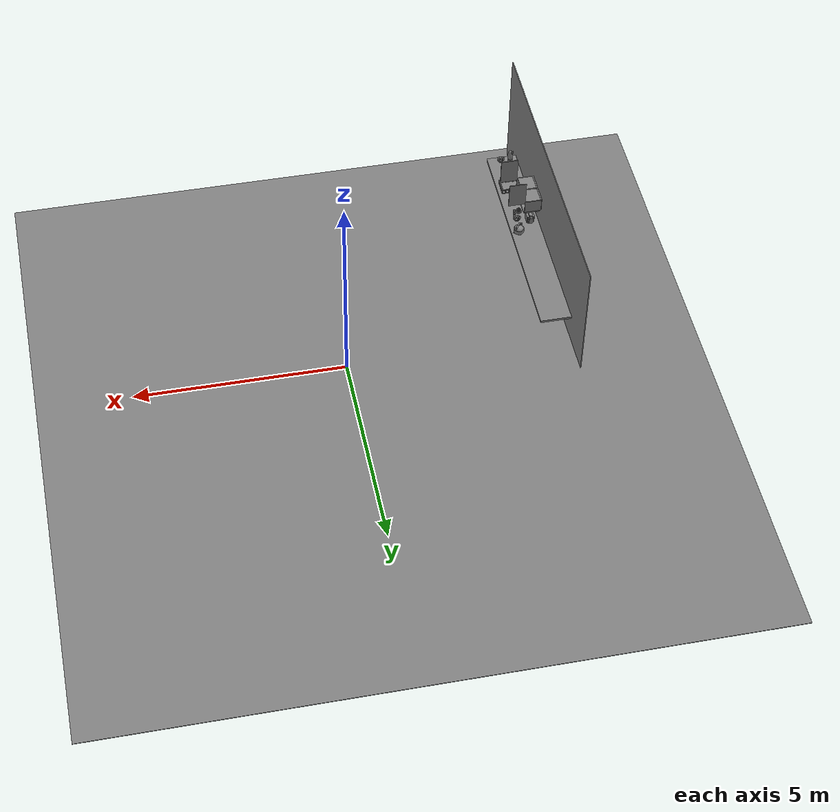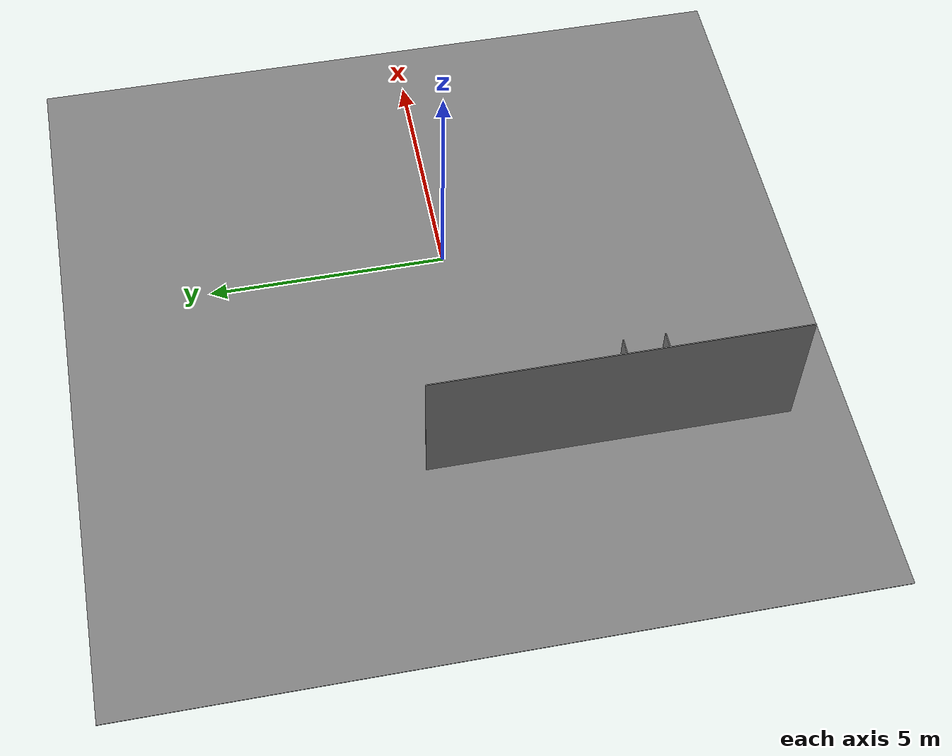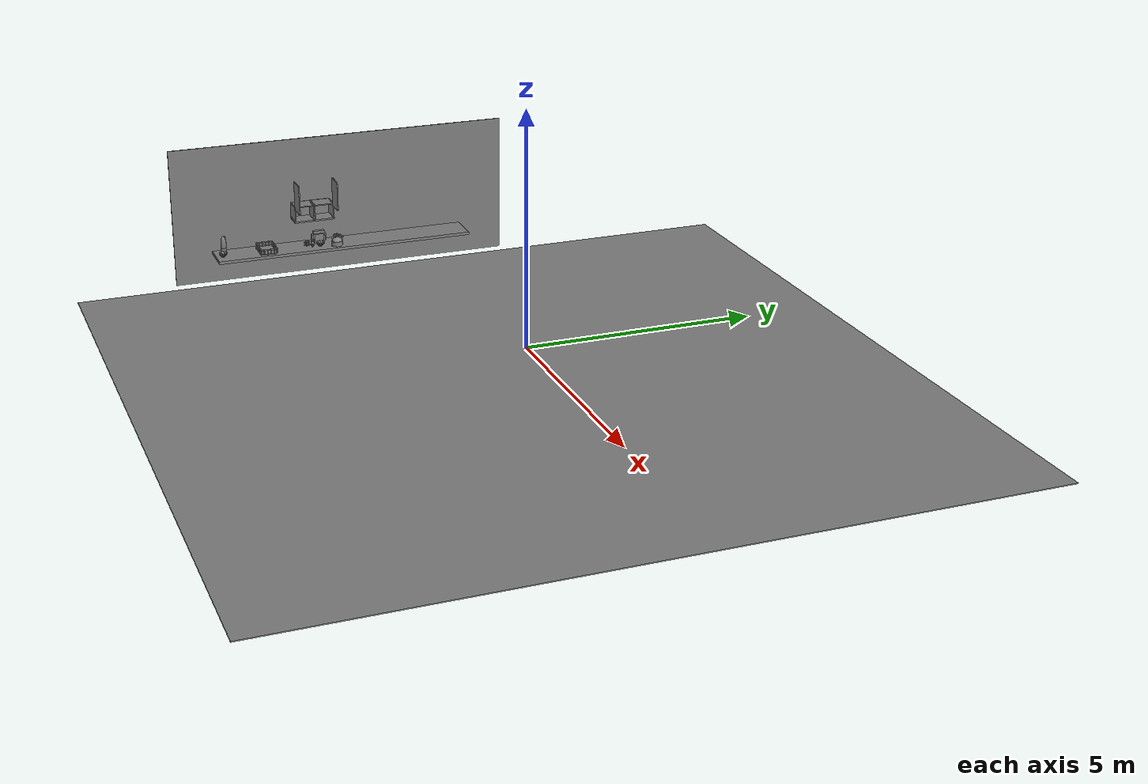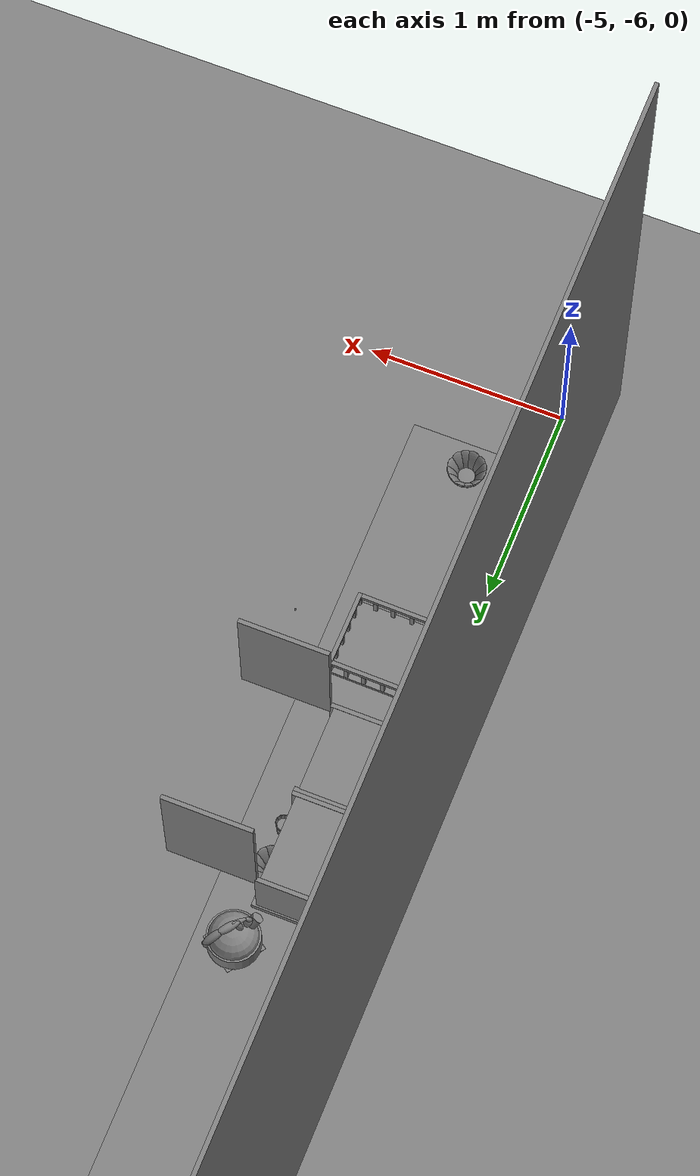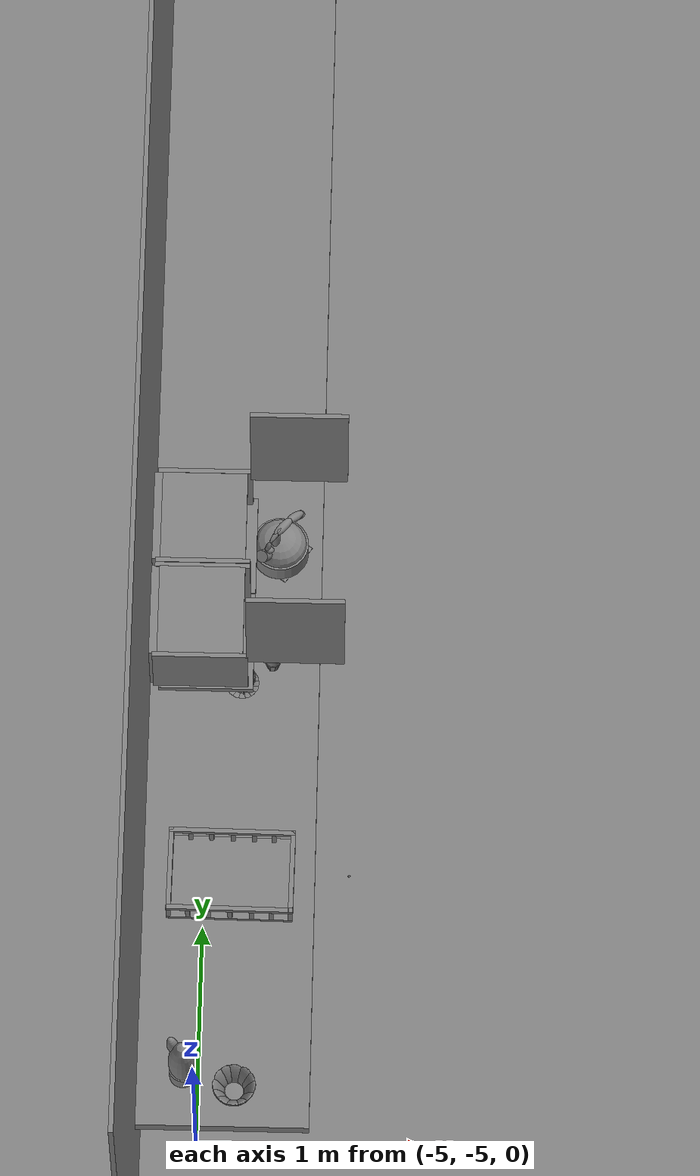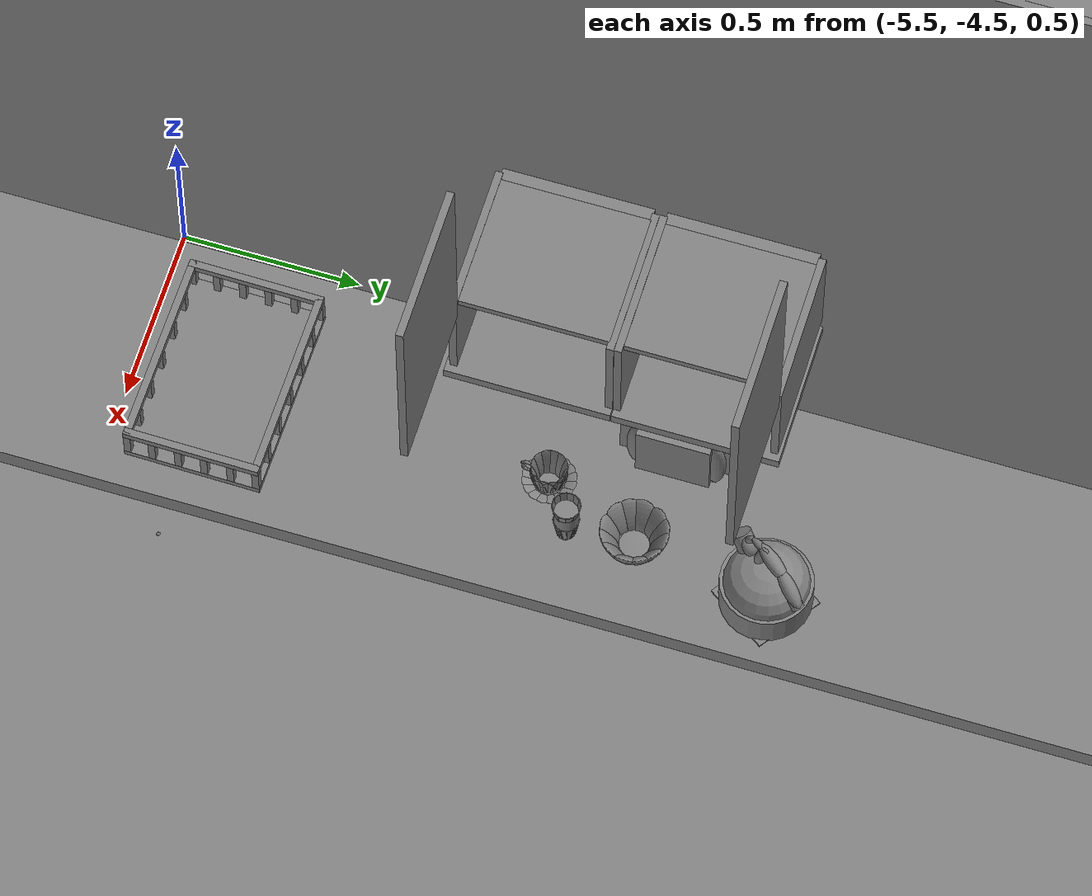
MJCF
<mujoco>
    <option gravity="0.000000000 0.000000000 -9.810000420" timestep="0.0049999999" integrator="implicitfast" density="9.8000002" viscosity="1.8000001e-05" noslip_iterations="10" iterations="100" sdf_iterations="50">
        <flag multiccd="disable"/>
    </option>
    <size memory="1000M"/>
    <compiler coordinate="local"/>
    <worldbody>
        <light cutoff="30" pos="0 1 1" dir="0 -1 -2"/>
        <light cutoff="30" pos="0 -1 1" dir="0 1 -2"/>
        <body pos="-4.860558510 -4.149443150 1.004824519" euler="0.000000000 0.000000000 -90.691101074" name="openloong_gripper_2f85_fix_base_usda_Basket_Kitchen_01">
            <geom contype="1" conaffinity="1" density="1000" type="box" material="" rgba="0.500000000 0.500000000 0.500000000 1.000000000" solimp="0.899999976 0.949999988 0.001000000" friction="1.000000000 0.005000000 0.000100000" solref="0.020000000 1.000000000" margin="0" condim="3" group="0" pos="-0.175679624 -0.000001907 0.109079957" quat="0.707106948 0.000000000 0.000000000 0.707106292" size="0.268999994 0.010000000 0.010500000" name="openloong_gripper_2f85_fix_base_usda_geom_1F5FFC72_E35E_47B7_923C_5D6F438E3B19"/>
            <geom contype="1" conaffinity="1" density="1000" type="box" material="" rgba="0.500000000 0.500000000 0.500000000 1.000000000" solimp="0.899999976 0.949999988 0.001000000" friction="1.000000000 0.005000000 0.000100000" solref="0.020000000 1.000000000" margin="0" condim="3" group="0" pos="-0.176020086 0.002991676 0.059861541" quat="0.707106948 0.000000000 0.000000000 0.707106292" size="0.009500000 0.009500000 0.039999999" name="openloong_gripper_2f85_fix_base_usda_geom_76CF47C6_0535_431C_9E6F_F99C45CAFB54"/>
            <geom contype="1" conaffinity="1" density="1000" type="box" material="" rgba="0.500000000 0.500000000 0.500000000 1.000000000" solimp="0.899999976 0.949999988 0.001000000" friction="1.000000000 0.005000000 0.000100000" solref="0.020000000 1.000000000" margin="0" condim="3" group="0" pos="0.176000476 0.002991199 0.059860587" quat="0.707106948 0.000000000 0.000000000 0.707106292" size="0.009500000 0.009500000 0.039999999" name="openloong_gripper_2f85_fix_base_usda_geom_1F86B977_B810_4FAE_B838_BBCE67ECBA51"/>
            <geom contype="1" conaffinity="1" density="1000" type="box" material="" rgba="0.500000000 0.500000000 0.500000000 1.000000000" solimp="0.899999976 0.949999988 0.001000000" friction="1.000000000 0.005000000 0.000100000" solref="0.020000000 1.000000000" margin="0" condim="3" group="0" pos="0.176003337 0.259475470 0.059859991" quat="0.707106948 0.000000000 0.000000000 0.707106292" size="0.009500000 0.009500000 0.039999999" name="openloong_gripper_2f85_fix_base_usda_geom_8FEF93D3_B03A_448E_9C81_3ADCEB675BE6"/>
            <geom contype="1" conaffinity="1" density="1000" type="box" material="" rgba="0.500000000 0.500000000 0.500000000 1.000000000" solimp="0.899999976 0.949999988 0.001000000" friction="1.000000000 0.005000000 0.000100000" solref="0.020000000 1.000000000" margin="0" condim="3" group="0" pos="-0.176020086 -0.088696003 0.059861422" quat="0.707106948 0.000000000 0.000000000 0.707106292" size="0.009500000 0.009500000 0.039999999" name="openloong_gripper_2f85_fix_base_usda_geom_B0B4B01D_65F1_4867_8CE5_0E81010DD526"/>
            <geom contype="1" conaffinity="1" density="1000" type="box" material="" rgba="0.500000000 0.500000000 0.500000000 1.000000000" solimp="0.899999976 0.949999988 0.001000000" friction="1.000000000 0.005000000 0.000100000" solref="0.020000000 1.000000000" margin="0" condim="3" group="0" pos="0.000000000 0.259647608 0.109079957" quat="0.707106948 0.000000000 0.000000000 0.707106292" size="0.010000000 0.185000002 0.010500000" name="openloong_gripper_2f85_fix_base_usda_geom_057755E6_99C7_4CE0_813B_4B6747AB3B0A"/>
            <geom contype="1" conaffinity="1" density="1000" type="box" material="" rgba="0.500000000 0.500000000 0.500000000 1.000000000" solimp="0.899999976 0.949999988 0.001000000" friction="1.000000000 0.005000000 0.000100000" solref="0.020000000 1.000000000" margin="0" condim="3" group="0" pos="0.176001906 -0.259545803 0.059860349" quat="0.707106948 0.000000000 0.000000000 0.707106292" size="0.009500000 0.009500000 0.039999999" name="openloong_gripper_2f85_fix_base_usda_geom_69B953FE_8149_49A5_8591_7E4612497FA9"/>
            <geom contype="1" conaffinity="1" density="1000" type="box" material="" rgba="0.500000000 0.500000000 0.500000000 1.000000000" solimp="0.899999976 0.949999988 0.001000000" friction="1.000000000 0.005000000 0.000100000" solref="0.020000000 1.000000000" margin="0" condim="3" group="0" pos="0.036305428 -0.259545326 0.059860587" quat="0.707106948 0.000000000 0.000000000 0.707106292" size="0.009500000 0.009500000 0.039999999" name="openloong_gripper_2f85_fix_base_usda_geom_9A41147C_B660_4BD1_8B68_74041B3F2EF9"/>
            <geom contype="1" conaffinity="1" density="1000" type="box" material="" rgba="0.500000000 0.500000000 0.500000000 1.000000000" solimp="0.899999976 0.949999988 0.001000000" friction="1.000000000 0.005000000 0.000100000" solref="0.020000000 1.000000000" margin="0" condim="3" group="0" pos="0.000000119 -0.259647369 0.109079957" quat="0.707106948 0.000000000 0.000000000 0.707106292" size="0.010000000 0.185000002 0.010500000" name="openloong_gripper_2f85_fix_base_usda_geom_B02A05BD_C8E1_485C_8BDE_8757F2054BD4"/>
            <geom contype="1" conaffinity="1" density="1000" type="box" material="" rgba="0.500000000 0.500000000 0.500000000 1.000000000" solimp="0.899999976 0.949999988 0.001000000" friction="1.000000000 0.005000000 0.000100000" solref="0.020000000 1.000000000" margin="0" condim="3" group="0" pos="-0.034950614 -0.259546280 0.059860826" quat="0.707106948 0.000000000 0.000000000 0.707106292" size="0.009500000 0.009500000 0.039999999" name="openloong_gripper_2f85_fix_base_usda_geom_11E55286_69AC_4AA3_B40A_AB45A64432F4"/>
            <geom contype="1" conaffinity="1" density="1000" type="box" material="" rgba="0.500000000 0.500000000 0.500000000 1.000000000" solimp="0.899999976 0.949999988 0.001000000" friction="1.000000000 0.005000000 0.000100000" solref="0.020000000 1.000000000" margin="0" condim="3" group="0" pos="0.108178139 0.259475708 0.059860229" quat="0.707106948 0.000000000 0.000000000 0.707106292" size="0.009500000 0.009500000 0.039999999" name="openloong_gripper_2f85_fix_base_usda_geom_C6EB0143_CEDC_444D_9E95_451C6993990B"/>
            <geom contype="1" conaffinity="1" density="1000" type="box" material="" rgba="0.500000000 0.500000000 0.500000000 1.000000000" solimp="0.899999976 0.949999988 0.001000000" friction="1.000000000 0.005000000 0.000100000" solref="0.020000000 1.000000000" margin="0" condim="3" group="0" pos="-0.106845737 0.259474993 0.059860826" quat="0.707106948 0.000000000 0.000000000 0.707106292" size="0.009500000 0.009500000 0.039999999" name="openloong_gripper_2f85_fix_base_usda_geom_1847C47E_FB18_49A0_8F47_D62D4E1A9DFC"/>
            <geom contype="1" conaffinity="1" density="1000" type="box" material="" rgba="0.500000000 0.500000000 0.500000000 1.000000000" solimp="0.899999976 0.949999988 0.001000000" friction="1.000000000 0.005000000 0.000100000" solref="0.020000000 1.000000000" margin="0" condim="3" group="0" pos="-0.176020563 0.179505825 0.059861779" quat="0.707106948 0.000000000 0.000000000 0.707106292" size="0.009500000 0.009500000 0.039999999" name="openloong_gripper_2f85_fix_base_usda_geom_FCDA1F11_0DAE_4176_A77D_86907A04CFC9"/>
            <geom contype="1" conaffinity="1" density="1000" type="box" material="" rgba="0.500000000 0.500000000 0.500000000 1.000000000" solimp="0.899999976 0.949999988 0.001000000" friction="1.000000000 0.005000000 0.000100000" solref="0.020000000 1.000000000" margin="0" condim="3" group="0" pos="-0.034949303 0.259475708 0.059860587" quat="0.707106948 0.000000000 0.000000000 0.707106292" size="0.009500000 0.009500000 0.039999999" name="openloong_gripper_2f85_fix_base_usda_geom_7A2807C9_73F3_4BF0_BF6C_8DEAAE7DEB9B"/>
            <geom contype="1" conaffinity="1" density="1000" type="box" material="" rgba="0.500000000 0.500000000 0.500000000 1.000000000" solimp="0.899999976 0.949999988 0.001000000" friction="1.000000000 0.005000000 0.000100000" solref="0.020000000 1.000000000" margin="0" condim="3" group="0" pos="0.175792098 -0.000002384 0.109079838" quat="0.707106948 0.000000000 0.000000000 0.707106292" size="0.268999994 0.010000000 0.010500000" name="openloong_gripper_2f85_fix_base_usda_geom_E2B41076_2E9A_4122_9601_5EAB8199B920"/>
            <geom contype="1" conaffinity="1" density="1000" type="box" material="" rgba="0.500000000 0.500000000 0.500000000 1.000000000" solimp="0.899999976 0.949999988 0.001000000" friction="1.000000000 0.005000000 0.000100000" solref="0.020000000 1.000000000" margin="0" condim="3" group="0" pos="-0.000015259 0.000000000 0.010667920" quat="0.707106948 0.000000000 0.000000000 0.707106292" size="0.268999994 0.186000004 0.010500000" name="openloong_gripper_2f85_fix_base_usda_geom_D9E33DBE_F513_4436_A40E_4642AC7EA442"/>
            <geom contype="1" conaffinity="1" density="1000" type="box" material="" rgba="0.500000000 0.500000000 0.500000000 1.000000000" solimp="0.899999976 0.949999988 0.001000000" friction="1.000000000 0.005000000 0.000100000" solref="0.020000000 1.000000000" margin="0" condim="3" group="0" pos="-0.176020026 0.094224930 0.059861660" quat="0.707106948 0.000000000 0.000000000 0.707106292" size="0.009500000 0.009500000 0.039999999" name="openloong_gripper_2f85_fix_base_usda_geom_E521F452_41D2_4DDD_9B78_1ADD7333CED4"/>
            <geom contype="1" conaffinity="1" density="1000" type="box" material="" rgba="0.500000000 0.500000000 0.500000000 1.000000000" solimp="0.899999976 0.949999988 0.001000000" friction="1.000000000 0.005000000 0.000100000" solref="0.020000000 1.000000000" margin="0" condim="3" group="0" pos="0.108177185 -0.259545326 0.059860349" quat="0.707106948 0.000000000 0.000000000 0.707106292" size="0.009500000 0.009500000 0.039999999" name="openloong_gripper_2f85_fix_base_usda_geom_C03AFE61_021B_4457_8203_6C0A7E3C1CAF"/>
            <geom contype="1" conaffinity="1" density="1000" type="box" material="" rgba="0.500000000 0.500000000 0.500000000 1.000000000" solimp="0.899999976 0.949999988 0.001000000" friction="1.000000000 0.005000000 0.000100000" solref="0.020000000 1.000000000" margin="0" condim="3" group="0" pos="-0.176020026 -0.177031994 0.059861183" quat="0.707106948 0.000000000 0.000000000 0.707106292" size="0.009500000 0.009500000 0.039999999" name="openloong_gripper_2f85_fix_base_usda_geom_7800EE32_AB9F_4633_B2C0_8C984D5E2700"/>
            <geom contype="1" conaffinity="1" density="1000" type="box" material="" rgba="0.500000000 0.500000000 0.500000000 1.000000000" solimp="0.899999976 0.949999988 0.001000000" friction="1.000000000 0.005000000 0.000100000" solref="0.020000000 1.000000000" margin="0" condim="3" group="0" pos="-0.176020086 -0.259545803 0.059861183" quat="0.707106948 0.000000000 0.000000000 0.707106292" size="0.009500000 0.009500000 0.039999999" name="openloong_gripper_2f85_fix_base_usda_geom_D419CE9B_17E7_4B4A_905D_45238CA73706"/>
            <geom contype="1" conaffinity="1" density="1000" type="box" material="" rgba="0.500000000 0.500000000 0.500000000 1.000000000" solimp="0.899999976 0.949999988 0.001000000" friction="1.000000000 0.005000000 0.000100000" solref="0.020000000 1.000000000" margin="0" condim="3" group="0" pos="-0.106846333 -0.259545803 0.059861064" quat="0.707106948 0.000000000 0.000000000 0.707106292" size="0.009500000 0.009500000 0.039999999" name="openloong_gripper_2f85_fix_base_usda_geom_1E51AD12_28BF_4E7A_B7AA_1852B7C30B4A"/>
            <geom contype="1" conaffinity="1" density="1000" type="box" material="" rgba="0.500000000 0.500000000 0.500000000 1.000000000" solimp="0.899999976 0.949999988 0.001000000" friction="1.000000000 0.005000000 0.000100000" solref="0.020000000 1.000000000" margin="0" condim="3" group="0" pos="0.176000595 0.094224453 0.059860826" quat="0.707106948 0.000000000 0.000000000 0.707106292" size="0.009500000 0.009500000 0.039999999" name="openloong_gripper_2f85_fix_base_usda_geom_F9645D4B_C508_4D13_89B2_D9F4FD60ECDD"/>
            <geom contype="1" conaffinity="1" density="1000" type="box" material="" rgba="0.500000000 0.500000000 0.500000000 1.000000000" solimp="0.899999976 0.949999988 0.001000000" friction="1.000000000 0.005000000 0.000100000" solref="0.020000000 1.000000000" margin="0" condim="3" group="0" pos="0.176001072 -0.088696480 0.059860587" quat="0.707106948 0.000000000 0.000000000 0.707106292" size="0.009500000 0.009500000 0.039999999" name="openloong_gripper_2f85_fix_base_usda_geom_D7C525ED_6336_49BA_9632_14F237101478"/>
            <geom contype="1" conaffinity="1" density="1000" type="box" material="" rgba="0.500000000 0.500000000 0.500000000 1.000000000" solimp="0.899999976 0.949999988 0.001000000" friction="1.000000000 0.005000000 0.000100000" solref="0.020000000 1.000000000" margin="0" condim="3" group="0" pos="0.036306858 0.259475946 0.059860349" quat="0.707106948 0.000000000 0.000000000 0.707106292" size="0.009500000 0.009500000 0.039999999" name="openloong_gripper_2f85_fix_base_usda_geom_7EA24E19_F347_4CEF_8443_7EA1E40EC06D"/>
            <geom contype="1" conaffinity="1" density="1000" type="box" material="" rgba="0.500000000 0.500000000 0.500000000 1.000000000" solimp="0.899999976 0.949999988 0.001000000" friction="1.000000000 0.005000000 0.000100000" solref="0.020000000 1.000000000" margin="0" condim="3" group="0" pos="0.176001430 -0.177032471 0.059860349" quat="0.707106948 0.000000000 0.000000000 0.707106292" size="0.009500000 0.009500000 0.039999999" name="openloong_gripper_2f85_fix_base_usda_geom_88ED7E53_3B99_47C8_A323_E5E7FA5D4750"/>
            <geom contype="1" conaffinity="1" density="1000" type="box" material="" rgba="0.500000000 0.500000000 0.500000000 1.000000000" solimp="0.899999976 0.949999988 0.001000000" friction="1.000000000 0.005000000 0.000100000" solref="0.020000000 1.000000000" margin="0" condim="3" group="0" pos="0.175999999 0.179504871 0.059860945" quat="0.707106948 0.000000000 0.000000000 0.707106292" size="0.009500000 0.009500000 0.039999999" name="openloong_gripper_2f85_fix_base_usda_geom_94D0F8C3_0AE9_413B_9CEF_FEA3612E6A4D"/>
            <geom contype="1" conaffinity="1" density="1000" type="box" material="" rgba="0.500000000 0.500000000 0.500000000 1.000000000" solimp="0.899999976 0.949999988 0.001000000" friction="1.000000000 0.005000000 0.000100000" solref="0.020000000 1.000000000" margin="0" condim="3" group="0" pos="-0.176020026 0.259474516 0.059860945" quat="0.707106948 0.000000000 0.000000000 0.707106292" size="0.009500000 0.009500000 0.039999999" name="openloong_gripper_2f85_fix_base_usda_geom_B98A2B24_E39E_4717_9F6A_0BAB2F8F3D25"/>
            <freejoint name="openloong_gripper_2f85_fix_base_usda_Basket_Kitchen_01_joint"/>
        </body>
        <body pos="-5.020127296 -2.953741550 1.135127425" euler="89.999946594 0.000000000 0.000000000" name="Interactive Objcets_Bread">
            <geom contype="1" conaffinity="1" density="1000" type="box" material="" rgba="0.500000000 0.500000000 0.500000000 1.000000000" solimp="0.899999976 0.949999988 0.001000000" friction="1.000000000 0.005000000 0.000100000" solref="0.020000000 1.000000000" margin="0" condim="3" group="0" pos="0.033925056 -0.123201847 0.086778767" quat="0.707107067 -0.707106471 0.000000021 -0.000000021" size="0.020000000 0.020000000 0.005000000" name="Interactive Objcets_geom_BB6C2E81_CCC4_4373_88DB_5256B1DA13F4"/>
            <geom contype="1" conaffinity="1" density="1000" type="ellipsoid" material="" rgba="0.500000000 0.500000000 0.500000000 1.000000000" solimp="0.899999976 0.949999988 0.001000000" friction="1.000000000 0.005000000 0.000100000" solref="0.020000000 1.000000000" margin="0" condim="3" group="0" pos="0.052222252 -0.026057363 0.101459242" quat="0.707107067 -0.707106471 0.000000021 -0.000000021" size="0.020000000 0.029999999 0.094999999" name="Interactive Objcets_geom_1685C7A4_46CD_479C_BD5D_8FDE5907EA25"/>
            <geom contype="1" conaffinity="1" density="1000" type="ellipsoid" material="" rgba="0.500000000 0.500000000 0.500000000 1.000000000" solimp="0.899999976 0.949999988 0.001000000" friction="1.000000000 0.005000000 0.000100000" solref="0.020000000 1.000000000" margin="0" condim="3" group="0" pos="0.052222252 -0.026057243 -0.106481344" quat="0.707107067 -0.707106471 0.000000021 -0.000000021" size="0.020000000 0.029999999 0.094999999" name="Interactive Objcets_geom_AD1E2CBF_3E63_46AB_9721_5725F72E0461"/>
            <geom contype="1" conaffinity="1" density="1000" type="box" material="" rgba="0.500000000 0.500000000 0.500000000 1.000000000" solimp="0.899999976 0.949999988 0.001000000" friction="1.000000000 0.005000000 0.000100000" solref="0.020000000 1.000000000" margin="0" condim="3" group="0" pos="-0.008702755 -0.016588926 0.000174277" quat="0.707107067 -0.707106471 0.000000021 -0.000000021" size="0.090000004 0.100000001 0.094999999" name="Interactive Objcets_geom_B82F5257_08EF_4821_80F5_D978EAA2DB5A"/>
            <geom contype="1" conaffinity="1" density="1000" type="box" material="" rgba="0.500000000 0.500000000 0.500000000 1.000000000" solimp="0.899999976 0.949999988 0.001000000" friction="1.000000000 0.005000000 0.000100000" solref="0.020000000 1.000000000" margin="0" condim="3" group="0" pos="-0.050020695 -0.123201847 0.086778767" quat="0.707107067 -0.707106471 0.000000021 -0.000000021" size="0.020000000 0.020000000 0.005000000" name="Interactive Objcets_geom_FCDF9790_947E_422E_9DD0_9B23D9C906A2"/>
            <geom contype="1" conaffinity="1" density="1000" type="box" material="" rgba="0.500000000 0.500000000 0.500000000 1.000000000" solimp="0.899999976 0.949999988 0.001000000" friction="1.000000000 0.005000000 0.000100000" solref="0.020000000 1.000000000" margin="0" condim="3" group="0" pos="0.033925056 -0.123201728 -0.092369899" quat="0.707107067 -0.707106471 0.000000021 -0.000000021" size="0.020000000 0.020000000 0.005000000" name="Interactive Objcets_geom_D9B32257_E420_4B9F_AA30_E70F68BADEB8"/>
            <geom contype="1" conaffinity="1" density="1000" type="box" material="" rgba="0.500000000 0.500000000 0.500000000 1.000000000" solimp="0.899999976 0.949999988 0.001000000" friction="1.000000000 0.005000000 0.000100000" solref="0.020000000 1.000000000" margin="0" condim="3" group="0" pos="-0.008702755 0.104617000 -0.003706597" quat="0.707107067 -0.707106471 0.000000021 -0.000000021" size="0.039999999 0.119999997 0.030999999" name="Interactive Objcets_geom_00699A19_FD80_481D_87FD_F6490CC88D82"/>
            <geom contype="1" conaffinity="1" density="1000" type="box" material="" rgba="0.500000000 0.500000000 0.500000000 1.000000000" solimp="0.899999976 0.949999988 0.001000000" friction="1.000000000 0.005000000 0.000100000" solref="0.020000000 1.000000000" margin="0" condim="3" group="0" pos="-0.008702755 -0.017670155 0.134585604" quat="0.707107067 -0.707106471 0.000000021 -0.000000021" size="0.045000002 0.020000000 0.079999998" name="Interactive Objcets_geom_223B650E_AD04_4BFE_8B3A_25D1F34F1342"/>
            <geom contype="1" conaffinity="1" density="1000" type="box" material="" rgba="0.500000000 0.500000000 0.500000000 1.000000000" solimp="0.899999976 0.949999988 0.001000000" friction="1.000000000 0.005000000 0.000100000" solref="0.020000000 1.000000000" margin="0" condim="3" group="0" pos="-0.008702755 -0.017670274 -0.135069147" quat="0.707107067 -0.707106471 0.000000021 -0.000000021" size="0.045000002 0.020000000 0.079999998" name="Interactive Objcets_geom_777D2B82_7D30_4FA4_9218_B7D003232CB5"/>
            <geom contype="1" conaffinity="1" density="1000" type="ellipsoid" material="" rgba="0.500000000 0.500000000 0.500000000 1.000000000" solimp="0.899999976 0.949999988 0.001000000" friction="1.000000000 0.005000000 0.000100000" solref="0.020000000 1.000000000" margin="0" condim="3" group="0" pos="-0.069190502 -0.026057363 0.101458766" quat="0.707107067 -0.707106471 0.000000021 -0.000000021" size="0.020000000 0.029999999 0.094999999" name="Interactive Objcets_geom_4DD63435_E4F0_40AF_B89A_E00CC239A077"/>
            <geom contype="1" conaffinity="1" density="1000" type="box" material="" rgba="0.500000000 0.500000000 0.500000000 1.000000000" solimp="0.899999976 0.949999988 0.001000000" friction="1.000000000 0.005000000 0.000100000" solref="0.020000000 1.000000000" margin="0" condim="3" group="0" pos="-0.050020695 -0.123201728 -0.092370376" quat="0.707107067 -0.707106471 0.000000021 -0.000000021" size="0.020000000 0.020000000 0.005000000" name="Interactive Objcets_geom_A7996F27_2168_4456_9D48_D44284402AD1"/>
            <geom contype="1" conaffinity="1" density="1000" type="ellipsoid" material="" rgba="0.500000000 0.500000000 0.500000000 1.000000000" solimp="0.899999976 0.949999988 0.001000000" friction="1.000000000 0.005000000 0.000100000" solref="0.020000000 1.000000000" margin="0" condim="3" group="0" pos="-0.067312241 -0.026057482 -0.101716787" quat="0.707107067 -0.707106471 0.000000021 -0.000000021" size="0.020000000 0.029999999 0.094999999" name="Interactive Objcets_geom_A7771BA4_60FD_4126_9D69_D13E3D95E3C4"/>
            <freejoint name="Interactive Objcets_Bread"/>
        </body>
        <body pos="-4.805274963 -2.665403366 1.876015186" euler="89.999877930 89.999969482 0.000000000" name="Interactive Objcets_guimen_02">
            <geom contype="1" conaffinity="1" density="1000" type="box" material="" rgba="0.500000000 0.500000000 0.500000000 1.000000000" solimp="0.899999976 0.949999988 0.001000000" friction="1.000000000 0.005000000 0.000100000" solref="0.020000000 1.000000000" margin="0" condim="3" group="0" pos="0.006727815 0.314709663 0.203009367" quat="0.999999940 0.000000000 0.000000000 0.000000000" size="0.010000000 0.317999989 0.204999998" name="Interactive Objcets_geom_1EC2B51A_66B1_4820_B9B5_F6BD1A003E70"/>
            <joint armature="0" stiffness="0" damping="1" axis="0.000000 1.000000 0.000000" type="hinge" name="Interactive Objcets_guimen_02"/>
        </body>
        <body pos="-4.835184574 -3.254794121 1.033557892" euler="0.000000000 0.000000000 0.000000000" name="Interactive Objcets_cupplate_01">
            <geom contype="1" conaffinity="1" density="1000" type="ellipsoid" material="" rgba="0.500000000 0.500000000 0.500000000 1.000000000" solimp="0.899999976 0.949999988 0.001000000" friction="1.000000000 0.005000000 0.000100000" solref="0.020000000 1.000000000" margin="0" condim="3" group="0" pos="0.022432804 0.052464008 0.000154614" quat="0.455865860 -0.467545629 -0.308059722 -0.691871881" size="0.002000000 0.020000000 0.017000001" name="Interactive Objcets_geom_CF18EBD1_42E4_4F43_94CA_0EE6DCF471FA"/>
            <geom contype="1" conaffinity="1" density="1000" type="ellipsoid" material="" rgba="0.500000000 0.500000000 0.500000000 1.000000000" solimp="0.899999976 0.949999988 0.001000000" friction="1.000000000 0.005000000 0.000100000" solref="0.020000000 1.000000000" margin="0" condim="3" group="0" pos="-0.041719437 -0.039082766 0.000000000" quat="0.304989874 0.520597219 0.206102297 -0.770377457" size="0.002000000 0.020000000 0.017000001" name="Interactive Objcets_geom_42D4E0CD_3D73_40D4_95D5_B435764A5509"/>
            <geom contype="1" conaffinity="1" density="1000" type="ellipsoid" material="" rgba="0.500000000 0.500000000 0.500000000 1.000000000" solimp="0.899999976 0.949999988 0.001000000" friction="1.000000000 0.005000000 0.000100000" solref="0.020000000 1.000000000" margin="0" condim="3" group="0" pos="0.000000000 0.000000000 -0.007192612" quat="1.000000000 0.000000000 0.000000000 0.000000000" size="0.039999999 0.039999999 0.001000000" name="Interactive Objcets_geom_414A3627_FDD6_4713_9550_6428895FE3B0"/>
            <geom contype="1" conaffinity="1" density="1000" type="ellipsoid" material="" rgba="0.500000000 0.500000000 0.500000000 1.000000000" solimp="0.899999976 0.949999988 0.001000000" friction="1.000000000 0.005000000 0.000100000" solref="0.020000000 1.000000000" margin="0" condim="3" group="0" pos="-0.057191849 0.000000477 0.000154614" quat="0.828553081 0.000000000 -0.559910476 0.000000000" size="0.002000000 0.020000000 0.017000001" name="Interactive Objcets_geom_8812350E_86FD_4AB0_9710_46B3A963CC97"/>
            <geom contype="1" conaffinity="1" density="1000" type="ellipsoid" material="" rgba="0.500000000 0.500000000 0.500000000 1.000000000" solimp="0.899999976 0.949999988 0.001000000" friction="1.000000000 0.005000000 0.000100000" solref="0.020000000 1.000000000" margin="0" condim="3" group="0" pos="-0.052522659 0.022613287 0.000154614" quat="0.811438143 -0.113215551 -0.548344791 -0.167535841" size="0.002000000 0.020000000 0.017000001" name="Interactive Objcets_geom_6D168520_62AC_4CAC_A538_3548974AB51D"/>
            <geom contype="1" conaffinity="1" density="1000" type="ellipsoid" material="" rgba="0.500000000 0.500000000 0.500000000 1.000000000" solimp="0.899999976 0.949999988 0.001000000" friction="1.000000000 0.005000000 0.000100000" solref="0.020000000 1.000000000" margin="0" condim="3" group="0" pos="0.057000160 0.000000477 0.000000000" quat="0.828553081 0.000000000 0.559910476 0.000000000" size="0.002000000 0.020000000 0.017000001" name="Interactive Objcets_geom_5FA1D910_4525_452F_96E0_7F1770D474EE"/>
            <geom contype="1" conaffinity="1" density="1000" type="ellipsoid" material="" rgba="0.500000000 0.500000000 0.500000000 1.000000000" solimp="0.899999976 0.949999988 0.001000000" friction="1.000000000 0.005000000 0.000100000" solref="0.020000000 1.000000000" margin="0" condim="3" group="0" pos="-0.000003815 -0.057095528 0.000000000" quat="0.586347640 0.395597160 0.396235406 -0.585402966" size="0.002000000 0.020000000 0.017000001" name="Interactive Objcets_geom_C5C92171_5517_4E82_B89E_121C7317FB76"/>
            <geom contype="1" conaffinity="1" density="1000" type="ellipsoid" material="" rgba="0.500000000 0.500000000 0.500000000 1.000000000" solimp="0.899999976 0.949999988 0.001000000" friction="1.000000000 0.005000000 0.000100000" solref="0.020000000 1.000000000" margin="0" condim="3" group="0" pos="0.052457333 0.022318602 0.000154614" quat="0.165263638 -0.548659503 -0.111679509 -0.811904132" size="0.002000000 0.020000000 0.017000001" name="Interactive Objcets_geom_3A3819F9_0A74_4C5A_9F82_D6AB5DD41036"/>
            <geom contype="1" conaffinity="1" density="1000" type="ellipsoid" material="" rgba="0.500000000 0.500000000 0.500000000 1.000000000" solimp="0.899999976 0.949999988 0.001000000" friction="1.000000000 0.005000000 0.000100000" solref="0.020000000 1.000000000" margin="0" condim="3" group="0" pos="-0.000187874 0.057096481 0.000154614" quat="0.586347640 -0.395597160 -0.396235406 -0.585402966" size="0.002000000 0.020000000 0.017000001" name="Interactive Objcets_geom_31A7EE52_A7B9_4B23_B462_33D9FA1153D4"/>
            <geom contype="1" conaffinity="1" density="1000" type="ellipsoid" material="" rgba="0.500000000 0.500000000 0.500000000 1.000000000" solimp="0.899999976 0.949999988 0.001000000" friction="1.000000000 0.005000000 0.000100000" solref="0.020000000 1.000000000" margin="0" condim="3" group="0" pos="0.041527748 0.039082766 0.000154614" quat="0.304989874 -0.520597219 -0.206102297 -0.770377457" size="0.002000000 0.020000000 0.017000001" name="Interactive Objcets_geom_02588D8F_1EB0_4317_9188_9E5C95850DCA"/>
            <geom contype="1" conaffinity="1" density="1000" type="ellipsoid" material="" rgba="0.500000000 0.500000000 0.500000000 1.000000000" solimp="0.899999976 0.949999988 0.001000000" friction="1.000000000 0.005000000 0.000100000" solref="0.020000000 1.000000000" margin="0" condim="3" group="0" pos="0.022139072 -0.052588940 0.000000119" quat="0.690592766 0.309367865 0.466681093 -0.457801163" size="0.002000000 0.020000000 0.017000001" name="Interactive Objcets_geom_B79881F5_38D3_4D75_86D6_8F1EB77D1BDE"/>
            <geom contype="1" conaffinity="1" density="1000" type="ellipsoid" material="" rgba="0.500000000 0.500000000 0.500000000 1.000000000" solimp="0.899999976 0.949999988 0.001000000" friction="1.000000000 0.005000000 0.000100000" solref="0.020000000 1.000000000" margin="0" condim="3" group="0" pos="-0.022329807 0.052588463 0.000154614" quat="0.690592766 -0.309367865 -0.466681093 -0.457801163" size="0.002000000 0.020000000 0.017000001" name="Interactive Objcets_geom_561EAD69_EE67_413D_A912_2B78FF4305BF"/>
            <geom contype="1" conaffinity="1" density="1000" type="ellipsoid" material="" rgba="0.500000000 0.500000000 0.500000000 1.000000000" solimp="0.899999976 0.949999988 0.001000000" friction="1.000000000 0.005000000 0.000100000" solref="0.020000000 1.000000000" margin="0" condim="3" group="0" pos="-0.022624493 -0.052463770 0.000000000" quat="0.455865860 0.467545629 0.308059722 -0.691871881" size="0.002000000 0.020000000 0.017000001" name="Interactive Objcets_geom_EFA039A8_E054_4A1F_BC95_CDC5ACD7C9C8"/>
            <geom contype="1" conaffinity="1" density="1000" type="ellipsoid" material="" rgba="0.500000000 0.500000000 0.500000000 1.000000000" solimp="0.899999976 0.949999988 0.001000000" friction="1.000000000 0.005000000 0.000100000" solref="0.020000000 1.000000000" margin="0" condim="3" group="0" pos="0.038919926 -0.041685820 0.000000000" quat="0.760133922 0.222795680 0.513674736 -0.329691947" size="0.002000000 0.020000000 0.017000001" name="Interactive Objcets_geom_5E35DDFA_FD5D_4D90_A0FF_A7F7A44EAC91"/>
            <geom contype="1" conaffinity="1" density="1000" type="ellipsoid" material="" rgba="0.500000000 0.500000000 0.500000000 1.000000000" solimp="0.899999976 0.949999988 0.001000000" friction="1.000000000 0.005000000 0.000100000" solref="0.020000000 1.000000000" margin="0" condim="3" group="0" pos="0.052331448 -0.022612572 0.000000000" quat="0.811438143 0.113215551 0.548344791 -0.167535841" size="0.002000000 0.020000000 0.017000001" name="Interactive Objcets_geom_89E20683_176C_4C0A_8E0F_BEE816A2BD5F"/>
            <geom contype="1" conaffinity="1" density="1000" type="ellipsoid" material="" rgba="0.500000000 0.500000000 0.500000000 1.000000000" solimp="0.899999976 0.949999988 0.001000000" friction="1.000000000 0.005000000 0.000100000" solref="0.020000000 1.000000000" margin="0" condim="3" group="0" pos="-0.052649021 -0.022319317 0.000000119" quat="0.165263638 0.548659503 0.111679509 -0.811904132" size="0.002000000 0.020000000 0.017000001" name="Interactive Objcets_geom_60964EB2_7693_42B2_9265_B1F0B50C0C9C"/>
            <geom contype="1" conaffinity="1" density="1000" type="ellipsoid" material="" rgba="0.500000000 0.500000000 0.500000000 1.000000000" solimp="0.899999976 0.949999988 0.001000000" friction="1.000000000 0.005000000 0.000100000" solref="0.020000000 1.000000000" margin="0" condim="3" group="0" pos="0.000000000 0.000000000 -0.006308794" quat="1.000000000 0.000000000 0.000000000 0.000000000" size="0.035000000 0.035000000 0.001000000" name="Interactive Objcets_geom_06903FE8_4046_4C3D_98F9_9DEBA8ECACAC"/>
            <geom contype="1" conaffinity="1" density="1000" type="ellipsoid" material="" rgba="0.500000000 0.500000000 0.500000000 1.000000000" solimp="0.899999976 0.949999988 0.001000000" friction="1.000000000 0.005000000 0.000100000" solref="0.020000000 1.000000000" margin="0" condim="3" group="0" pos="-0.039110661 0.041686535 0.000154614" quat="0.760133922 -0.222795680 -0.513674736 -0.329691947" size="0.002000000 0.020000000 0.017000001" name="Interactive Objcets_geom_F1D16DB8_B85C_4F0C_832A_7B9F780F0E93"/>
            <freejoint name="Interactive Objcets_cupplate_01"/>
        </body>
        <body pos="-4.802892208 -3.488179445 1.876015186" euler="89.999992371 -89.999946594 0.000000000" name="Interactive Objcets_guimen_01">
            <geom contype="1" conaffinity="1" density="1000" type="box" material="" rgba="0.500000000 0.500000000 0.500000000 1.000000000" solimp="0.899999976 0.949999988 0.001000000" friction="1.000000000 0.005000000 0.000100000" solref="0.020000000 1.000000000" margin="0" condim="3" group="0" pos="0.006727934 0.314709902 -0.203009605" quat="1.000000000 0.000000119 -0.000000119 0.000000000" size="0.010000000 0.317999989 0.204999998" name="Interactive Objcets_geom_72314F5D_708A_43E8_92FE_7C983F6C0CEA"/>
            <joint armature="0" stiffness="0" damping="1" axis="0.000000 1.000000 0.000000" type="hinge" name="Interactive Objcets_guimen_01"/>
        </body>
        <body pos="-4.721817970 -2.990536690 1.027358174" euler="0.000000000 0.000000000 89.999946594" name="Interactive Objcets_bow_02">
            <geom contype="1" conaffinity="1" density="1000" type="ellipsoid" material="" rgba="0.500000000 0.500000000 0.500000000 1.000000000" solimp="0.899999976 0.949999988 0.001000000" friction="1.000000000 0.005000000 0.000100000" solref="0.020000000 1.000000000" margin="0" condim="3" group="0" pos="-0.029293532 0.059069633 0.044118762" quat="0.825555801 -0.125530809 -0.202596903 -0.511521280" size="0.010000000 0.039999999 0.052000001" name="Interactive Objcets_geom_ED6AF31E_60C9_4651_94C4_05FC49E7AA1D"/>
            <geom contype="1" conaffinity="1" density="1000" type="ellipsoid" material="" rgba="0.500000000 0.500000000 0.500000000 1.000000000" solimp="0.899999976 0.949999988 0.001000000" friction="1.000000000 0.005000000 0.000100000" solref="0.020000000 1.000000000" margin="0" condim="3" group="0" pos="0.029448029 -0.059084892 0.044118762" quat="0.825555801 0.125530601 0.202597082 -0.511521280" size="0.010000000 0.039999999 0.052000001" name="Interactive Objcets_geom_A72B4439_E2BB_4F51_86DD_B8DF953A07EE"/>
            <geom contype="1" conaffinity="1" density="1000" type="ellipsoid" material="" rgba="0.500000000 0.500000000 0.500000000 1.000000000" solimp="0.899999976 0.949999988 0.001000000" friction="1.000000000 0.005000000 0.000100000" solref="0.020000000 1.000000000" margin="0" condim="3" group="0" pos="0.052321676 -0.040297508 0.044118762" quat="0.919264674 0.076882742 0.225593731 -0.313287675" size="0.010000000 0.039999999 0.052000001" name="Interactive Objcets_geom_F243CEA4_C3C1_45D0_857C_6635670BDD0A"/>
            <geom contype="1" conaffinity="1" density="1000" type="ellipsoid" material="" rgba="0.500000000 0.500000000 0.500000000 1.000000000" solimp="0.899999976 0.949999988 0.001000000" friction="1.000000000 0.005000000 0.000100000" solref="0.020000000 1.000000000" margin="0" condim="3" group="0" pos="0.040234569 0.052338600 0.044118762" quat="0.429593176 -0.213750035 -0.105424814 -0.871002913" size="0.010000000 0.039999999 0.052000001" name="Interactive Objcets_geom_52892F77_7BAB_4A8B_9B99_8E01A9DA95F2"/>
            <geom contype="1" conaffinity="1" density="1000" type="ellipsoid" material="" rgba="0.500000000 0.500000000 0.500000000 1.000000000" solimp="0.899999976 0.949999988 0.001000000" friction="1.000000000 0.005000000 0.000100000" solref="0.020000000 1.000000000" margin="0" condim="3" group="0" pos="0.000082973 0.000000000 0.000446677" quat="1.000000000 0.000000000 0.000000000 0.000000000" size="0.039999999 0.039999999 0.002000000" name="Interactive Objcets_geom_69A90F25_2F93_480E_B06F_5390A0759B16"/>
            <geom contype="1" conaffinity="1" density="1000" type="ellipsoid" material="" rgba="0.500000000 0.500000000 0.500000000 1.000000000" solimp="0.899999976 0.949999988 0.001000000" friction="1.000000000 0.005000000 0.000100000" solref="0.020000000 1.000000000" margin="0" condim="3" group="0" pos="-0.040080305 -0.052354336 0.044118762" quat="0.429593205 0.213749886 0.105425082 -0.871003032" size="0.010000000 0.039999999 0.052000001" name="Interactive Objcets_geom_DA5C25BF_B320_4A9E_BE42_1019207EBBA5"/>
            <geom contype="1" conaffinity="1" density="1000" type="ellipsoid" material="" rgba="0.500000000 0.500000000 0.500000000 1.000000000" solimp="0.899999976 0.949999988 0.001000000" friction="1.000000000 0.005000000 0.000100000" solref="0.020000000 1.000000000" margin="0" condim="3" group="0" pos="-0.065898418 -0.000007629 0.044118762" quat="0.971183062 -0.000000142 -0.238334835 0.000000030" size="0.010000000 0.039999999 0.052000001" name="Interactive Objcets_geom_AC8DC650_F6A7_4E9A_839C_84FBDEF64953"/>
            <geom contype="1" conaffinity="1" density="1000" type="ellipsoid" material="" rgba="0.500000000 0.500000000 0.500000000 1.000000000" solimp="0.899999976 0.949999988 0.001000000" friction="1.000000000 0.005000000 0.000100000" solref="0.020000000 1.000000000" margin="0" condim="3" group="0" pos="-0.000090118 0.065967560 0.044118762" quat="0.687598705 -0.168314859 -0.168741152 -0.685860336" size="0.010000000 0.039999999 0.052000001" name="Interactive Objcets_geom_2740E7BE_27E4_448F_B00C_22DB6902F2A2"/>
            <geom contype="1" conaffinity="1" density="1000" type="ellipsoid" material="" rgba="0.500000000 0.500000000 0.500000000 1.000000000" solimp="0.899999976 0.949999988 0.001000000" friction="1.000000000 0.005000000 0.000100000" solref="0.020000000 1.000000000" margin="0" condim="3" group="0" pos="-0.058925860 -0.029528141 0.044118762" quat="0.223252773 0.231952101 0.054787740 -0.945174515" size="0.010000000 0.039999999 0.052000001" name="Interactive Objcets_geom_6379CFD0_6A36_46F2_B775_B7DBF962073B"/>
            <geom contype="1" conaffinity="1" density="1000" type="ellipsoid" material="" rgba="0.500000000 0.500000000 0.500000000 1.000000000" solimp="0.899999976 0.949999988 0.001000000" friction="1.000000000 0.005000000 0.000100000" solref="0.020000000 1.000000000" margin="0" condim="3" group="0" pos="-0.052167647 0.040282249 0.044118762" quat="0.919264615 -0.076883025 -0.225593641 -0.313287735" size="0.010000000 0.039999999 0.052000001" name="Interactive Objcets_geom_D0986F3B_267A_4A3A_9839_1C3E6B4F57F8"/>
            <geom contype="1" conaffinity="1" density="1000" type="ellipsoid" material="" rgba="0.500000000 0.500000000 0.500000000 1.000000000" solimp="0.899999976 0.949999988 0.001000000" friction="1.000000000 0.005000000 0.000100000" solref="0.020000000 1.000000000" margin="0" condim="3" group="0" pos="0.059080135 0.029512405 0.044118762" quat="0.223252743 -0.231952220 -0.054787420 -0.945174456" size="0.010000000 0.039999999 0.052000001" name="Interactive Objcets_geom_7DBCDA73_247E_4F2D_81BF_3DAD041EB59F"/>
            <geom contype="1" conaffinity="1" density="1000" type="ellipsoid" material="" rgba="0.500000000 0.500000000 0.500000000 1.000000000" solimp="0.899999976 0.949999988 0.001000000" friction="1.000000000 0.005000000 0.000100000" solref="0.020000000 1.000000000" margin="0" condim="3" group="0" pos="0.000082973 0.000000000 0.005656481" quat="1.000000000 0.000000000 0.000000000 0.000000000" size="0.039999999 0.039999999 0.002000000" name="Interactive Objcets_geom_E0B488DB_9C42_422D_A1EF_5E0080040027"/>
            <geom contype="1" conaffinity="1" density="1000" type="ellipsoid" material="" rgba="0.500000000 0.500000000 0.500000000 1.000000000" solimp="0.899999976 0.949999988 0.001000000" friction="1.000000000 0.005000000 0.000100000" solref="0.020000000 1.000000000" margin="0" condim="3" group="0" pos="0.000243668 -0.065982819 0.044118762" quat="0.687598705 0.168314636 0.168741375 -0.685860336" size="0.010000000 0.039999999 0.052000001" name="Interactive Objcets_geom_7912D8C9_FAAA_4591_B2A0_396F13244FBF"/>
            <geom contype="1" conaffinity="1" density="1000" type="ellipsoid" material="" rgba="0.500000000 0.500000000 0.500000000 1.000000000" solimp="0.899999976 0.949999988 0.001000000" friction="1.000000000 0.005000000 0.000100000" solref="0.020000000 1.000000000" margin="0" condim="3" group="0" pos="0.066052437 -0.000007629 0.044118762" quat="0.971183062 -0.000000156 0.238334835 0.000000030" size="0.010000000 0.039999999 0.052000001" name="Interactive Objcets_geom_129D9CCA_9C50_40C6_A893_98F8B7794A19"/>
            <freejoint name="Interactive Objcets_bow_02"/>
        </body>
        <body pos="-4.821335316 -5.105734825 1.007418752" euler="0.000000000 0.000000000 89.999946594" name="Interactive Objcets_bow_04">
            <geom contype="1" conaffinity="1" density="1000" type="ellipsoid" material="" rgba="0.500000000 0.500000000 0.500000000 1.000000000" solimp="0.899999976 0.949999988 0.001000000" friction="1.000000000 0.005000000 0.000100000" solref="0.020000000 1.000000000" margin="0" condim="3" group="0" pos="0.000082970 0.000000000 0.000446677" quat="1.000000000 0.000000000 0.000000000 0.000000000" size="0.039999999 0.039999999 0.002000000" name="Interactive Objcets_geom_2BEEA901_8666_4CDC_8C89_7ADFA1901B77"/>
            <geom contype="1" conaffinity="1" density="1000" type="ellipsoid" material="" rgba="0.500000000 0.500000000 0.500000000 1.000000000" solimp="0.899999976 0.949999988 0.001000000" friction="1.000000000 0.005000000 0.000100000" solref="0.020000000 1.000000000" margin="0" condim="3" group="0" pos="-0.040080309 -0.052354813 0.044118762" quat="0.429593146 0.213749856 0.105425127 -0.871003032" size="0.010000000 0.039999999 0.052000001" name="Interactive Objcets_geom_0333D77B_AA68_45D3_AFB4_E7F3737740EE"/>
            <geom contype="1" conaffinity="1" density="1000" type="ellipsoid" material="" rgba="0.500000000 0.500000000 0.500000000 1.000000000" solimp="0.899999976 0.949999988 0.001000000" friction="1.000000000 0.005000000 0.000100000" solref="0.020000000 1.000000000" margin="0" condim="3" group="0" pos="0.000082970 0.000000000 0.003118873" quat="1.000000000 0.000000000 0.000000000 0.000000000" size="0.039999999 0.039999999 0.002000000" name="Interactive Objcets_geom_CC3E4952_EFD6_4352_AF52_1021A5569FA7"/>
            <geom contype="1" conaffinity="1" density="1000" type="ellipsoid" material="" rgba="0.500000000 0.500000000 0.500000000 1.000000000" solimp="0.899999976 0.949999988 0.001000000" friction="1.000000000 0.005000000 0.000100000" solref="0.020000000 1.000000000" margin="0" condim="3" group="0" pos="0.059080124 0.029511929 0.044118762" quat="0.223252952 -0.231952190 -0.054787360 -0.945174456" size="0.010000000 0.039999999 0.052000001" name="Interactive Objcets_geom_34D07A41_BFFF_4D12_9D49_51A4F7426605"/>
            <geom contype="1" conaffinity="1" density="1000" type="ellipsoid" material="" rgba="0.500000000 0.500000000 0.500000000 1.000000000" solimp="0.899999976 0.949999988 0.001000000" friction="1.000000000 0.005000000 0.000100000" solref="0.020000000 1.000000000" margin="0" condim="3" group="0" pos="-0.065898657 -0.000007629 0.044118762" quat="0.971183062 -0.000000142 -0.238334835 0.000000030" size="0.010000000 0.039999999 0.052000001" name="Interactive Objcets_geom_3F35CB5A_619C_4F17_BD08_AA405532B72B"/>
            <geom contype="1" conaffinity="1" density="1000" type="ellipsoid" material="" rgba="0.500000000 0.500000000 0.500000000 1.000000000" solimp="0.899999976 0.949999988 0.001000000" friction="1.000000000 0.005000000 0.000100000" solref="0.020000000 1.000000000" margin="0" condim="3" group="0" pos="0.052321672 -0.040297985 0.044118762" quat="0.919264674 0.076882720 0.225593746 -0.313287675" size="0.010000000 0.039999999 0.052000001" name="Interactive Objcets_geom_237925DC_4E7E_4AC1_81AD_DE37FF742E21"/>
            <geom contype="1" conaffinity="1" density="1000" type="ellipsoid" material="" rgba="0.500000000 0.500000000 0.500000000 1.000000000" solimp="0.899999976 0.949999988 0.001000000" friction="1.000000000 0.005000000 0.000100000" solref="0.020000000 1.000000000" margin="0" condim="3" group="0" pos="-0.029293537 0.059069157 0.044118762" quat="0.825556040 -0.125530839 -0.202596709 -0.511521041" size="0.010000000 0.039999999 0.052000001" name="Interactive Objcets_geom_CAEEF620_BC08_4912_86FC_5C9AF5F043DB"/>
            <geom contype="1" conaffinity="1" density="1000" type="ellipsoid" material="" rgba="0.500000000 0.500000000 0.500000000 1.000000000" solimp="0.899999976 0.949999988 0.001000000" friction="1.000000000 0.005000000 0.000100000" solref="0.020000000 1.000000000" margin="0" condim="3" group="0" pos="0.040234327 0.052339077 0.044118762" quat="0.429593533 -0.213750005 -0.105424747 -0.871002972" size="0.010000000 0.039999999 0.052000001" name="Interactive Objcets_geom_5A85A6B3_9D42_4D4B_AF18_4A4A9ED0FABC"/>
            <geom contype="1" conaffinity="1" density="1000" type="ellipsoid" material="" rgba="0.500000000 0.500000000 0.500000000 1.000000000" solimp="0.899999976 0.949999988 0.001000000" friction="1.000000000 0.005000000 0.000100000" solref="0.020000000 1.000000000" margin="0" condim="3" group="0" pos="0.066051960 -0.000007629 0.044118762" quat="0.971183062 -0.000000156 0.238334835 0.000000030" size="0.010000000 0.039999999 0.052000001" name="Interactive Objcets_geom_762CA353_EE21_4CCB_B417_AB03E69F2CF7"/>
            <geom contype="1" conaffinity="1" density="1000" type="ellipsoid" material="" rgba="0.500000000 0.500000000 0.500000000 1.000000000" solimp="0.899999976 0.949999988 0.001000000" friction="1.000000000 0.005000000 0.000100000" solref="0.020000000 1.000000000" margin="0" condim="3" group="0" pos="0.000243664 -0.065983295 0.044118762" quat="0.687598884 0.168314576 0.168741226 -0.685860336" size="0.010000000 0.039999999 0.052000001" name="Interactive Objcets_geom_CEFCC936_03DD_41CF_834C_0E4D348FDFD0"/>
            <geom contype="1" conaffinity="1" density="1000" type="ellipsoid" material="" rgba="0.500000000 0.500000000 0.500000000 1.000000000" solimp="0.899999976 0.949999988 0.001000000" friction="1.000000000 0.005000000 0.000100000" solref="0.020000000 1.000000000" margin="0" condim="3" group="0" pos="-0.058925867 -0.029528618 0.044118762" quat="0.223252863 0.231952116 0.054787725 -0.945174456" size="0.010000000 0.039999999 0.052000001" name="Interactive Objcets_geom_329C7C0A_07B0_4999_8243_3EF22D96BEB2"/>
            <geom contype="1" conaffinity="1" density="1000" type="ellipsoid" material="" rgba="0.500000000 0.500000000 0.500000000 1.000000000" solimp="0.899999976 0.949999988 0.001000000" friction="1.000000000 0.005000000 0.000100000" solref="0.020000000 1.000000000" margin="0" condim="3" group="0" pos="-0.052167892 0.040281773 0.044118762" quat="0.919264615 -0.076883025 -0.225593626 -0.313287735" size="0.010000000 0.039999999 0.052000001" name="Interactive Objcets_geom_992A71C5_4329_4E6E_B92B_7D98600A47F4"/>
            <geom contype="1" conaffinity="1" density="1000" type="ellipsoid" material="" rgba="0.500000000 0.500000000 0.500000000 1.000000000" solimp="0.899999976 0.949999988 0.001000000" friction="1.000000000 0.005000000 0.000100000" solref="0.020000000 1.000000000" margin="0" condim="3" group="0" pos="0.029448032 -0.059085369 0.044118762" quat="0.825555801 0.125530601 0.202597082 -0.511521280" size="0.010000000 0.039999999 0.052000001" name="Interactive Objcets_geom_DA793A12_A822_4FC8_A652_6DD408BDCD1D"/>
            <geom contype="1" conaffinity="1" density="1000" type="ellipsoid" material="" rgba="0.500000000 0.500000000 0.500000000 1.000000000" solimp="0.899999976 0.949999988 0.001000000" friction="1.000000000 0.005000000 0.000100000" solref="0.020000000 1.000000000" margin="0" condim="3" group="0" pos="-0.000090122 0.065967083 0.044118762" quat="0.687598825 -0.168314755 -0.168741047 -0.685860395" size="0.010000000 0.039999999 0.052000001" name="Interactive Objcets_geom_DA01DD9C_2880_45DA_A470_4BCC9BD852EB"/>
            <freejoint name="Interactive Objcets_bow_04"/>
        </body>
        <body pos="-4.685121059 -2.618872881 1.139834642" euler="-89.999885559 -75.046211243 -179.999633789" name="Interactive Objcets_shuihu">
            <geom contype="1" conaffinity="1" density="1000" type="ellipsoid" material="" rgba="0.500000000 0.500000000 0.500000000 1.000000000" solimp="0.899999976 0.949999988 0.001000000" friction="1.000000000 0.005000000 0.000100000" solref="0.020000000 1.000000000" margin="0" condim="3" group="0" pos="-0.012925148 0.115441918 -0.008463383" quat="0.573223114 -0.617213011 0.363985062 0.397464871" size="0.020000000 0.059999999 0.017999999" name="Interactive Objcets_geom_50E6758D_4D5B_46C9_A106_BFD29E1E5222"/>
            <geom contype="1" conaffinity="1" density="1000" type="cylinder" material="" rgba="0.500000000 0.500000000 0.500000000 1.000000000" solimp="0.899999976 0.949999988 0.001000000" friction="1.000000000 0.005000000 0.000100000" solref="0.020000000 1.000000000" margin="0" condim="3" group="0" pos="0.097564876 0.019223809 0.042538166" quat="0.757945418 -0.330064029 0.507527351 0.242883876" size="0.027000001 0.032499999 1.000000000" name="Interactive Objcets_geom_30F78F3C_8561_4B4A_B2A8_0CAAF141AE11"/>
            <geom contype="1" conaffinity="1" density="1000" type="ellipsoid" material="" rgba="0.500000000 0.500000000 0.500000000 1.000000000" solimp="0.899999976 0.949999988 0.001000000" friction="1.000000000 0.005000000 0.000100000" solref="0.020000000 1.000000000" margin="0" condim="3" group="0" pos="0.076839805 0.041928887 0.028444767" quat="0.777403057 0.260122687 0.543099582 -0.181723833" size="0.020000000 0.029999999 0.015000000" name="Interactive Objcets_geom_88442DFE_430F_4A86_8C45_126D75D108D5"/>
            <geom contype="1" conaffinity="1" density="1000" type="cylinder" material="" rgba="0.500000000 0.500000000 0.500000000 1.000000000" solimp="0.899999976 0.949999988 0.001000000" friction="1.000000000 0.005000000 0.000100000" solref="0.020000000 1.000000000" margin="0" condim="3" group="0" pos="0.006719470 -0.083229184 -0.000185013" quat="0.579664290 -0.579662681 0.404957741 0.404956520" size="0.123000003 0.050000001 1.000000000" name="Interactive Objcets_geom_9A04F1E9_F684_452F_8139_E60A768E7F48"/>
            <geom contype="1" conaffinity="1" density="1000" type="ellipsoid" material="" rgba="0.500000000 0.500000000 0.500000000 1.000000000" solimp="0.899999976 0.949999988 0.001000000" friction="1.000000000 0.005000000 0.000100000" solref="0.020000000 1.000000000" margin="0" condim="3" group="0" pos="0.079775751 0.074323297 0.032407284" quat="0.807211578 -0.212389767 0.536951303 0.122406662" size="0.011000000 0.029999999 0.010000000" name="Interactive Objcets_geom_DD18FFDA_C0BE_427B_8205_C0B85EEACBB1"/>
            <geom contype="1" conaffinity="1" density="1000" type="cylinder" material="" rgba="0.500000000 0.500000000 0.500000000 1.000000000" solimp="0.899999976 0.949999988 0.001000000" friction="1.000000000 0.005000000 0.000100000" solref="0.020000000 1.000000000" margin="0" condim="3" group="0" pos="-0.109747589 0.061178923 -0.054180622" quat="0.791120291 -0.252390862 0.522301614 0.193980843" size="0.017000001 0.015000000 1.000000000" name="Interactive Objcets_geom_5B7E6F4E_6524_433C_A212_81E092162FB4"/>
            <geom contype="1" conaffinity="1" density="1000" type="ellipsoid" material="" rgba="0.500000000 0.500000000 0.500000000 1.000000000" solimp="0.899999976 0.949999988 0.001000000" friction="1.000000000 0.005000000 0.000100000" solref="0.020000000 1.000000000" margin="0" condim="3" group="0" pos="0.036164403 0.116219044 0.012343884" quat="0.691036344 -0.468154669 0.465933800 0.293608427" size="0.011000000 0.039999999 0.010000000" name="Interactive Objcets_geom_ED5D451A_0AC2_4C70_96AB_9850B9DA26B6"/>
            <geom contype="1" conaffinity="1" density="1000" type="box" material="" rgba="0.500000000 0.500000000 0.500000000 1.000000000" solimp="0.899999976 0.949999988 0.001000000" friction="1.000000000 0.005000000 0.000100000" solref="0.020000000 1.000000000" margin="0" condim="3" group="0" pos="0.006720424 -0.132364750 -0.000183582" quat="0.579664230 -0.579662681 0.404957652 0.404956520" size="0.100000001 0.100000001 0.005000000" name="Interactive Objcets_geom_A232046E_DA3A_4390_9F3F_D8BA0A6E0241"/>
            <geom contype="1" conaffinity="1" density="1000" type="ellipsoid" material="" rgba="0.500000000 0.500000000 0.500000000 1.000000000" solimp="0.899999976 0.949999988 0.001000000" friction="1.000000000 0.005000000 0.000100000" solref="0.020000000 1.000000000" margin="0" condim="3" group="0" pos="0.006307602 -0.038442492 -0.000561237" quat="0.579664290 -0.579662681 0.404957741 0.404956520" size="0.115000002 0.115000002 0.079999998" name="Interactive Objcets_geom_8A0E1541_BFD6_44F3_9251_BDCD0EF071A9"/>
            <geom contype="1" conaffinity="1" density="1000" type="ellipsoid" material="" rgba="0.500000000 0.500000000 0.500000000 1.000000000" solimp="0.899999976 0.949999988 0.001000000" friction="1.000000000 0.005000000 0.000100000" solref="0.020000000 1.000000000" margin="0" condim="3" group="0" pos="-0.081469536 0.090929627 -0.040654182" quat="0.423473954 -0.728255510 0.250199795 0.477193654" size="0.020000000 0.059999999 0.017999999" name="Interactive Objcets_geom_2D39EC68_D730_4FD9_A05F_4221D02CE193"/>
            <geom contype="1" conaffinity="1" density="1000" type="ellipsoid" material="" rgba="0.500000000 0.500000000 0.500000000 1.000000000" solimp="0.899999976 0.949999988 0.001000000" friction="1.000000000 0.005000000 0.000100000" solref="0.020000000 1.000000000" margin="0" condim="3" group="0" pos="0.031587839 0.066336274 0.011863232" quat="0.813834965 -0.098448642 0.568551302 0.068776846" size="0.020000000 0.059999999 0.015000000" name="Interactive Objcets_geom_B15196BA_121C_43BB_B1E8_680FB40C1863"/>
            <freejoint name="Interactive Objcets_shuihu"/>
        </body>
        <body pos="-5.046103477 -5.051773071 1.001502514" euler="0.000000000 0.000000000 0.000000000" name="Interactive Objcets_huapen">
            <geom contype="1" conaffinity="1" density="1000" type="ellipsoid" material="" rgba="0.500000000 0.500000000 0.500000000 1.000000000" solimp="0.899999976 0.949999988 0.001000000" friction="1.000000000 0.005000000 0.000100000" solref="0.020000000 1.000000000" margin="0" condim="3" group="0" pos="0.008062840 0.004346371 0.205056787" quat="1.000000000 0.000000000 0.000000000 0.000000000" size="0.059999999 0.059999999 0.180000007" name="Interactive Objcets_huapen_hua_062A2A52_4EA7_48F4_9E63_C0B828D4FDAB"/>
            <geom contype="1" conaffinity="1" density="1000" type="box" material="" rgba="0.500000000 0.500000000 0.500000000 1.000000000" solimp="0.899999976 0.949999988 0.001000000" friction="1.000000000 0.005000000 0.000100000" solref="0.020000000 1.000000000" margin="0" condim="3" group="0" pos="0.008062840 0.003952503 0.020566106" quat="1.000000000 0.000000000 0.000000000 0.000000000" size="0.035000000 0.035000000 0.020000000" name="Interactive Objcets_huapen_hua_31A6E0F2_BBF8_4391_BDF5_404A1AEE9648"/>
            <geom contype="1" conaffinity="1" density="1000" type="cylinder" material="" rgba="0.500000000 0.500000000 0.500000000 1.000000000" solimp="0.899999976 0.949999988 0.001000000" friction="1.000000000 0.005000000 0.000100000" solref="0.020000000 1.000000000" margin="0" condim="3" group="0" pos="0.008062840 0.003952026 0.080107450" quat="1.000000000 0.000000000 0.000000000 0.000000000" size="0.057999998 0.039999999 1.000000000" name="Interactive Objcets_huapen_hua_92A6ACA8_BCF3_4AA2_BE5B_AC55CDA1B5C0"/>
            <geom contype="1" conaffinity="1" density="1000" type="ellipsoid" material="" rgba="0.500000000 0.500000000 0.500000000 1.000000000" solimp="0.899999976 0.949999988 0.001000000" friction="1.000000000 0.005000000 0.000100000" solref="0.020000000 1.000000000" margin="0" condim="3" group="0" pos="-0.029900074 0.033599377 0.321917295" quat="0.992658079 -0.083605267 -0.087364964 0.002748166" size="0.025000000 0.025000000 0.059999999" name="Interactive Objcets_huapen_hua_79714182_4A4A_473E_AA53_8364C289ADB4"/>
            <freejoint name="Interactive Objcets_huapen"/>
        </body>
        <body pos="-4.705342293 -3.169416904 1.103703976" euler="0.000000000 0.000000000 0.000000000" name="Interactive Objcets_cup_02">
            <geom contype="1" conaffinity="1" density="1000" type="box" material="" rgba="0.500000000 0.500000000 0.500000000 1.000000000" solimp="0.899999976 0.949999988 0.001000000" friction="1.000000000 0.005000000 0.000100000" solref="0.020000000 1.000000000" margin="0" condim="3" group="0" pos="-0.034549713 0.000000000 0.062637210" quat="0.704941988 0.055288255 -0.055288251 -0.704942048" size="0.010000000 0.001000000 0.015000000" name="Interactive Objcets_geom_ABF7EF0F_47CC_454A_B100_47198160C952"/>
            <geom contype="1" conaffinity="1" density="1000" type="box" material="" rgba="0.500000000 0.500000000 0.500000000 1.000000000" solimp="0.899999976 0.949999988 0.001000000" friction="1.000000000 0.005000000 0.000100000" solref="0.020000000 1.000000000" margin="0" condim="3" group="0" pos="0.022285938 0.016949892 -0.037281752" quat="0.893179297 -0.070051625 0.034732576 -0.442851186" size="0.010000000 0.001000000 0.035000000" name="Interactive Objcets_geom_A9CEF212_ECC9_431E_A02F_3D89BD6373ED"/>
            <geom contype="1" conaffinity="1" density="1000" type="box" material="" rgba="0.500000000 0.500000000 0.500000000 1.000000000" solimp="0.899999976 0.949999988 0.001000000" friction="1.000000000 0.005000000 0.000100000" solref="0.020000000 1.000000000" margin="0" condim="3" group="0" pos="-0.018181324 -0.029377937 0.062637210" quat="0.958910167 0.075206861 -0.021389510 -0.272722572" size="0.010000000 0.001000000 0.015000000" name="Interactive Objcets_geom_259A3263_4940_4234_BB6B_4F6C3ABAC4A0"/>
            <geom contype="1" conaffinity="1" density="1000" type="box" material="" rgba="0.500000000 0.500000000 0.500000000 1.000000000" solimp="0.899999976 0.949999988 0.001000000" friction="1.000000000 0.005000000 0.000100000" solref="0.020000000 1.000000000" margin="0" condim="3" group="0" pos="0.000000000 -0.027877331 -0.037281752" quat="0.996938646 0.078187965 0.000000000 0.000000000" size="0.010000000 0.001000000 0.035000000" name="Interactive Objcets_geom_88AAEAF6_B765_4EBF_95E3_A96BF6250A4C"/>
            <geom contype="1" conaffinity="1" density="1000" type="cylinder" material="" rgba="0.500000000 0.500000000 0.500000000 1.000000000" solimp="0.899999976 0.949999988 0.001000000" friction="1.000000000 0.005000000 0.000100000" solref="0.020000000 1.000000000" margin="0" condim="3" group="0" pos="0.000000000 0.000000000 0.022491097" quat="1.000000000 0.000000030 0.000000000 0.000000000" size="0.033000000 0.025000000 1.000000000" name="Interactive Objcets_geom_8DC57433_3A21_4AA8_920C_84F3ED32892A"/>
            <geom contype="1" conaffinity="1" density="1000" type="box" material="" rgba="0.500000000 0.500000000 0.500000000 1.000000000" solimp="0.899999976 0.949999988 0.001000000" friction="1.000000000 0.005000000 0.000100000" solref="0.020000000 1.000000000" margin="0" condim="3" group="0" pos="0.000000000 0.034549713 0.062637210" quat="0.996938646 -0.078187965 0.000000000 0.000000000" size="0.010000000 0.001000000 0.015000000" name="Interactive Objcets_geom_0D765425_0005_40D3_BD88_D0ED6B1EA546"/>
            <geom contype="1" conaffinity="1" density="1000" type="box" material="" rgba="0.500000000 0.500000000 0.500000000 1.000000000" solimp="0.899999976 0.949999988 0.001000000" friction="1.000000000 0.005000000 0.000100000" solref="0.020000000 1.000000000" margin="0" condim="3" group="0" pos="0.034549713 0.000000000 0.062637210" quat="0.704941988 -0.055288255 0.055288251 -0.704942048" size="0.010000000 0.001000000 0.015000000" name="Interactive Objcets_geom_33FA2147_9C90_4156_A8CF_D36037378DEC"/>
            <geom contype="1" conaffinity="1" density="1000" type="box" material="" rgba="0.500000000 0.500000000 0.500000000 1.000000000" solimp="0.899999976 0.949999988 0.001000000" friction="1.000000000 0.005000000 0.000100000" solref="0.020000000 1.000000000" margin="0" condim="3" group="0" pos="-0.025214195 0.011891127 -0.037281752" quat="0.841975451 -0.066034243 -0.041866414 0.533820212" size="0.010000000 0.001000000 0.035000000" name="Interactive Objcets_geom_3DDF5A5A_8372_4451_80E9_81D1A802527E"/>
            <geom contype="1" conaffinity="1" density="1000" type="box" material="" rgba="0.500000000 0.500000000 0.500000000 1.000000000" solimp="0.899999976 0.949999988 0.001000000" friction="1.000000000 0.005000000 0.000100000" solref="0.020000000 1.000000000" margin="0" condim="3" group="0" pos="0.025214195 -0.011892319 -0.037281752" quat="0.841975451 0.066034243 0.041866414 0.533820212" size="0.010000000 0.001000000 0.035000000" name="Interactive Objcets_geom_5D142330_B26A_45F5_9A4A_2F6539769352"/>
            <geom contype="1" conaffinity="1" density="1000" type="box" material="" rgba="0.500000000 0.500000000 0.500000000 1.000000000" solimp="0.899999976 0.949999988 0.001000000" friction="1.000000000 0.005000000 0.000100000" solref="0.020000000 1.000000000" margin="0" condim="3" group="0" pos="0.018182278 0.029379368 0.062637210" quat="0.958910167 -0.075206861 0.021389510 -0.272722572" size="0.010000000 0.001000000 0.015000000" name="Interactive Objcets_geom_9FB58972_7BA6_4A77_991A_C2ADC107A9E7"/>
            <geom contype="1" conaffinity="1" density="1000" type="box" material="" rgba="0.500000000 0.500000000 0.500000000 1.000000000" solimp="0.899999976 0.949999988 0.001000000" friction="1.000000000 0.005000000 0.000100000" solref="0.020000000 1.000000000" margin="0" condim="3" group="0" pos="0.029378891 -0.018181801 0.062637210" quat="0.870895982 0.068302706 0.038053915 0.485208035" size="0.010000000 0.001000000 0.015000000" name="Interactive Objcets_geom_AC3F0652_A98A_4660_BABE_147E5DE1913F"/>
            <geom contype="1" conaffinity="1" density="1000" type="box" material="" rgba="0.500000000 0.500000000 0.500000000 1.000000000" solimp="0.899999976 0.949999988 0.001000000" friction="1.000000000 0.005000000 0.000100000" solref="0.020000000 1.000000000" margin="0" condim="3" group="0" pos="0.017436981 -0.029826880 0.062637210" quat="0.962265730 0.075468659 0.020441191 0.260636479" size="0.010000000 0.001000000 0.015000000" name="Interactive Objcets_geom_181A7566_E0FB_4ABD_A5F8_70E5B315862B"/>
            <geom contype="1" conaffinity="1" density="1000" type="box" material="" rgba="0.500000000 0.500000000 0.500000000 1.000000000" solimp="0.899999976 0.949999988 0.001000000" friction="1.000000000 0.005000000 0.000100000" solref="0.020000000 1.000000000" margin="0" condim="3" group="0" pos="-0.016875744 0.022189617 -0.037281752" quat="0.944716334 -0.074092269 -0.024973858 0.318430305" size="0.010000000 0.001000000 0.035000000" name="Interactive Objcets_geom_F11A43A6_312D_48A0_8052_574417FBA339"/>
            <geom contype="1" conaffinity="1" density="1000" type="box" material="" rgba="0.500000000 0.500000000 0.500000000 1.000000000" solimp="0.899999976 0.949999988 0.001000000" friction="1.000000000 0.005000000 0.000100000" solref="0.020000000 1.000000000" margin="0" condim="3" group="0" pos="0.000000000 -0.034549713 0.062637210" quat="0.996938646 0.078187965 0.000000000 0.000000000" size="0.010000000 0.001000000 0.015000000" name="Interactive Objcets_geom_2CEB4481_1918_4315_8F5F_0522500E8D30"/>
            <geom contype="1" conaffinity="1" density="1000" type="box" material="" rgba="0.500000000 0.500000000 0.500000000 1.000000000" solimp="0.899999976 0.949999988 0.001000000" friction="1.000000000 0.005000000 0.000100000" solref="0.020000000 1.000000000" margin="0" condim="3" group="0" pos="0.016875744 -0.022189379 -0.037281752" quat="0.944716334 0.074092269 0.024973858 0.318430305" size="0.010000000 0.001000000 0.035000000" name="Interactive Objcets_geom_0C8BE2D2_65FF_4760_A1CF_2FDDF7372EFF"/>
            <geom contype="1" conaffinity="1" density="1000" type="box" material="" rgba="0.500000000 0.500000000 0.500000000 1.000000000" solimp="0.899999976 0.949999988 0.001000000" friction="1.000000000 0.005000000 0.000100000" solref="0.020000000 1.000000000" margin="0" condim="3" group="0" pos="0.000000000 0.000000000 -0.075536966" quat="1.000000000 0.000000000 0.000000000 0.000000000" size="0.015000000 0.015000000 0.002000000" name="Interactive Objcets_geom_4F2484FB_4E26_4E20_A7D1_C446D02554F5"/>
            <geom contype="1" conaffinity="1" density="1000" type="box" material="" rgba="0.500000000 0.500000000 0.500000000 1.000000000" solimp="0.899999976 0.949999988 0.001000000" friction="1.000000000 0.005000000 0.000100000" solref="0.020000000 1.000000000" margin="0" condim="3" group="0" pos="0.000000000 0.027877331 -0.037281752" quat="0.996938646 -0.078187965 0.000000000 0.000000000" size="0.010000000 0.001000000 0.035000000" name="Interactive Objcets_geom_20138FC5_3A17_4ACE_9E0A_93582CBDE53C"/>
            <geom contype="1" conaffinity="1" density="1000" type="box" material="" rgba="0.500000000 0.500000000 0.500000000 1.000000000" solimp="0.899999976 0.949999988 0.001000000" friction="1.000000000 0.005000000 0.000100000" solref="0.020000000 1.000000000" margin="0" condim="3" group="0" pos="0.011943817 0.025323629 -0.037281752" quat="0.972834349 -0.076298930 0.017089661 -0.217898533" size="0.010000000 0.001000000 0.035000000" name="Interactive Objcets_geom_7936FD89_EBF8_4FE7_B334_AEF3D9154AE9"/>
            <geom contype="1" conaffinity="1" density="1000" type="box" material="" rgba="0.500000000 0.500000000 0.500000000 1.000000000" solimp="0.899999976 0.949999988 0.001000000" friction="1.000000000 0.005000000 0.000100000" solref="0.020000000 1.000000000" margin="0" condim="3" group="0" pos="-0.022286415 -0.016949654 -0.037281752" quat="0.893179297 0.070051625 -0.034732576 -0.442851186" size="0.010000000 0.001000000 0.035000000" name="Interactive Objcets_geom_BEFCA64F_7631_4BC6_A135_D6F25AB9168E"/>
            <geom contype="1" conaffinity="1" density="1000" type="box" material="" rgba="0.500000000 0.500000000 0.500000000 1.000000000" solimp="0.899999976 0.949999988 0.001000000" friction="1.000000000 0.005000000 0.000100000" solref="0.020000000 1.000000000" margin="0" condim="3" group="0" pos="-0.029377937 0.018182278 0.062637210" quat="0.870895982 -0.068302706 -0.038053915 0.485208035" size="0.010000000 0.001000000 0.015000000" name="Interactive Objcets_geom_5D861EFE_EA76_401C_A5DD_28E0B777245D"/>
            <geom contype="1" conaffinity="1" density="1000" type="box" material="" rgba="0.500000000 0.500000000 0.500000000 1.000000000" solimp="0.899999976 0.949999988 0.001000000" friction="1.000000000 0.005000000 0.000100000" solref="0.020000000 1.000000000" margin="0" condim="3" group="0" pos="0.029827118 0.017437220 0.062637210" quat="0.864722252 -0.067819774 0.038910985 -0.496126890" size="0.010000000 0.001000000 0.015000000" name="Interactive Objcets_geom_A615A81A_956B_419D_9584_8B85D346F612"/>
            <geom contype="1" conaffinity="1" density="1000" type="box" material="" rgba="0.500000000 0.500000000 0.500000000 1.000000000" solimp="0.899999976 0.949999988 0.001000000" friction="1.000000000 0.005000000 0.000100000" solref="0.020000000 1.000000000" margin="0" condim="3" group="0" pos="-0.027999878 0.000000000 -0.037281752" quat="0.704941988 0.055288255 -0.055288251 -0.704942048" size="0.010000000 0.001000000 0.035000000" name="Interactive Objcets_geom_A003B1E9_E644_47BF_992D_1B0F445746BC"/>
            <geom contype="1" conaffinity="1" density="1000" type="box" material="" rgba="0.500000000 0.500000000 0.500000000 1.000000000" solimp="0.899999976 0.949999988 0.001000000" friction="1.000000000 0.005000000 0.000100000" solref="0.020000000 1.000000000" margin="0" condim="3" group="0" pos="0.027999878 0.000000000 -0.037281752" quat="0.704941988 -0.055288255 0.055288251 -0.704942048" size="0.010000000 0.001000000 0.035000000" name="Interactive Objcets_geom_F269E8CA_A781_469F_8AC9_680B19D55BA8"/>
            <geom contype="1" conaffinity="1" density="1000" type="box" material="" rgba="0.500000000 0.500000000 0.500000000 1.000000000" solimp="0.899999976 0.949999988 0.001000000" friction="1.000000000 0.005000000 0.000100000" solref="0.020000000 1.000000000" margin="0" condim="3" group="0" pos="-0.017436504 0.029826880 0.062637210" quat="0.962265730 -0.075468659 -0.020441191 0.260636479" size="0.010000000 0.001000000 0.015000000" name="Interactive Objcets_geom_792E694C_9430_4743_82BC_DA2992D906AA"/>
            <geom contype="1" conaffinity="1" density="1000" type="box" material="" rgba="0.500000000 0.500000000 0.500000000 1.000000000" solimp="0.899999976 0.949999988 0.001000000" friction="1.000000000 0.005000000 0.000100000" solref="0.020000000 1.000000000" margin="0" condim="3" group="0" pos="-0.029826641 -0.017436504 0.062637210" quat="0.864722252 0.067819774 -0.038910985 -0.496126890" size="0.010000000 0.001000000 0.015000000" name="Interactive Objcets_geom_61D7DFA3_48C2_4977_B91A_96350FDD9635"/>
            <freejoint name="Interactive Objcets_cup_02"/>
        </body>
        <body pos="-4.827295780 -3.287638187 1.074643731" euler="0.000000000 0.000000000 89.999992371" name="Interactive Objcets_coffeecup_01">
            <geom contype="1" conaffinity="1" density="1000" type="ellipsoid" material="" rgba="0.500000000 0.500000000 0.500000000 1.000000000" solimp="0.899999976 0.949999988 0.001000000" friction="1.000000000 0.005000000 0.000100000" solref="0.020000000 1.000000000" margin="0" condim="3" group="0" pos="0.068445444 0.017385960 0.002976775" quat="0.228377223 -0.092319682 -0.021759447 -0.968941331" size="0.005000000 0.029999999 0.048999999" name="Interactive Objcets_geom_812B827A_843C_432A_9650_B087DA1382FB"/>
            <geom contype="1" conaffinity="1" density="1000" type="capsule" material="" rgba="0.500000000 0.500000000 0.500000000 1.000000000" solimp="0.899999976 0.949999988 0.001000000" friction="1.000000000 0.005000000 0.000100000" solref="0.020000000 1.000000000" margin="0" condim="3" group="0" pos="-0.008219719 0.000000000 -0.000944734" quat="0.364379913 0.000000063 0.931250274 -0.000000063" size="0.004000000 0.003000000 1.000000000" name="Interactive Objcets_geom_AE7B2EDC_0182_4078_ABFD_DA6C21BD7F60"/>
            <geom contype="1" conaffinity="1" density="1000" type="ellipsoid" material="" rgba="0.500000000 0.500000000 0.500000000 1.000000000" solimp="0.899999976 0.949999988 0.001000000" friction="1.000000000 0.005000000 0.000100000" solref="0.020000000 1.000000000" margin="0" condim="3" group="0" pos="0.001010895 -0.016271591 0.002976775" quat="0.228377163 0.092315644 0.021758538 -0.968941689" size="0.005000000 0.029999999 0.048999999" name="Interactive Objcets_geom_BFD213A7_A899_4117_8865_8F5A3D6DF276"/>
            <geom contype="1" conaffinity="1" density="1000" type="ellipsoid" material="" rgba="0.500000000 0.500000000 0.500000000 1.000000000" solimp="0.899999976 0.949999988 0.001000000" friction="1.000000000 0.005000000 0.000100000" solref="0.020000000 1.000000000" margin="0" condim="3" group="0" pos="0.034471050 -0.037125111 0.002976775" quat="0.701517045 0.067293778 0.066836871 -0.706313014" size="0.005000000 0.029999999 0.048999999" name="Interactive Objcets_geom_3DCEFEC0_98CB_48F5_8CBE_BC7BD88C6C99"/>
            <geom contype="1" conaffinity="1" density="1000" type="ellipsoid" material="" rgba="0.500000000 0.500000000 0.500000000 1.000000000" solimp="0.899999976 0.949999988 0.001000000" friction="1.000000000 0.005000000 0.000100000" solref="0.020000000 1.000000000" margin="0" condim="3" group="0" pos="0.035336256 0.000558376 -0.045152068" quat="0.999999881 0.000000000 0.000000000 0.000000000" size="0.029999999 0.029999999 0.001000000" name="Interactive Objcets_geom_20ABC106_B773_4CDB_B43B_CD1DA039EB6F"/>
            <geom contype="1" conaffinity="1" density="1000" type="capsule" material="" rgba="0.500000000 0.500000000 0.500000000 1.000000000" solimp="0.899999976 0.949999988 0.001000000" friction="1.000000000 0.005000000 0.000100000" solref="0.020000000 1.000000000" margin="0" condim="3" group="0" pos="-0.033022881 0.000000000 0.037873149" quat="0.874267220 0.000000042 0.485444903 -0.000000084" size="0.004000000 0.004000000 1.000000000" name="Interactive Objcets_geom_F8BC63B4_4A48_4081_A38D_A7E9FC4CBADB"/>
            <geom contype="1" conaffinity="1" density="1000" type="capsule" material="" rgba="0.500000000 0.500000000 0.500000000 1.000000000" solimp="0.899999976 0.949999988 0.001000000" friction="1.000000000 0.005000000 0.000100000" solref="0.020000000 1.000000000" margin="0" condim="3" group="0" pos="-0.018014431 0.000000000 0.001762271" quat="0.707106769 -0.000000004 0.707106709 -0.000000088" size="0.004000000 0.005000000 1.000000000" name="Interactive Objcets_geom_017898D6_FC28_4CF3_8FF9_664B5E31F09E"/>
            <geom contype="1" conaffinity="1" density="1000" type="capsule" material="" rgba="0.500000000 0.500000000 0.500000000 1.000000000" solimp="0.899999976 0.949999988 0.001000000" friction="1.000000000 0.005000000 0.000100000" solref="0.020000000 1.000000000" margin="0" condim="3" group="0" pos="-0.021276474 0.000000000 0.038509369" quat="0.633189917 0.000000000 0.773996413 0.000000000" size="0.004000000 0.009000000 1.000000000" name="Interactive Objcets_geom_15E1B108_A79B_4EBA_92AC_2AC4B5404357"/>
            <geom contype="1" conaffinity="1" density="1000" type="ellipsoid" material="" rgba="0.500000000 0.500000000 0.500000000 1.000000000" solimp="0.899999976 0.949999988 0.001000000" friction="1.000000000 0.005000000 0.000100000" solref="0.020000000 1.000000000" margin="0" condim="3" group="0" pos="0.002039194 0.019308567 0.002976775" quat="0.961933970 -0.024419386 -0.091652036 -0.256293654" size="0.005000000 0.029999999 0.048999999" name="Interactive Objcets_geom_9B8443C7_3D95_44D9_8376_D136497D7B7C"/>
            <geom contype="1" conaffinity="1" density="1000" type="ellipsoid" material="" rgba="0.500000000 0.500000000 0.500000000 1.000000000" solimp="0.899999976 0.949999988 0.001000000" friction="1.000000000 0.005000000 0.000100000" solref="0.020000000 1.000000000" margin="0" condim="3" group="0" pos="0.034984604 0.038240910 0.002976775" quat="0.701516926 -0.067296736 -0.066839755 -0.706312656" size="0.005000000 0.029999999 0.048999999" name="Interactive Objcets_geom_5EFDCF90_15AA_4317_B51A_7FA79E782557"/>
            <geom contype="1" conaffinity="1" density="1000" type="ellipsoid" material="" rgba="0.500000000 0.500000000 0.500000000 1.000000000" solimp="0.899999976 0.949999988 0.001000000" friction="1.000000000 0.005000000 0.000100000" solref="0.020000000 1.000000000" margin="0" condim="3" group="0" pos="-0.002956629 0.000558376 0.002976775" quat="0.995491505 0.000000004 -0.094849378 -0.000000089" size="0.005000000 0.029999999 0.048999999" name="Interactive Objcets_geom_64A7CC6F_1974_4E28_B550_270B5C541AB4"/>
            <geom contype="1" conaffinity="1" density="1000" type="ellipsoid" material="" rgba="0.500000000 0.500000000 0.500000000 1.000000000" solimp="0.899999976 0.949999988 0.001000000" friction="1.000000000 0.005000000 0.000100000" solref="0.020000000 1.000000000" margin="0" condim="3" group="0" pos="0.067416430 -0.018191338 0.002976775" quat="0.961934388 0.024418317 0.091648072 -0.256293803" size="0.005000000 0.029999999 0.048999999" name="Interactive Objcets_geom_95B7EA19_D3BE_4426_BA1F_AAB18861069B"/>
            <geom contype="1" conaffinity="1" density="1000" type="ellipsoid" material="" rgba="0.500000000 0.500000000 0.500000000 1.000000000" solimp="0.899999976 0.949999988 0.001000000" friction="1.000000000 0.005000000 0.000100000" solref="0.020000000 1.000000000" margin="0" condim="3" group="0" pos="0.051787138 -0.033043861 0.002976775" quat="0.848411202 0.049616337 0.080832161 -0.520771146" size="0.005000000 0.029999999 0.048999999" name="Interactive Objcets_geom_72C78643_91A4_4B5F_8E16_F9B522A95B12"/>
            <geom contype="1" conaffinity="1" density="1000" type="ellipsoid" material="" rgba="0.500000000 0.500000000 0.500000000 1.000000000" solimp="0.899999976 0.949999988 0.001000000" friction="1.000000000 0.005000000 0.000100000" solref="0.020000000 1.000000000" margin="0" condim="3" group="0" pos="0.017669693 0.034160614 0.002976775" quat="0.848410904 -0.049618516 -0.080835648 -0.520770907" size="0.005000000 0.029999999 0.048999999" name="Interactive Objcets_geom_08417283_FD2E_47AD_AB6D_6F388CB4EECA"/>
            <geom contype="1" conaffinity="1" density="1000" type="capsule" material="" rgba="0.500000000 0.500000000 0.500000000 1.000000000" solimp="0.899999976 0.949999988 0.001000000" friction="1.000000000 0.005000000 0.000100000" solref="0.020000000 1.000000000" margin="0" condim="3" group="0" pos="-0.030251026 0.000000000 0.004966617" quat="0.480583906 -0.000000000 0.876948774 -0.000000126" size="0.004000000 0.005000000 1.000000000" name="Interactive Objcets_geom_7D3174F5_7B21_4CE2_8542_B0C8EEA3BAEF"/>
            <geom contype="1" conaffinity="1" density="1000" type="capsule" material="" rgba="0.500000000 0.500000000 0.500000000 1.000000000" solimp="0.899999976 0.949999988 0.001000000" friction="1.000000000 0.005000000 0.000100000" solref="0.020000000 1.000000000" margin="0" condim="3" group="0" pos="-0.036300898 0.000000000 0.021037936" quat="0.044551343 -0.000000000 0.999007046 -0.000000126" size="0.004000000 0.012000000 1.000000000" name="Interactive Objcets_geom_AA540B33_9072_4FE3_AC64_A2231CD07BFB"/>
            <geom contype="1" conaffinity="1" density="1000" type="ellipsoid" material="" rgba="0.500000000 0.500000000 0.500000000 1.000000000" solimp="0.899999976 0.949999988 0.001000000" friction="1.000000000 0.005000000 0.000100000" solref="0.020000000 1.000000000" margin="0" condim="3" group="0" pos="0.053700209 0.033117294 0.002976775" quat="0.496025741 -0.082236379 -0.047260769 -0.863111615" size="0.005000000 0.029999999 0.048999999" name="Interactive Objcets_geom_569F6528_D7CB_4686_929A_126447B372E6"/>
            <geom contype="1" conaffinity="1" density="1000" type="ellipsoid" material="" rgba="0.500000000 0.500000000 0.500000000 1.000000000" solimp="0.899999976 0.949999988 0.001000000" friction="1.000000000 0.005000000 0.000100000" solref="0.020000000 1.000000000" margin="0" condim="3" group="0" pos="0.035336256 0.000558376 -0.043215394" quat="0.999999881 0.000000000 0.000000000 0.000000000" size="0.029999999 0.029999999 0.001000000" name="Interactive Objcets_geom_BC7A8898_0345_4A99_A428_B556C592A236"/>
            <geom contype="1" conaffinity="1" density="1000" type="ellipsoid" material="" rgba="0.500000000 0.500000000 0.500000000 1.000000000" solimp="0.899999976 0.949999988 0.001000000" friction="1.000000000 0.005000000 0.000100000" solref="0.020000000 1.000000000" margin="0" condim="3" group="0" pos="0.015755907 -0.032001972 0.002976775" quat="0.496025920 0.082232773 0.047258731 -0.863112032" size="0.005000000 0.029999999 0.048999999" name="Interactive Objcets_geom_CFF3FDFF_5C64_4735_B4F8_075CBA2B35B0"/>
            <geom contype="1" conaffinity="1" density="1000" type="ellipsoid" material="" rgba="0.500000000 0.500000000 0.500000000 1.000000000" solimp="0.899999976 0.949999988 0.001000000" friction="1.000000000 0.005000000 0.000100000" solref="0.020000000 1.000000000" margin="0" condim="3" group="0" pos="0.072411790 0.000558376 0.002976775" quat="0.995491922 -0.000000019 0.094845265 -0.000000089" size="0.005000000 0.029999999 0.048999999" name="Interactive Objcets_geom_DBA9F2AF_A2E0_4809_83CF_3E198E0AB926"/>
            <freejoint name="Interactive Objcets_coffeecup_01"/>
        </body>
        <body pos="0.000000000 0.000000000 0.000000000" euler="0.000000000 0.000000000 0.000000000" name="Static Objcets_Static Objcets">
            <geom contype="1" conaffinity="1" density="1000" type="box" material="" rgba="0.500000000 0.500000000 0.500000000 1.000000000" solimp="0.899999976 0.949999988 0.001000000" friction="1.000000000 0.005000000 0.000100000" solref="0.020000000 1.000000000" margin="0" condim="3" group="0" pos="-4.999745846 -3.087441683 1.763863802" quat="0.707107067 0.707106471 0.000000000 0.000000000" size="0.200000003 0.159999996 0.010000000" name="Static Objcets_geom_E373D67A_E3B4_4565_8F62_1074356A15BE"/>
            <geom contype="1" conaffinity="1" density="1000" type="box" material="" rgba="0.500000000 0.500000000 0.500000000 1.000000000" solimp="0.899999976 0.949999988 0.001000000" friction="1.000000000 0.005000000 0.000100000" solref="0.020000000 1.000000000" margin="0" condim="3" group="0" pos="-5.189302921 -3.293644905 1.760152459" quat="0.707107067 0.707106471 0.000000000 0.000000000" size="0.025000000 0.159999996 0.200000003" name="Static Objcets_geom_54242463_AA32_435C_B7C2_80A5E79A62B1"/>
            <geom contype="1" conaffinity="1" density="1000" type="box" material="" rgba="0.500000000 0.500000000 0.500000000 1.000000000" solimp="0.899999976 0.949999988 0.001000000" friction="1.000000000 0.005000000 0.000100000" solref="0.020000000 1.000000000" margin="0" condim="3" group="0" pos="-4.979488373 -3.297635794 1.591412544" quat="0.707106829 0.707106709 0.000000000 0.000000000" size="0.200000003 0.015000000 0.219999999" name="Static Objcets_geom_AA5F6738_FFD5_41C6_9791_65360FC3EDE3"/>
            <geom contype="1" conaffinity="1" density="1000" type="box" material="" rgba="0.500000000 0.500000000 0.500000000 1.000000000" solimp="0.899999976 0.949999988 0.001000000" friction="1.000000000 0.005000000 0.000100000" solref="0.020000000 1.000000000" margin="0" condim="3" group="0" pos="-4.999745846 -3.497932911 1.764780521" quat="0.707107067 0.707106471 0.000000000 0.000000000" size="0.200000003 0.159999996 0.010000000" name="Static Objcets_geom_A2911A68_89F5_4E83_B56C_6C2666F955E6"/>
            <geom contype="1" conaffinity="1" density="1000" type="box" material="" rgba="0.500000000 0.500000000 0.500000000 1.000000000" solimp="0.899999976 0.949999988 0.001000000" friction="1.000000000 0.005000000 0.000100000" solref="0.020000000 1.000000000" margin="0" condim="3" group="0" pos="-5.000125408 -3.294431210 1.913951039" quat="0.707107067 0.707106471 0.000000000 0.000000000" size="0.180000007 0.010000000 0.200000003" name="Static Objcets_geom_280830CE_2C8F_4710_9456_9A4BADCC7BC3"/>
            <geom contype="1" conaffinity="1" density="1000" type="box" material="" rgba="0.500000000 0.500000000 0.500000000 1.000000000" solimp="0.899999976 0.949999988 0.001000000" friction="1.000000000 0.005000000 0.000100000" solref="0.020000000 1.000000000" margin="0" condim="3" group="0" pos="-4.999745846 -3.066934109 1.765979409" quat="0.707107067 0.707106471 0.000000000 0.000000000" size="0.200000003 0.159999996 0.010000000" name="Static Objcets_geom_870DC39E_5A53_4BC6_93C2_733E5F4511ED"/>
            <geom contype="1" conaffinity="1" density="1000" type="box" material="" rgba="0.500000000 0.500000000 0.500000000 1.000000000" solimp="0.899999976 0.949999988 0.001000000" friction="1.000000000 0.005000000 0.000100000" solref="0.020000000 1.000000000" margin="0" condim="3" group="0" pos="-5.189302921 -2.861564636 1.760152102" quat="0.707107067 0.707106471 0.000000000 0.000000000" size="0.025000000 0.159999996 0.200000003" name="Static Objcets_geom_B4AF3F3D_8FCA_47AC_8463_3725F83B4778"/>
            <geom contype="1" conaffinity="1" density="1000" type="box" material="" rgba="0.500000000 0.500000000 0.500000000 1.000000000" solimp="0.899999976 0.949999988 0.001000000" friction="1.000000000 0.005000000 0.000100000" solref="0.020000000 1.000000000" margin="0" condim="3" group="0" pos="-5.000125408 -2.861802340 1.913950682" quat="0.707107067 0.707106471 0.000000000 0.000000000" size="0.180000007 0.010000000 0.200000003" name="Static Objcets_geom_89DF8664_40B0_4A2F_A516_16C8D8207103"/>
            <geom contype="1" conaffinity="1" density="1000" type="box" material="" rgba="0.500000000 0.500000000 0.500000000 1.000000000" solimp="0.899999976 0.949999988 0.001000000" friction="1.000000000 0.005000000 0.000100000" solref="0.020000000 1.000000000" margin="0" condim="3" group="0" pos="-4.979488373 -2.855390549 1.591412187" quat="0.707106709 0.707106769 0.000000000 0.000000000" size="0.200000003 0.015000000 0.219999999" name="Static Objcets_geom_4BD33DF0_9951_48B5_A1C2_8ED518528356"/>
            <geom contype="1" conaffinity="1" density="1000" type="box" material="" rgba="0.500000000 0.500000000 0.500000000 1.000000000" solimp="0.899999976 0.949999988 0.001000000" friction="1.000000000 0.005000000 0.000100000" solref="0.020000000 1.000000000" margin="0" condim="3" group="0" pos="-4.999745846 -2.653569937 1.764779806" quat="0.707107067 0.707106471 0.000000000 0.000000000" size="0.200000003 0.159999996 0.010000000" name="Static Objcets_geom_C293E883_0CC1_4053_8339_3DE1C4E2D46A"/>
            <geom contype="1" conaffinity="1" density="1000" type="box" material="" rgba="0.500000000 0.500000000 0.500000000 1.000000000" solimp="0.899999976 0.949999988 0.001000000" friction="1.000000000 0.005000000 0.000100000" solref="0.020000000 1.000000000" margin="0" condim="3" group="0" pos="-0.720102787 0.222944975 -1.102830648" quat="0.000000954 1.000000000 0.000000000 0.000000000" size="8.000000000 8.000000000 0.010000000" name="Static Objcets_geom_85B26D57_7AEE_41DA_A57C_4F9841846024"/>
            <geom contype="1" conaffinity="1" density="1000" type="box" material="" rgba="0.500000000 0.500000000 0.500000000 1.000000000" solimp="0.899999976 0.949999988 0.001000000" friction="1.000000000 0.005000000 0.000100000" solref="0.020000000 1.000000000" margin="0" condim="3" group="0" pos="-4.873187065 -2.461376429 0.977675021" quat="0.707107067 0.707106471 0.000000000 0.000000000" size="0.370000005 0.029999999 2.799999952" name="Static Objcets_geom_882CB108_DED4_460B_B6F4_F64221542DFA"/>
            <geom contype="1" conaffinity="1" density="1000" type="box" material="" rgba="0.500000000 0.500000000 0.500000000 1.000000000" solimp="0.899999976 0.949999988 0.001000000" friction="1.000000000 0.005000000 0.000100000" solref="0.020000000 1.000000000" margin="0" condim="3" group="0" pos="-5.244853973 -2.375543594 1.820221663" quat="0.707107008 0.707106531 0.000000000 0.000000000" size="0.010000000 1.500000000 3.700000048" name="Static Objcets_geom_19800288_6B79_44FC_B999_FF7778AC89ED"/>
        </body>
        <body pos="-4.356668472 -4.161190033 -0.097664952" euler="0.000000000 0.000000000 180.000000000" mocap="true" name="openloong_gripper_2f85_fix_base_usda_leftHandMocap"/>
        <body pos="-4.356668472 -4.161190033 -0.097664952" euler="0.000000000 0.000000000 180.000000000" mocap="true" name="openloong_gripper_2f85_fix_base_usda_rightHandMocap"/>
        <body pos="-4.356668472 -4.161190033 1.102335095" euler="0.000000000 0.000000000 180.000000000" name="openloong_gripper_2f85_fix_base_usda_base_link">
            <geom contype="1" conaffinity="1" density="1000" type="mesh" material="" rgba="0.783999979 0.783999979 0.783999979 1.000000000" solimp="0.899999976 0.949999988 0.001000000" friction="1.000000000 0.005000000 0.000100000" solref="0.020000000 1.000000000" margin="0" condim="3" group="3" mesh="base_link" pos="0.000000000 0.000000000 0.000000000" quat="1.000000000 0.000000000 0.000000000 0.000000000" size="1.000000000 1.000000000 1.000000000" name="openloong_gripper_2f85_fix_base_usda__geom_7_B30C2D6A_5A46_4874_96E3_FFCDA64D9F67"/>
            <site size="0.005000000 0.005000000 0.005000000" rgba="0.500000000 0.500000000 0.500000000 1.000000000" pos="0.000000000 0.000000000 0.000000000" quat="1.000000000 0.000000000 0.000000000 0.000000000" group="0" type="sphere" name="openloong_gripper_2f85_fix_base_usda_imu"/>
            <inertial mass="22.447001" pos="-0.005664100 -0.001336700 0.238289997" diaginertia="0.374352545 0.277180195 0.220617250" quat="0.999247074 0.035235517 -0.015086859 0.006023135"/>
            <body pos="0.000000000 0.000000000 0.300000072" euler="0.000000000 0.000000000 0.000000000" name="openloong_gripper_2f85_fix_base_usda_dummy_body">
                <geom contype="1" conaffinity="1" density="1000" type="sphere" material="" rgba="0.783999979 0.783999979 0.783999979 1.000000000" solimp="0.899999976 0.949999988 0.001000000" friction="1.000000000 0.005000000 0.000100000" solref="0.020000000 1.000000000" margin="0" condim="3" group="3" pos="0.000000000 0.000000000 0.000000000" quat="1.000000000 0.000000000 0.000000000 0.000000000" size="0.010000000 0.000000000 0.000000000" name="openloong_gripper_2f85_fix_base_usda__geom_8_C41DF698_896C_4196_A7A4_CEC1CF09C6DC"/>
                <joint armature="0.0099999998" stiffness="0" damping="0.1" axis="0.000000 0.000000 1.000000" type="hinge" name="openloong_gripper_2f85_fix_base_usda_dummy_joint"/>
                <site size="0.010000000 0.005000000 0.005000000" rgba="0.500000000 0.500000000 0.500000000 1.000000000" pos="0.000000000 0.000000000 0.000000000" quat="1.000000000 0.000000000 0.000000000 0.000000000" group="3" type="sphere" name="openloong_gripper_2f85_fix_base_usda_dummy_site"/>
            </body>
            <body pos="0.009000063 0.000000000 0.406399965" euler="0.000000000 0.000000000 0.000000000" name="openloong_gripper_2f85_fix_base_usda_Link_head_yaw">
                <geom contype="1" conaffinity="1" density="1000" type="mesh" material="" rgba="0.783999979 0.783999979 0.783999979 1.000000000" solimp="0.899999976 0.949999988 0.001000000" friction="1.000000000 0.005000000 0.000100000" solref="0.020000000 1.000000000" margin="0" condim="3" group="3" mesh="Link_head_yaw" pos="0.000000000 0.000000000 0.000000000" quat="1.000000000 0.000000000 0.000000000 0.000000000" size="1.000000000 1.000000000 1.000000000" name="openloong_gripper_2f85_fix_base_usda__geom_10_B98BED4B_892D_43F1_BDA0_6D6E9DFCF257"/>
                <inertial mass="0.84249002" pos="0.000000000 -0.002081400 0.044801001" diaginertia="0.000700588 0.000629000 0.000553812" quat="0.706933022 -0.015675601 0.015677100 0.706933022"/>
                <body pos="0.000000000 -0.034600019 0.048499942" euler="0.000000000 0.000000000 0.000000000" name="openloong_gripper_2f85_fix_base_usda_Link_head_pitch">
                    <geom contype="1" conaffinity="1" density="1000" type="mesh" material="" rgba="0.783999979 0.783999979 0.783999979 1.000000000" solimp="0.899999976 0.949999988 0.001000000" friction="1.000000000 0.005000000 0.000100000" solref="0.020000000 1.000000000" margin="0" condim="3" group="3" mesh="Link_head_pitch" pos="0.000000000 0.000000000 0.000000000" quat="1.000000000 0.000000000 0.000000000 0.000000000" size="1.000000000 1.000000000 1.000000000" name="openloong_gripper_2f85_fix_base_usda__geom_12_0A330F5C_E982_4DF9_979C_AE5458A2E597"/>
                    <inertial mass="1.3943" pos="0.020569000 0.033004001 0.125000000" diaginertia="0.006381400 0.006289940 0.004481460" quat="0.973390222 0.008406822 0.228157058 0.019624906"/>
                    <body pos="0.000000000 0.029999971 0.000000000" euler="0.000000000 0.000000000 0.000000000" name="openloong_gripper_2f85_fix_base_usda_neck_center_body">
                        <site size="0.010000000 0.005000000 0.005000000" rgba="0.500000000 0.500000000 0.500000000 1.000000000" pos="0.000000000 0.000000000 0.000000000" quat="1.000000000 0.000000000 0.000000000 0.000000000" group="3" type="sphere" name="openloong_gripper_2f85_fix_base_usda_neck_center_site"/>
                        <body pos="0.019999981 0.000000000 0.149999976" euler="-0.000002229 39.998176575 -90.000205994" name="openloong_gripper_2f85_fix_base_usda_camera_head">
                            <site size="0.010000000 0.005000000 0.005000000" rgba="0.500000000 0.500000000 0.500000000 1.000000000" pos="0.000000000 0.000000000 0.000000000" quat="1.000000000 0.000000000 0.000000000 0.000000000" group="3" type="sphere" name="openloong_gripper_2f85_fix_base_usda_camera_head_site"/>
                        </body>
                    </body>
                </body>
            </body>
            <body pos="0.003999949 -0.161599994 0.392199993" euler="0.000000000 0.000000000 0.000000000" name="openloong_gripper_2f85_fix_base_usda_Link_arm_r_01">
                <geom contype="1" conaffinity="1" density="1000" type="mesh" material="" rgba="0.783999979 0.783999979 0.783999979 1.000000000" solimp="0.899999976 0.949999988 0.001000000" friction="1.000000000 0.005000000 0.000100000" solref="0.020000000 1.000000000" margin="0" condim="3" group="3" mesh="Link_arm_r_01" pos="0.000000000 0.000000000 0.000000000" quat="1.000000000 0.000000000 0.000000000 0.000000000" size="1.000000000 1.000000000 1.000000000" name="openloong_gripper_2f85_fix_base_usda__geom_14_0B195AED_FE9B_4460_B095_DECCB1AB3FAD"/>
                <joint armature="0.0099999998" stiffness="0" damping="1" axis="0.000000 -1.000000 0.000000" limited="true" range="-170.000015259 170.000015259" type="hinge" name="openloong_gripper_2f85_fix_base_usda_J_arm_r_01"/>
                <inertial mass="0.75641" pos="0.004494600 -0.038293999 -0.000001874" diaginertia="0.000842990 0.000803050 0.000587120" quat="-0.000163502 0.707098067 0.000812463 0.707115054"/>
                <body pos="-0.042000055 -0.041000009 0.000000000" euler="0.000000000 0.000000000 0.000000000" name="openloong_gripper_2f85_fix_base_usda_Link_arm_r_02">
                    <geom contype="1" conaffinity="1" density="1000" type="mesh" material="" rgba="0.783999979 0.783999979 0.783999979 1.000000000" solimp="0.899999976 0.949999988 0.001000000" friction="1.000000000 0.005000000 0.000100000" solref="0.020000000 1.000000000" margin="0" condim="3" group="3" mesh="Link_arm_r_02" pos="0.000000000 0.000000000 0.000000000" quat="1.000000000 0.000000000 0.000000000 0.000000000" size="1.000000000 1.000000000 1.000000000" name="openloong_gripper_2f85_fix_base_usda__geom_16_64691EAC_5822_4CCE_B2FA_8C804992739F"/>
                    <joint armature="0.0099999998" stiffness="0" damping="1" axis="-1.000000 0.000000 0.000000" limited="true" range="-105.000244141 105.000244141" type="hinge" name="openloong_gripper_2f85_fix_base_usda_J_arm_r_02"/>
                    <inertial mass="0.98500001" pos="0.041999999 -0.067430697 0.000000000" diaginertia="0.002262690 0.001730990 0.001154020" quat="0.500000000 0.500000000 -0.500000000 0.500000000"/>
                    <body pos="0.042000055 -0.122600019 0.000000000" euler="0.000000000 0.000000000 0.000000000" name="openloong_gripper_2f85_fix_base_usda_Link_arm_r_03">
                        <geom contype="1" conaffinity="1" density="1000" type="mesh" material="" rgba="0.783999979 0.783999979 0.783999979 1.000000000" solimp="0.899999976 0.949999988 0.001000000" friction="1.000000000 0.005000000 0.000100000" solref="0.020000000 1.000000000" margin="0" condim="3" group="3" mesh="Link_arm_r_03" pos="0.000000000 0.000000000 0.000000000" quat="1.000000000 0.000000000 0.000000000 0.000000000" size="1.000000000 1.000000000 1.000000000" name="openloong_gripper_2f85_fix_base_usda__geom_18_A5849FBB_B47D_4472_8A14_F316A3AD7EEF"/>
                        <joint armature="0.0099999998" stiffness="0" damping="1" axis="0.000000 -1.000000 0.000000" limited="true" range="-170.000015259 170.000015259" type="hinge" name="openloong_gripper_2f85_fix_base_usda_J_arm_r_03"/>
                        <inertial mass="0.95899999" pos="-0.001413580 -0.164663002 0.020757901" diaginertia="0.002101340 0.002064590 0.000754802" quat="0.560480952 0.454391927 -0.443732947 0.531497955"/>
                        <body pos="0.035300016 -0.177399993 0.024000049" euler="0.000000000 0.000000000 0.000000000" name="openloong_gripper_2f85_fix_base_usda_Link_arm_r_04">
                            <geom contype="1" conaffinity="1" density="1000" type="mesh" material="" rgba="0.783999979 0.783999979 0.783999979 1.000000000" solimp="0.899999976 0.949999988 0.001000000" friction="1.000000000 0.005000000 0.000100000" solref="0.020000000 1.000000000" margin="0" condim="3" group="3" mesh="Link_arm_r_04" pos="0.000000000 0.000000000 0.000000000" quat="1.000000000 0.000000000 0.000000000 0.000000000" size="1.000000000 1.000000000 1.000000000" name="openloong_gripper_2f85_fix_base_usda__geom_20_58042104_09D3_409B_A630_5661910EF1D8"/>
                            <joint armature="0.0099999998" stiffness="0" damping="1" axis="-1.000000 0.000000 0.000000" limited="true" range="0.000000000 170.000015259" type="hinge" name="openloong_gripper_2f85_fix_base_usda_J_arm_r_04"/>
                            <inertial mass="0.60000002" pos="-0.038727000 -0.060766999 -0.021003000" diaginertia="0.001092610 0.000712422 0.000645102" quat="0.327701002 0.632602990 -0.467366993 0.523443997"/>
                            <body pos="-0.035300016 -0.103500009 -0.024000049" euler="0.000000000 0.000000000 0.000000000" name="openloong_gripper_2f85_fix_base_usda_Link_arm_r_05">
                                <geom contype="1" conaffinity="1" density="1000" type="mesh" material="" rgba="0.783999979 0.783999979 0.783999979 1.000000000" solimp="0.899999976 0.949999988 0.001000000" friction="1.000000000 0.005000000 0.000100000" solref="0.020000000 1.000000000" margin="0" condim="3" group="3" mesh="Link_arm_r_05" pos="0.000000000 0.000000000 0.000000000" quat="1.000000000 0.000000000 0.000000000 0.000000000" size="1.000000000 1.000000000 1.000000000" name="openloong_gripper_2f85_fix_base_usda__geom_22_39767D9F_72B9_4823_A0A3_782BC97D0CF8"/>
                                <joint armature="0.0099999998" stiffness="0" damping="1" axis="0.000000 -1.000000 0.000000" limited="true" range="-170.000015259 170.000015259" type="hinge" name="openloong_gripper_2f85_fix_base_usda_J_arm_r_05"/>
                                <inertial mass="0.68976003" pos="0.000032712 -0.068658002 -0.000111780" diaginertia="0.002522510 0.002411100 0.000448695" quat="0.707660973 0.706543028 -0.002603360 0.002470550"/>
                                <body pos="-0.026499987 -0.196500003 0.000000000" euler="0.000000000 0.000000000 0.000000000" name="openloong_gripper_2f85_fix_base_usda_Link_arm_r_06">
                                    <geom contype="1" conaffinity="1" density="1000" type="mesh" material="" rgba="0.783999979 0.783999979 0.783999979 1.000000000" solimp="0.899999976 0.949999988 0.001000000" friction="1.000000000 0.005000000 0.000100000" solref="0.020000000 1.000000000" margin="0" condim="3" group="3" mesh="Link_arm_r_06" pos="0.000000000 0.000000000 0.000000000" quat="1.000000000 0.000000000 0.000000000 0.000000000" size="1.000000000 1.000000000 1.000000000" name="openloong_gripper_2f85_fix_base_usda__geom_24_BFAC0C23_36FE_408E_8F4F_5394371AEC10"/>
                                    <joint armature="0.0099999998" stiffness="0" damping="1" axis="1.000000 0.000000 0.000000" limited="true" range="-105.000244141 105.000244141" type="hinge" name="openloong_gripper_2f85_fix_base_usda_J_arm_r_06"/>
                                    <inertial mass="0.28" pos="0.026078001 -0.000000896 0.001663700" diaginertia="0.000156930 0.000145601 0.000104979" quat="0.707080841 0.001851080 0.001883810 0.707127810"/>
                                    <body pos="0.026499987 0.000000000 0.031800032" euler="0.000000000 0.000000000 0.000000000" name="openloong_gripper_2f85_fix_base_usda_Link_arm_r_07">
                                        <geom contype="1" conaffinity="1" density="1000" type="mesh" material="" rgba="0.783999979 0.783999979 0.783999979 1.000000000" solimp="0.899999976 0.949999988 0.001000000" friction="1.000000000 0.005000000 0.000100000" solref="0.020000000 1.000000000" margin="0" condim="3" group="3" mesh="Link_arm_r_07" pos="0.000000000 0.000000000 0.000000000" quat="1.000000000 0.000000000 0.000000000 0.000000000" size="1.000000000 1.000000000 1.000000000" name="openloong_gripper_2f85_fix_base_usda__geom_26_3563C964_D943_4450_88BE_686E223F47EB"/>
                                        <joint armature="0.0099999998" stiffness="0" damping="1" axis="0.000000 0.000000 1.000000" limited="true" range="-60.000133514 60.000133514" type="hinge" name="openloong_gripper_2f85_fix_base_usda_J_arm_r_07"/>
                                        <inertial mass="0.61353999" pos="-0.007859000 -0.158170000 -0.027736001" diaginertia="0.003037610 0.002570910 0.000729379" quat="0.427542925 0.443532884 -0.553093910 0.560867906"/>
                                        <body pos="0.000000000 0.287000000 -0.269999981" euler="150.000350952 0.000000000 0.000000000" name="openloong_gripper_2f85_fix_base_usda_camera_wrist_r">
                                            <site size="0.010000000 0.005000000 0.005000000" rgba="0.500000000 0.500000000 0.500000000 1.000000000" pos="0.000000000 0.000000000 0.000000000" quat="1.000000000 0.000000000 0.000000000 0.000000000" group="3" type="sphere" name="openloong_gripper_2f85_fix_base_usda_camera_wrist_r_site"/>
                                        </body>
                                        <body pos="0.000000000 -0.219999999 -0.032999992" euler="0.000000000 0.000000000 179.999969482" name="openloong_gripper_2f85_fix_base_usda_ee_center_body_r">
                                            <site size="0.010000000 0.005000000 0.005000000" rgba="0.500000000 0.500000000 0.500000000 1.000000000" pos="0.000000000 0.000000000 0.000000000" quat="1.000000000 0.000000000 0.000000000 0.000000000" group="3" type="sphere" name="openloong_gripper_2f85_fix_base_usda_ee_center_site_r"/>
                                        </body>
                                        <body pos="0.000000000 -0.065999985 -0.031000018" euler="89.999984741 0.000000000 180.000000000" name="openloong_gripper_2f85_fix_base_usda_zbr_base_link">
                                            <geom contype="1" conaffinity="1" density="1000" type="mesh" material="" rgba="0.783999979 0.783999979 0.783999979 1.000000000" solimp="0.899999976 0.949999988 0.001000000" friction="1.000000000 0.005000000 0.000100000" solref="0.020000000 1.000000000" margin="0" condim="3" group="3" mesh="base" pos="0.000000238 0.000000000 0.000000000" quat="1.000000000 0.000000000 0.000000000 0.000000000" size="1.000000238 1.000000238 1.000000238" name="openloong_gripper_2f85_fix_base_usda__geom_30_71448A05_1823_48FA_B9D9_6CE0476E4C58"/>
                                            <inertial mass="0.77744102" pos="0.000000000 -0.000027039 0.035467502" diaginertia="0.000260285 0.000225381 0.000152708" quat="0.999998808 -0.001528488 0.000000000 0.000000000"/>
                                            <body pos="-0.030600794 0.004750014 0.065704525" euler="-89.999977112 0.000000000 0.000000000" name="openloong_gripper_2f85_fix_base_usda_r_left_driver">
                                                <geom contype="1" conaffinity="1" density="1000" type="mesh" material="" rgba="0.783999979 0.783999979 0.783999979 1.000000000" solimp="0.899999976 0.949999988 0.001000000" friction="1.000000000 0.005000000 0.000100000" solref="0.020000000 1.000000000" margin="0" condim="3" group="3" mesh="driver" pos="0.030601032 0.054904506 -0.004699946" quat="0.707106709 0.707106590 0.000000000 0.000000000" size="1.000000238 1.000000238 1.000000238" name="openloong_gripper_2f85_fix_base_usda__geom_32_30A6298F_0959_4728_BEA9_9DE011349AF9"/>
                                                <joint armature="0.0049999999" stiffness="0" damping="0.1" axis="0.000000 0.000000 1.000000" limited="true" range="0.000000000 51.566200256" type="hinge" name="openloong_gripper_2f85_fix_base_usda_r_left_driver_joint"/>
                                                <inertial mass="0.0089956298" pos="0.000000000 0.017754700 0.001073140" diaginertia="0.000001724 0.000001609 0.000000322" quat="0.681301236 0.732003212 0.000000000 0.000000000"/>
                                                <body pos="-0.031425007 0.004532234 -0.010199907" euler="0.000000000 0.000000000 180.000000000" name="openloong_gripper_2f85_fix_base_usda_r_left_coupler">
                                                    <geom contype="1" conaffinity="1" density="1000" type="mesh" material="" rgba="0.783999979 0.783999979 0.783999979 1.000000000" solimp="0.899999976 0.949999988 0.001000000" friction="1.000000000 0.005000000 0.000100000" solref="0.020000000 1.000000000" margin="0" condim="3" group="3" mesh="coupler" pos="-0.062026039 -0.050372269 0.005499841" quat="0.707106709 -0.707106590 0.000000000 0.000000000" size="1.000000238 1.000000238 1.000000238" name="openloong_gripper_2f85_fix_base_usda__geom_34_58382790_CC94_4A28_AE91_91B9A8C87F2B"/>
                                                    <inertial mass="0.0140974" pos="0.000000000 0.003012090 0.023217499" diaginertia="0.000004162 0.000003522 0.000000888" quat="0.705635548 -0.045590367 0.045590367 0.705635548"/>
                                                </body>
                                            </body>
                                            <body pos="-0.012699845 -0.011999848 0.072220027" euler="-89.999977112 0.000000000 0.000000000" name="openloong_gripper_2f85_fix_base_usda_r_left_spring_link">
                                                <geom contype="1" conaffinity="1" density="1000" type="mesh" material="" rgba="0.783999979 0.783999979 0.783999979 1.000000000" solimp="0.899999976 0.949999988 0.001000000" friction="1.000000000 0.005000000 0.000100000" solref="0.020000000 1.000000000" margin="0" condim="3" group="3" mesh="spring_link" pos="0.012700084 0.061420009 0.012049797" quat="0.707106709 0.707106590 0.000000000 0.000000000" size="1.000000238 1.000000238 1.000000238" name="openloong_gripper_2f85_fix_base_usda__geom_36_9D0ABB57_3120_4319_AD2E_F80A52272491"/>
                                                <joint armature="0.001" stiffness="0.050000001" damping="0.00125" axis="0.000000 0.000000 1.000000" limited="true" range="-17.000000000 51.566200256" type="hinge" name="openloong_gripper_2f85_fix_base_usda_r_left_spring_link_joint"/>
                                                <inertial mass="0.0221642" pos="-0.000000009 0.018162400 0.021265799" diaginertia="0.000008969 0.000006717 0.000002639" quat="0.663403213 -0.244737089 0.244737089 0.663403213"/>
                                                <body pos="-0.038208015 -0.042500284 0.002949954" euler="180.000000000 0.000000000 -0.002179886" name="openloong_gripper_2f85_fix_base_usda_r_left_follower">
                                                    <geom contype="1" conaffinity="1" density="1000" type="mesh" material="" rgba="0.783999979 0.783999979 0.783999979 1.000000000" solimp="0.899999976 0.949999988 0.001000000" friction="1.000000000 0.005000000 0.000100000" solref="0.020000000 1.000000000" margin="0" condim="3" group="3" mesh="follower" pos="0.050908100 -0.103919990 -0.009099843" quat="0.707106709 -0.707106590 0.000000000 -0.000000000" size="1.000000238 1.000000238 1.000000238" name="openloong_gripper_2f85_fix_base_usda__geom_39_1EAD6C07_6979_4B24_BC79_A996C90EA1C1"/>
                                                    <geom contype="1" conaffinity="1" density="1000" type="mesh" material="" rgba="0.783999979 0.783999979 0.783999979 1.000000000" solimp="0.899999976 0.949999988 0.001000000" friction="1.000000000 0.005000000 0.000100000" solref="0.020000000 1.000000000" margin="0" condim="3" group="3" mesh="tongue" pos="0.050908100 -0.103919990 -0.009099843" quat="0.707106709 -0.707106590 0.000000000 -0.000000000" size="1.000000238 1.000000238 1.000000238" name="openloong_gripper_2f85_fix_base_usda__geom_40_EB054994_2116_468C_BE3C_D2F9852A0868"/>
                                                    <joint armature="0.001" stiffness="0" damping="0.1" axis="0.000000 0.000000 1.000000" limited="true" range="-49.999961853 51.566200256" type="hinge" name="openloong_gripper_2f85_fix_base_usda_r_left_follower"/>
                                                    <inertial mass="0.0125222" pos="0.000000000 -0.011046000 0.012478600" diaginertia="0.000002674 0.000002456 0.000000602" quat="0.986436546 0.164143041 0.000000000 0.000000000"/>
                                                    <body pos="-0.037789591 -0.103915967 -0.009099843" euler="-89.999961853 0.000000000 -0.000000000" name="openloong_gripper_2f85_fix_base_usda_r_left_pad">
                                                        <geom contype="1" conaffinity="1" density="1000" type="box" material="" rgba="0.449999988 0.449999988 0.449999988 1.000000000" solimp="0.949999988 0.990000010 0.001000000" friction="0.600000024 0.005000000 0.000100000" solref="0.020000000 1.000000000" margin="0" condim="3" group="3" mass="1e-06" pos="0.043258201 0.000000000 0.138750002" quat="0.999999821 0.000000000 0.000000000 0.000000000" size="0.002000001 0.011000003 0.009375002" name="openloong_gripper_2f85_fix_base_usda_r_left_pad2_18380419_2777_4690_BFC3_74E08D3F2B02"/>
                                                        <geom contype="1" conaffinity="1" density="1000" type="box" material="" rgba="0.550000012 0.550000012 0.550000012 1.000000000" solimp="0.949999988 0.990000010 0.001000000" friction="0.699999988 0.005000000 0.000100000" solref="0.020000000 1.000000000" margin="0" condim="3" group="3" mass="1e-06" pos="0.043258440 0.000000000 0.120000005" quat="0.999999821 0.000000000 0.000000000 0.000000000" size="0.002000001 0.011000003 0.009375002" name="openloong_gripper_2f85_fix_base_usda_r_left_pad1_700CD8EC_F26E_41E9_AA5F_241C880BD973"/>
                                                    </body>
                                                </body>
                                            </body>
                                            <body pos="0.030601032 -0.004749895 0.065704525" euler="89.999984741 0.000000000 180.000000000" name="openloong_gripper_2f85_fix_base_usda_r_right_driver">
                                                <geom contype="1" conaffinity="1" density="1000" type="mesh" material="" rgba="0.783999979 0.783999979 0.783999979 1.000000000" solimp="0.899999976 0.949999988 0.001000000" friction="1.000000000 0.005000000 0.000100000" solref="0.020000000 1.000000000" margin="0" condim="3" group="3" mesh="driver" pos="0.030601032 0.054904506 -0.004699946" quat="0.707106829 0.707106709 0.000000000 0.000000000" size="1.000000238 1.000000238 1.000000238" name="openloong_gripper_2f85_fix_base_usda__geom_42_6B7775A0_F696_4D21_9A39_93E36F4224F5"/>
                                                <joint armature="0.0049999999" stiffness="0" damping="0.1" axis="0.000000 0.000000 1.000000" limited="true" range="0.000000000 51.566200256" type="hinge" name="openloong_gripper_2f85_fix_base_usda_r_right_driver_joint"/>
                                                <inertial mass="0.0089956298" pos="0.000000000 0.017754700 0.001073140" diaginertia="0.000001724 0.000001609 0.000000322" quat="0.681301236 0.732003212 0.000000000 0.000000000"/>
                                                <body pos="-0.031425007 0.004532234 -0.010200026" euler="0.000000000 0.000000000 180.000000000" name="openloong_gripper_2f85_fix_base_usda_r_right_coupler">
                                                    <geom contype="1" conaffinity="1" density="1000" type="mesh" material="" rgba="0.783999979 0.783999979 0.783999979 1.000000000" solimp="0.899999976 0.949999988 0.001000000" friction="1.000000000 0.005000000 0.000100000" solref="0.020000000 1.000000000" margin="0" condim="3" group="3" mesh="coupler" pos="-0.062026039 -0.050372299 0.005499960" quat="0.707106829 -0.707106709 0.000000000 0.000000000" size="1.000000238 1.000000238 1.000000238" name="openloong_gripper_2f85_fix_base_usda__geom_44_26DB4671_EB65_45E3_99C2_28FF4F124562"/>
                                                    <inertial mass="0.0140974" pos="0.000000000 0.003012090 0.023217499" diaginertia="0.000004162 0.000003522 0.000000888" quat="0.705635548 -0.045590367 0.045590367 0.705635548"/>
                                                </body>
                                            </body>
                                            <body pos="0.012700084 0.012000087 0.072220027" euler="89.999984741 0.000000000 180.000000000" name="openloong_gripper_2f85_fix_base_usda_r_right_spring_link">
                                                <geom contype="1" conaffinity="1" density="1000" type="mesh" material="" rgba="0.783999979 0.783999979 0.783999979 1.000000000" solimp="0.899999976 0.949999988 0.001000000" friction="1.000000000 0.005000000 0.000100000" solref="0.020000000 1.000000000" margin="0" condim="3" group="3" mesh="spring_link" pos="0.012700084 0.061420009 0.012050035" quat="0.707106829 0.707106709 0.000000000 0.000000000" size="1.000000238 1.000000238 1.000000238" name="openloong_gripper_2f85_fix_base_usda__geom_46_6CBB0ADC_0DFB_4FAD_B09B_F5AA2AC8B3F3"/>
                                                <joint armature="0.001" stiffness="0.050000001" damping="0.00125" axis="0.000000 0.000000 1.000000" limited="true" range="-17.000000000 51.566200256" type="hinge" name="openloong_gripper_2f85_fix_base_usda_r_right_spring_link_joint"/>
                                                <inertial mass="0.0221642" pos="-0.000000009 0.018162400 0.021265799" diaginertia="0.000008969 0.000006717 0.000002639" quat="0.663403213 -0.244737089 0.244737089 0.663403213"/>
                                                <body pos="-0.038208015 -0.042500298 0.002949954" euler="180.000000000 0.000000000 0.000000000" name="openloong_gripper_2f85_fix_base_usda_r_right_follower">
                                                    <geom contype="1" conaffinity="1" density="1000" type="mesh" material="" rgba="0.783999979 0.783999979 0.783999979 1.000000000" solimp="0.899999976 0.949999988 0.001000000" friction="1.000000000 0.005000000 0.000100000" solref="0.020000000 1.000000000" margin="0" condim="3" group="3" mesh="tongue" pos="0.050907861 -0.103920005 -0.009099962" quat="0.707106829 -0.707106709 0.000000000 0.000000000" size="1.000000238 1.000000238 1.000000238" name="openloong_gripper_2f85_fix_base_usda__geom_49_21E2F9A3_788C_4DAB_B46B_2E50F9B77A5B"/>
                                                    <geom contype="1" conaffinity="1" density="1000" type="mesh" material="" rgba="0.783999979 0.783999979 0.783999979 1.000000000" solimp="0.899999976 0.949999988 0.001000000" friction="1.000000000 0.005000000 0.000100000" solref="0.020000000 1.000000000" margin="0" condim="3" group="3" mesh="follower" pos="0.050907861 -0.103920005 -0.009099962" quat="0.707106829 -0.707106709 0.000000000 0.000000000" size="1.000000238 1.000000238 1.000000238" name="openloong_gripper_2f85_fix_base_usda__geom_50_CDBEEBB3_2BC9_4A14_9EFC_4A65A37EDB3D"/>
                                                    <joint armature="0.001" stiffness="0" damping="0.1" axis="0.000000 0.000000 1.000000" limited="true" range="-49.999961853 51.566200256" type="hinge" name="openloong_gripper_2f85_fix_base_usda_r_right_follower_joint"/>
                                                    <inertial mass="0.0125222" pos="0.000000000 -0.011046000 0.012478600" diaginertia="0.000002674 0.000002456 0.000000602" quat="0.986436546 0.164143041 0.000000000 0.000000000"/>
                                                    <body pos="-0.037789829 -0.103916012 -0.009099962" euler="-89.999984741 0.000000000 0.000000000" name="openloong_gripper_2f85_fix_base_usda_r_right_pad">
                                                        <geom contype="1" conaffinity="1" density="1000" type="box" material="" rgba="0.449999988 0.449999988 0.449999988 1.000000000" solimp="0.949999988 0.990000010 0.001000000" friction="0.600000024 0.005000000 0.000100000" solref="0.020000000 1.000000000" margin="0" condim="3" group="3" mass="1e-06" pos="0.043257963 0.000000000 0.138750046" quat="1.000000000 0.000000000 0.000000000 0.000000000" size="0.002000001 0.011000003 0.009375002" name="openloong_gripper_2f85_fix_base_usda_r_right_pad2_1A63E554_19F3_49A5_AA93_FD77B9CA885E"/>
                                                        <geom contype="1" conaffinity="1" density="1000" type="box" material="" rgba="0.550000012 0.550000012 0.550000012 1.000000000" solimp="0.949999988 0.990000010 0.001000000" friction="0.699999988 0.005000000 0.000100000" solref="0.020000000 1.000000000" margin="0" condim="3" group="3" mass="1e-06" pos="0.043257963 0.000000000 0.119999975" quat="1.000000000 0.000000000 0.000000000 0.000000000" size="0.002000001 0.011000003 0.009375002" name="openloong_gripper_2f85_fix_base_usda_r_right_pad1_5C845670_11A6_42DC_9D91_9C51F6755FCC"/>
                                                    </body>
                                                </body>
                                            </body>
                                        </body>
                                    </body>
                                </body>
                            </body>
                        </body>
                    </body>
                </body>
            </body>
            <body pos="0.003999949 0.161599994 0.392199993" euler="0.000000000 0.000000000 0.000000000" name="openloong_gripper_2f85_fix_base_usda_Link_arm_l_01">
                <geom contype="1" conaffinity="1" density="1000" type="mesh" material="" rgba="0.783999979 0.783999979 0.783999979 1.000000000" solimp="0.899999976 0.949999988 0.001000000" friction="1.000000000 0.005000000 0.000100000" solref="0.020000000 1.000000000" margin="0" condim="3" group="3" mesh="Link_arm_l_01" pos="0.000000000 0.000000000 0.000000000" quat="1.000000000 0.000000000 0.000000000 0.000000000" size="1.000000000 1.000000000 1.000000000" name="openloong_gripper_2f85_fix_base_usda__geom_52_8535E45D_6A1A_4C58_920C_480DB0F12EF6"/>
                <joint armature="0.0099999998" stiffness="0" damping="1" axis="0.000000 1.000000 0.000000" limited="true" range="-170.000015259 170.000015259" type="hinge" name="openloong_gripper_2f85_fix_base_usda_J_arm_l_01"/>
                <inertial mass="0.75640601" pos="-0.004494650 0.038294200 -0.000001874" diaginertia="0.000842986 0.000803053 0.000587115" quat="-0.000812496 0.707115054 0.000163424 0.707098067"/>
                <body pos="0.042000055 0.041000009 0.000000000" euler="0.000000000 0.000000000 0.000000000" name="openloong_gripper_2f85_fix_base_usda_Link_arm_l_02">
                    <geom contype="1" conaffinity="1" density="1000" type="mesh" material="" rgba="0.783999979 0.783999979 0.783999979 1.000000000" solimp="0.899999976 0.949999988 0.001000000" friction="1.000000000 0.005000000 0.000100000" solref="0.020000000 1.000000000" margin="0" condim="3" group="3" mesh="Link_arm_l_02" pos="0.000000000 0.000000000 0.000000000" quat="1.000000000 0.000000000 0.000000000 0.000000000" size="1.000000000 1.000000000 1.000000000" name="openloong_gripper_2f85_fix_base_usda__geom_54_AA787879_BEFA_4902_9B3B_479056B97411"/>
                    <joint armature="0.0099999998" stiffness="0" damping="1" axis="-1.000000 0.000000 0.000000" limited="true" range="-105.000244141 105.000244141" type="hinge" name="openloong_gripper_2f85_fix_base_usda_J_arm_l_02"/>
                    <inertial mass="0.98500001" pos="-0.041999999 0.067430697 0.000000000" diaginertia="0.002262690 0.001730990 0.001154020" quat="0.500000000 0.500000000 -0.500000000 0.500000000"/>
                    <body pos="-0.042000055 0.122599959 0.000000000" euler="0.000000000 0.000000000 0.000000000" name="openloong_gripper_2f85_fix_base_usda_Link_arm_l_03">
                        <geom contype="1" conaffinity="1" density="1000" type="mesh" material="" rgba="0.783999979 0.783999979 0.783999979 1.000000000" solimp="0.899999976 0.949999988 0.001000000" friction="1.000000000 0.005000000 0.000100000" solref="0.020000000 1.000000000" margin="0" condim="3" group="3" mesh="Link_arm_l_03" pos="0.000000000 0.000000000 0.000000000" quat="1.000000000 0.000000000 0.000000000 0.000000000" size="1.000000000 1.000000000 1.000000000" name="openloong_gripper_2f85_fix_base_usda__geom_56_178011FF_4CCE_47F5_8192_749C422F1712"/>
                        <joint armature="0.0099999998" stiffness="0" damping="1" axis="0.000000 1.000000 0.000000" limited="true" range="-170.000015259 170.000015259" type="hinge" name="openloong_gripper_2f85_fix_base_usda_J_arm_l_03"/>
                        <inertial mass="0.95899999" pos="0.001413580 0.164663002 0.020757901" diaginertia="0.002101340 0.002064590 0.000754802" quat="0.443732947 0.531497955 -0.560480952 0.454391927"/>
                        <body pos="-0.035300016 0.177399993 0.024000049" euler="0.000000000 0.000000000 0.000000000" name="openloong_gripper_2f85_fix_base_usda_Link_arm_l_04">
                            <geom contype="1" conaffinity="1" density="1000" type="mesh" material="" rgba="0.783999979 0.783999979 0.783999979 1.000000000" solimp="0.899999976 0.949999988 0.001000000" friction="1.000000000 0.005000000 0.000100000" solref="0.020000000 1.000000000" margin="0" condim="3" group="3" mesh="Link_arm_l_04" pos="0.000000000 0.000000000 0.000000000" quat="1.000000000 0.000000000 0.000000000 0.000000000" size="1.000000000 1.000000000 1.000000000" name="openloong_gripper_2f85_fix_base_usda__geom_58_D939B1DA_CEF1_490B_9E3E_C30B1ECB548A"/>
                            <joint armature="0.0099999998" stiffness="0" damping="1" axis="1.000000 0.000000 0.000000" limited="true" range="0.000000000 170.000015259" type="hinge" name="openloong_gripper_2f85_fix_base_usda_J_arm_l_04"/>
                            <inertial mass="0.60000002" pos="0.038727000 0.060767200 -0.021003200" diaginertia="0.001092570 0.000712419 0.000645098" quat="0.467370987 0.523440003 -0.327692002 0.632607996"/>
                            <body pos="0.035300016 0.103500009 -0.024000049" euler="0.000000000 0.000000000 0.000000000" name="openloong_gripper_2f85_fix_base_usda_Link_arm_l_05">
                                <geom contype="1" conaffinity="1" density="1000" type="mesh" material="" rgba="0.783999979 0.783999979 0.783999979 1.000000000" solimp="0.899999976 0.949999988 0.001000000" friction="1.000000000 0.005000000 0.000100000" solref="0.020000000 1.000000000" margin="0" condim="3" group="3" mesh="Link_arm_l_05" pos="0.000000000 0.000000000 0.000000000" quat="1.000000000 0.000000000 0.000000000 0.000000000" size="1.000000000 1.000000000 1.000000000" name="openloong_gripper_2f85_fix_base_usda__geom_60_F6F76094_A7D9_47A3_8D04_DC13FF851610"/>
                                <joint armature="0.0099999998" stiffness="0" damping="1" axis="0.000000 1.000000 0.000000" limited="true" range="-170.000015259 170.000015259" type="hinge" name="openloong_gripper_2f85_fix_base_usda_J_arm_l_05"/>
                                <inertial mass="0.68976003" pos="-0.000032712 0.068658002 -0.000111780" diaginertia="0.002522510 0.002411100 0.000448695" quat="0.706543028 0.707660973 0.002470550 -0.002603360"/>
                                <body pos="0.026499987 0.196499944 0.000000000" euler="0.000000000 0.000000000 0.000000000" name="openloong_gripper_2f85_fix_base_usda_Link_arm_l_06">
                                    <geom contype="1" conaffinity="1" density="1000" type="mesh" material="" rgba="0.783999979 0.783999979 0.783999979 1.000000000" solimp="0.899999976 0.949999988 0.001000000" friction="1.000000000 0.005000000 0.000100000" solref="0.020000000 1.000000000" margin="0" condim="3" group="3" mesh="Link_arm_l_06" pos="0.000000000 0.000000000 0.000000000" quat="1.000000000 0.000000000 0.000000000 0.000000000" size="1.000000000 1.000000000 1.000000000" name="openloong_gripper_2f85_fix_base_usda__geom_62_5EA1DEFC_6617_4A70_8AE3_47C5859BF2AD"/>
                                    <joint armature="0.0099999998" stiffness="0" damping="1" axis="-1.000000 0.000000 0.000000" limited="true" range="-105.000244141 105.000244141" type="hinge" name="openloong_gripper_2f85_fix_base_usda_J_arm_l_06"/>
                                    <inertial mass="0.28" pos="-0.026077701 0.000000896 0.001663730" diaginertia="0.000156927 0.000145598 0.000104981" quat="0.707080841 -0.001851280 -0.001884020 0.707127810"/>
                                    <body pos="-0.026499987 0.000000000 0.031800032" euler="0.000000000 0.000000000 0.000000000" name="openloong_gripper_2f85_fix_base_usda_Link_arm_l_07">
                                        <geom contype="1" conaffinity="1" density="1000" type="mesh" material="" rgba="0.783999979 0.783999979 0.783999979 1.000000000" solimp="0.899999976 0.949999988 0.001000000" friction="1.000000000 0.005000000 0.000100000" solref="0.020000000 1.000000000" margin="0" condim="3" group="3" mesh="Link_arm_l_07" pos="0.000000000 0.000000000 0.000000000" quat="1.000000000 0.000000000 0.000000000 0.000000000" size="1.000000000 1.000000000 1.000000000" name="openloong_gripper_2f85_fix_base_usda__geom_64_EF6EE9FD_D639_4858_BFDB_D59B7DDD42FB"/>
                                        <joint armature="0.0099999998" stiffness="0" damping="1" axis="0.000000 0.000000 1.000000" limited="true" range="-60.000133514 60.000133514" type="hinge" name="openloong_gripper_2f85_fix_base_usda_J_arm_l_07"/>
                                        <inertial mass="0.61353999" pos="-0.007787200 0.157049999 -0.027733000" diaginertia="0.003037200 0.002570420 0.000729374" quat="0.443562120 0.427539080 -0.560871124 0.553070128"/>
                                        <body pos="0.000000000 -0.286999941 -0.269999981" euler="-150.000350952 -0.000000001 179.976669312" name="openloong_gripper_2f85_fix_base_usda_camera_wrist_l">
                                            <site size="0.010000000 0.005000000 0.005000000" rgba="0.500000000 0.500000000 0.500000000 1.000000000" pos="0.000000000 0.000000000 0.000000000" quat="1.000000000 0.000000000 0.000000000 0.000000000" group="3" type="sphere" name="openloong_gripper_2f85_fix_base_usda_camera_wrist_l_site"/>
                                        </body>
                                        <body pos="0.000000000 0.220000029 -0.032999992" euler="0.000000000 0.000000000 0.000000000" name="openloong_gripper_2f85_fix_base_usda_ee_center_body">
                                            <site size="0.010000000 0.005000000 0.005000000" rgba="0.500000000 0.500000000 0.500000000 1.000000000" pos="0.000000000 0.000000000 0.000000000" quat="1.000000000 0.000000000 0.000000000 0.000000000" group="3" type="sphere" name="openloong_gripper_2f85_fix_base_usda_ee_center_site"/>
                                        </body>
                                        <body pos="0.000000000 0.065999985 -0.031000018" euler="-90.000007629 0.000000000 0.000000000" name="openloong_gripper_2f85_fix_base_usda_zbll_base_link">
                                            <geom contype="1" conaffinity="1" density="1000" type="mesh" material="" rgba="0.783999979 0.783999979 0.783999979 1.000000000" solimp="0.899999976 0.949999988 0.001000000" friction="1.000000000 0.005000000 0.000100000" solref="0.020000000 1.000000000" margin="0" condim="3" group="3" mesh="base" pos="0.000000000 0.000000000 0.000000000" quat="1.000000000 0.000000000 0.000000000 0.000000000" size="1.000000000 1.000000000 1.000000000" name="openloong_gripper_2f85_fix_base_usda__geom_68_3ADEA31B_909F_4330_8D42_274D341A13CA"/>
                                            <inertial mass="0.77744102" pos="0.000000000 -0.000027039 0.035467502" diaginertia="0.000260285 0.000225381 0.000152708" quat="0.999998808 -0.001528488 0.000000000 0.000000000"/>
                                            <body pos="-0.030601025 0.004750252 0.065704346" euler="-89.999992371 0.000000000 0.000000000" name="openloong_gripper_2f85_fix_base_usda_l_left_driver">
                                                <geom contype="1" conaffinity="1" density="1000" type="mesh" material="" rgba="0.783999979 0.783999979 0.783999979 1.000000000" solimp="0.899999976 0.949999988 0.001000000" friction="1.000000000 0.005000000 0.000100000" solref="0.020000000 1.000000000" margin="0" condim="3" group="3" mesh="driver" pos="0.030601025 0.054904461 -0.004699945" quat="0.707106829 0.707106709 0.000000000 0.000000000" size="1.000000000 1.000000000 1.000000000" name="openloong_gripper_2f85_fix_base_usda__geom_70_3B9A071B_52AE_4681_8A81_CA7C36C6DB94"/>
                                                <joint armature="0.0049999999" stiffness="0" damping="0.1" axis="0.000000 0.000000 1.000000" limited="true" range="0.000000000 51.566200256" type="hinge" name="openloong_gripper_2f85_fix_base_usda_l_left_driver_joint"/>
                                                <inertial mass="0.0089956298" pos="0.000000000 0.017754700 0.001073140" diaginertia="0.000001724 0.000001609 0.000000322" quat="0.681301236 0.732003212 0.000000000 0.000000000"/>
                                                <body pos="-0.031424999 0.004532337 -0.010200024" euler="0.000000000 0.000000000 180.000000000" name="openloong_gripper_2f85_fix_base_usda_l_left_coupler">
                                                    <geom contype="1" conaffinity="1" density="1000" type="mesh" material="" rgba="0.783999979 0.783999979 0.783999979 1.000000000" solimp="0.899999976 0.949999988 0.001000000" friction="1.000000000 0.005000000 0.000100000" solref="0.020000000 1.000000000" margin="0" condim="3" group="3" mesh="coupler" pos="-0.062026024 -0.050372362 0.005499959" quat="0.707106829 -0.707106709 0.000000000 0.000000000" size="1.000000000 1.000000000 1.000000000" name="openloong_gripper_2f85_fix_base_usda__geom_72_D0A27442_BB45_4F3D_A4C5_2410EEB89F80"/>
                                                    <inertial mass="0.0140974" pos="0.000000000 0.003012090 0.023217499" diaginertia="0.000004162 0.000003522 0.000000888" quat="0.705635548 -0.045590367 0.045590367 0.705635548"/>
                                                </body>
                                            </body>
                                            <body pos="-0.012700081 -0.011999846 0.072219849" euler="-89.999992371 0.000000000 0.000000000" name="openloong_gripper_2f85_fix_base_usda_l_left_spring_link">
                                                <geom contype="1" conaffinity="1" density="1000" type="mesh" material="" rgba="0.783999979 0.783999979 0.783999979 1.000000000" solimp="0.899999976 0.949999988 0.001000000" friction="1.000000000 0.005000000 0.000100000" solref="0.020000000 1.000000000" margin="0" condim="3" group="3" mesh="spring_link" pos="0.012700081 0.061419964 0.012050033" quat="0.707106829 0.707106709 0.000000000 0.000000000" size="1.000000000 1.000000000 1.000000000" name="openloong_gripper_2f85_fix_base_usda__geom_74_F2F0D344_AE93_4EBD_A685_04B2D6FBFE63"/>
                                                <joint armature="0.001" stiffness="0.050000001" damping="0.00125" axis="0.000000 0.000000 1.000000" limited="true" range="-17.000000000 51.566200256" type="hinge" name="openloong_gripper_2f85_fix_base_usda_l_left_spring_link_joint"/>
                                                <inertial mass="0.0221642" pos="-0.000000009 0.018162400 0.021265799" diaginertia="0.000008969 0.000006717 0.000002639" quat="0.663403213 -0.244737089 0.244737089 0.663403213"/>
                                                <body pos="-0.038208008 -0.042500257 0.002949953" euler="180.000000000 0.000000000 -0.002179887" name="openloong_gripper_2f85_fix_base_usda_l_left_follower">
                                                    <geom contype="1" conaffinity="1" density="1000" type="mesh" material="" rgba="0.783999979 0.783999979 0.783999979 1.000000000" solimp="0.899999976 0.949999988 0.001000000" friction="1.000000000 0.005000000 0.000100000" solref="0.020000000 1.000000000" margin="0" condim="3" group="3" mesh="tongue" pos="0.050907850 -0.103919983 -0.009099960" quat="0.707106829 -0.707106709 0.000000000 -0.000000000" size="1.000000000 1.000000000 1.000000000" name="openloong_gripper_2f85_fix_base_usda__geom_78_84AF0FBC_E2E5_4EE2_968C_83DE89822E50"/>
                                                    <geom contype="1" conaffinity="1" density="1000" type="mesh" material="" rgba="0.783999979 0.783999979 0.783999979 1.000000000" solimp="0.899999976 0.949999988 0.001000000" friction="1.000000000 0.005000000 0.000100000" solref="0.020000000 1.000000000" margin="0" condim="3" group="3" mesh="follower" pos="0.050907850 -0.103919983 -0.009099960" quat="0.707106829 -0.707106709 0.000000000 -0.000000000" size="1.000000000 1.000000000 1.000000000" name="openloong_gripper_2f85_fix_base_usda__geom_77_12BED43E_7BE2_49F1_BEF4_75C84D9185B9"/>
                                                    <joint armature="0.001" stiffness="0" damping="0.1" axis="0.000000 0.000000 1.000000" limited="true" range="-49.999961853 51.566200256" type="hinge" name="openloong_gripper_2f85_fix_base_usda_l_left_follower"/>
                                                    <inertial mass="0.0125222" pos="0.000000000 -0.011046000 0.012478600" diaginertia="0.000002674 0.000002456 0.000000602" quat="0.986436546 0.164143041 0.000000000 0.000000000"/>
                                                    <body pos="-0.037789822 -0.103915930 -0.009099960" euler="-89.999984741 0.000000000 -0.000000000" name="openloong_gripper_2f85_fix_base_usda_l_left_pad">
                                                        <geom contype="1" conaffinity="1" density="1000" type="box" material="" rgba="0.550000012 0.550000012 0.550000012 1.000000000" solimp="0.949999988 0.990000010 0.001000000" friction="0.699999988 0.005000000 0.000100000" solref="0.020000000 1.000000000" margin="0" condim="3" group="3" mass="1e-06" pos="0.043257713 0.000000000 0.119999647" quat="1.000000000 0.000000000 0.000000000 0.000000000" size="0.002000000 0.011000000 0.009375000" name="openloong_gripper_2f85_fix_base_usda_l_left_pad1_4965F5C7_CA6E_4563_98AB_FFF2E7E5468B"/>
                                                        <geom contype="1" conaffinity="1" density="1000" type="box" material="" rgba="0.449999988 0.449999988 0.449999988 1.000000000" solimp="0.949999988 0.990000010 0.001000000" friction="0.600000024 0.005000000 0.000100000" solref="0.020000000 1.000000000" margin="0" condim="3" group="3" mass="1e-06" pos="0.043257713 0.000000000 0.138749838" quat="1.000000000 0.000000000 0.000000000 0.000000000" size="0.002000000 0.011000000 0.009375000" name="openloong_gripper_2f85_fix_base_usda_l_left_pad2_A1C6C442_1347_4F51_8D60_F7EDCAE07928"/>
                                                    </body>
                                                </body>
                                            </body>
                                            <body pos="0.030601025 -0.004749775 0.065704346" euler="89.999992371 0.000000000 180.000000000" name="openloong_gripper_2f85_fix_base_usda_l_right_driver">
                                                <geom contype="1" conaffinity="1" density="1000" type="mesh" material="" rgba="0.783999979 0.783999979 0.783999979 1.000000000" solimp="0.899999976 0.949999988 0.001000000" friction="1.000000000 0.005000000 0.000100000" solref="0.020000000 1.000000000" margin="0" condim="3" group="3" mesh="driver" pos="0.030601025 0.054904222 -0.004699945" quat="0.707106829 0.707106709 0.000000000 0.000000000" size="1.000000000 1.000000000 1.000000000" name="openloong_gripper_2f85_fix_base_usda__geom_80_79D22503_0053_4A58_A23C_991A93BA775E"/>
                                                <joint armature="0.0049999999" stiffness="0" damping="0.1" axis="0.000000 0.000000 1.000000" limited="true" range="0.000000000 51.566200256" type="hinge" name="openloong_gripper_2f85_fix_base_usda_l_right_driver_joint"/>
                                                <inertial mass="0.0089956298" pos="0.000000000 0.017754700 0.001073140" diaginertia="0.000001724 0.000001609 0.000000322" quat="0.681301236 0.732003212 0.000000000 0.000000000"/>
                                                <body pos="-0.031424999 0.004532099 -0.010200024" euler="0.000000000 0.000000000 180.000000000" name="openloong_gripper_2f85_fix_base_usda_l_right_coupler">
                                                    <geom contype="1" conaffinity="1" density="1000" type="mesh" material="" rgba="0.783999979 0.783999979 0.783999979 1.000000000" solimp="0.899999976 0.949999988 0.001000000" friction="1.000000000 0.005000000 0.000100000" solref="0.020000000 1.000000000" margin="0" condim="3" group="3" mesh="coupler" pos="-0.062026024 -0.050372362 0.005499959" quat="0.707106829 -0.707106709 0.000000000 0.000000000" size="1.000000000 1.000000000 1.000000000" name="openloong_gripper_2f85_fix_base_usda__geom_82_AB7C1E6D_77A5_4444_B7D5_39DE55123C60"/>
                                                    <inertial mass="0.0140974" pos="0.000000000 0.003012090 0.023217499" diaginertia="0.000004162 0.000003522 0.000000888" quat="0.705635548 -0.045590367 0.045590367 0.705635548"/>
                                                </body>
                                            </body>
                                            <body pos="0.012700081 0.012000322 0.072219849" euler="89.999992371 0.000000000 180.000000000" name="openloong_gripper_2f85_fix_base_usda_l_right_spring_link">
                                                <geom contype="1" conaffinity="1" density="1000" type="mesh" material="" rgba="0.783999979 0.783999979 0.783999979 1.000000000" solimp="0.899999976 0.949999988 0.001000000" friction="1.000000000 0.005000000 0.000100000" solref="0.020000000 1.000000000" margin="0" condim="3" group="3" mesh="spring_link" pos="0.012700081 0.061419964 0.012050033" quat="0.707106829 0.707106709 0.000000000 0.000000000" size="1.000000000 1.000000000 1.000000000" name="openloong_gripper_2f85_fix_base_usda__geom_84_50DD36B0_C83D_47D6_9179_BF4FFC084C58"/>
                                                <joint armature="0.001" stiffness="0.050000001" damping="0.00125" axis="0.000000 0.000000 1.000000" limited="true" range="-17.000000000 51.566200256" type="hinge" name="openloong_gripper_2f85_fix_base_usda_l_right_spring_link_joint"/>
                                                <inertial mass="0.0221642" pos="-0.000000009 0.018162400 0.021265799" diaginertia="0.000008969 0.000006717 0.000002639" quat="0.663403213 -0.244737089 0.244737089 0.663403213"/>
                                                <body pos="-0.038208008 -0.042500257 0.002949953" euler="180.000000000 0.000000000 0.000000000" name="openloong_gripper_2f85_fix_base_usda_l_right_follower">
                                                    <geom contype="1" conaffinity="1" density="1000" type="mesh" material="" rgba="0.783999979 0.783999979 0.783999979 1.000000000" solimp="0.899999976 0.949999988 0.001000000" friction="1.000000000 0.005000000 0.000100000" solref="0.020000000 1.000000000" margin="0" condim="3" group="3" mesh="follower" pos="0.050907850 -0.103919983 -0.009100080" quat="0.707106829 -0.707106709 0.000000000 0.000000000" size="1.000000000 1.000000000 1.000000000" name="openloong_gripper_2f85_fix_base_usda__geom_88_97A6AF0C_D8EC_478F_8BE2_586E0228EBFB"/>
                                                    <geom contype="1" conaffinity="1" density="1000" type="mesh" material="" rgba="0.783999979 0.783999979 0.783999979 1.000000000" solimp="0.899999976 0.949999988 0.001000000" friction="1.000000000 0.005000000 0.000100000" solref="0.020000000 1.000000000" margin="0" condim="3" group="3" mesh="tongue" pos="0.050907850 -0.103919983 -0.009100080" quat="0.707106829 -0.707106709 0.000000000 0.000000000" size="1.000000000 1.000000000 1.000000000" name="openloong_gripper_2f85_fix_base_usda__geom_87_122A23D6_E244_4BB4_9808_64145DEE8DD2"/>
                                                    <joint armature="0.001" stiffness="0" damping="0.1" axis="0.000000 0.000000 1.000000" limited="true" range="-49.999961853 51.566200256" type="hinge" name="openloong_gripper_2f85_fix_base_usda_l_right_follower_joint"/>
                                                    <inertial mass="0.0125222" pos="0.000000000 -0.011046000 0.012478600" diaginertia="0.000002674 0.000002456 0.000000602" quat="0.986436546 0.164143041 0.000000000 0.000000000"/>
                                                    <body pos="-0.037789583 -0.103915930 -0.009100080" euler="-89.999984741 0.000000000 0.000000000" name="openloong_gripper_2f85_fix_base_usda_l_right_pad">
                                                        <geom contype="1" conaffinity="1" density="1000" type="box" material="" rgba="0.449999988 0.449999988 0.449999988 1.000000000" solimp="0.949999988 0.990000010 0.001000000" friction="0.600000024 0.005000000 0.000100000" solref="0.020000000 1.000000000" margin="0" condim="3" group="3" mass="1e-06" pos="0.043258190 0.000000000 0.138750076" quat="1.000000000 0.000000000 0.000000000 0.000000000" size="0.002000000 0.011000000 0.009375000" name="openloong_gripper_2f85_fix_base_usda_l_right_pad2_0C0F356F_5348_4965_A39D_1C1F078560B2"/>
                                                        <geom contype="1" conaffinity="1" density="1000" type="box" material="" rgba="0.550000012 0.550000012 0.550000012 1.000000000" solimp="0.949999988 0.990000010 0.001000000" friction="0.699999988 0.005000000 0.000100000" solref="0.020000000 1.000000000" margin="0" condim="3" group="3" mass="1e-06" pos="0.043258190 0.000000000 0.119999886" quat="1.000000000 0.000000000 0.000000000 0.000000000" size="0.002000000 0.011000000 0.009375000" name="openloong_gripper_2f85_fix_base_usda_l_right_pad1_843E0F44_AD45_4F51_A364_72BB0A110A61"/>
                                                    </body>
                                                </body>
                                            </body>
                                        </body>
                                    </body>
                                </body>
                            </body>
                        </body>
                    </body>
                </body>
            </body>
            <body pos="0.000000000 -0.065250039 0.000000000" euler="0.000000000 0.000000000 0.000000000" name="openloong_gripper_2f85_fix_base_usda_Link_waist_pitch">
                <geom contype="1" conaffinity="1" density="1000" type="mesh" material="" rgba="0.783999979 0.783999979 0.783999979 1.000000000" solimp="0.899999976 0.949999988 0.001000000" friction="1.000000000 0.005000000 0.000100000" solref="0.020000000 1.000000000" margin="0" condim="3" group="3" mesh="Link_waist_pitch" pos="0.000000000 0.000000000 0.000000000" quat="1.000000000 0.000000000 0.000000000 0.000000000" size="1.000000000 1.000000000 1.000000000" name="openloong_gripper_2f85_fix_base_usda__geom_90_60B15D6A_7B21_4C1C_892E_4172E329BC5D"/>
                <inertial mass="2.6963999" pos="-0.000734960 0.049924999 -0.000029695" diaginertia="0.006190620 0.005201250 0.004737120" quat="0.524125040 0.474713057 -0.522095084 0.476820052"/>
                <body pos="-0.063999891 0.065500021 0.000000000" euler="0.000000000 0.000000000 0.000000000" name="openloong_gripper_2f85_fix_base_usda_Link_waist_roll">
                    <geom contype="1" conaffinity="1" density="1000" type="mesh" material="" rgba="0.783999979 0.783999979 0.783999979 1.000000000" solimp="0.899999976 0.949999988 0.001000000" friction="1.000000000 0.005000000 0.000100000" solref="0.020000000 1.000000000" margin="0" condim="3" group="3" mesh="Link_waist_roll" pos="0.000000000 0.000000000 0.000000000" quat="1.000000000 0.000000000 0.000000000 0.000000000" size="1.000000000 1.000000000 1.000000000" name="openloong_gripper_2f85_fix_base_usda__geom_92_CCA1052A_9DBE_48BB_AC06_50595EDC4C04"/>
                    <inertial mass="2.9806001" pos="-0.003742400 -0.001000000 -0.016856000" diaginertia="0.018825000 0.017314700 0.005873970" quat="0.576995134 0.408750087 0.408750087 0.576995134"/>
                    <body pos="0.067500114 0.000000000 -0.098000050" euler="0.000000000 0.000000000 0.000000000" name="openloong_gripper_2f85_fix_base_usda_Link_waist_yaw">
                        <geom contype="1" conaffinity="1" density="1000" type="mesh" material="" rgba="0.783999979 0.783999979 0.783999979 1.000000000" solimp="0.899999976 0.949999988 0.001000000" friction="1.000000000 0.005000000 0.000100000" solref="0.020000000 1.000000000" margin="0" condim="3" group="3" mesh="Link_waist_yaw" pos="0.000000000 0.000000000 0.000000000" quat="1.000000000 0.000000000 0.000000000 0.000000000" size="1.000000000 1.000000000 1.000000000" name="openloong_gripper_2f85_fix_base_usda__geom_94_80E671AF_0FE7_4BE5_8C6E_DEB6B08421F1"/>
                        <inertial mass="7.3587999" pos="-0.096171997 -0.001000000 -0.057836000" diaginertia="0.109522998 0.089752100 0.032765999" quat="0.571972013 0.571972013 -0.415749997 0.415749997"/>
                        <body pos="-0.087500095 -0.120000005 -0.069000006" euler="0.000000000 0.000000000 0.000000000" name="openloong_gripper_2f85_fix_base_usda_Link_hip_r_roll">
                            <geom contype="1" conaffinity="1" density="1000" type="mesh" material="" rgba="0.783999979 0.783999979 0.783999979 1.000000000" solimp="0.899999976 0.949999988 0.001000000" friction="1.000000000 0.005000000 0.000100000" solref="0.020000000 1.000000000" margin="0" condim="3" group="3" mesh="Link_hip_r_roll" pos="0.000000000 0.000000000 0.000000000" quat="1.000000000 0.000000000 0.000000000 0.000000000" size="1.000000000 1.000000000 1.000000000" name="openloong_gripper_2f85_fix_base_usda__geom_96_B1CE9043_499E_4EEC_8032_C69B1F74B518"/>
                            <inertial mass="2.4333999" pos="0.075724997 -0.001061600 0.016590999" diaginertia="0.004506770 0.003996270 0.003606060" quat="0.357336968 0.610613942 0.606069922 0.363510966"/>
                            <body pos="0.082249880 -0.001000047 -0.009999990" euler="0.000000000 0.000000000 0.000000000" name="openloong_gripper_2f85_fix_base_usda_Link_hip_r_yaw">
                                <geom contype="1" conaffinity="1" density="1000" type="mesh" material="" rgba="0.783999979 0.783999979 0.783999979 1.000000000" solimp="0.899999976 0.949999988 0.001000000" friction="1.000000000 0.005000000 0.000100000" solref="0.020000000 1.000000000" margin="0" condim="3" group="3" mesh="Link_hip_r_yaw" pos="0.000000000 0.000000000 0.000000000" quat="1.000000000 0.000000000 0.000000000 0.000000000" size="1.000000000 1.000000000 1.000000000" name="openloong_gripper_2f85_fix_base_usda__geom_98_63EE2ED0_C053_41B4_8CF1_4CE4E274CBFC"/>
                                <inertial mass="3.4303" pos="-0.000000031 -0.007135600 -0.100630000" diaginertia="0.008090100 0.007736500 0.006631600" quat="0.706536055 0.028403703 -0.028403703 0.706536055"/>
                                <body pos="0.000000000 0.036749959 -0.105499983" euler="0.000000000 0.000000000 0.000000000" name="openloong_gripper_2f85_fix_base_usda_Link_hip_r_pitch">
                                    <geom contype="1" conaffinity="1" density="1000" type="mesh" material="" rgba="0.783999979 0.783999979 0.783999979 1.000000000" solimp="0.899999976 0.949999988 0.001000000" friction="1.000000000 0.005000000 0.000100000" solref="0.020000000 1.000000000" margin="0" condim="3" group="3" mesh="Link_hip_r_pitch" pos="0.000000000 0.000000000 0.000000000" quat="1.000000000 0.000000000 0.000000000 0.000000000" size="1.000000000 1.000000000 1.000000000" name="openloong_gripper_2f85_fix_base_usda__geom_100_F30855F9_00E8_4F14_9C0B_FF15F34B20E6"/>
                                    <inertial mass="5.2378001" pos="0.001085600 -0.054970000 -0.145349994" diaginertia="0.043490201 0.037812300 0.015138500" quat="0.999495864 -0.015916798 0.013696698 0.023812896"/>
                                    <body pos="0.000000000 -0.011250019 -0.400000006" euler="0.000000000 0.000000000 0.000000000" name="openloong_gripper_2f85_fix_base_usda_Link_knee_r_pitch">
                                        <geom contype="1" conaffinity="1" density="1000" type="mesh" material="" rgba="0.783999979 0.783999979 0.783999979 1.000000000" solimp="0.899999976 0.949999988 0.001000000" friction="1.000000000 0.005000000 0.000100000" solref="0.020000000 1.000000000" margin="0" condim="3" group="3" mesh="Link_knee_r_pitch" pos="0.000000000 0.000000000 0.000000000" quat="1.000000000 0.000000000 0.000000000 0.000000000" size="1.000000000 1.000000000 1.000000000" name="openloong_gripper_2f85_fix_base_usda__geom_102_59324936_2994_47B7_BC2E_206C156D26CE"/>
                                        <inertial mass="2.9775" pos="-0.009642500 0.000002934 -0.136010006" diaginertia="0.024215899 0.023851801 0.002284610" quat="0.782037616 -0.003061678 0.016178992 0.623013675"/>
                                        <body pos="0.000000000 0.000000000 -0.386999995" euler="0.000000000 0.000000000 0.000000000" name="openloong_gripper_2f85_fix_base_usda_Link_ankle_r_pitch">
                                            <geom contype="1" conaffinity="1" density="1000" type="mesh" material="" rgba="0.783999979 0.783999979 0.783999979 1.000000000" solimp="0.899999976 0.949999988 0.001000000" friction="1.000000000 0.005000000 0.000100000" solref="0.020000000 1.000000000" margin="0" condim="3" group="3" mesh="Link_ankle_r_pitch" pos="0.000000000 0.000000000 0.000000000" quat="1.000000000 0.000000000 0.000000000 0.000000000" size="1.000000000 1.000000000 1.000000000" name="openloong_gripper_2f85_fix_base_usda__geom_104_9CEAF5F0_E920_4D6C_99C6_241B25F06BD4"/>
                                            <inertial mass="0.10145" pos="-0.000000000 -0.000000127 -0.000000025" diaginertia="0.000027175 0.000026565 0.000006112" quat="0.707106829 0.707106829 0.000000000 0.000000000"/>
                                            <body pos="0.000000000 0.000000000 0.000000000" euler="0.000000000 0.000000000 0.000000000" name="openloong_gripper_2f85_fix_base_usda_Link_ankle_r_roll">
                                                <geom contype="1" conaffinity="1" density="1000" type="box" material="" rgba="1.000000000 0.000000000 0.000000000 0.000000000" solimp="0.899999976 0.949999988 0.001000000" friction="1.000000000 0.005000000 0.000100000" solref="0.020000000 1.000000000" margin="0" condim="3" group="3" pos="0.047504663 0.000082612 -0.026545310" quat="1.000000000 0.000000000 0.000000000 0.000000000" size="0.122500002 0.039999999 0.043499999" name="openloong_gripper_2f85_fix_base_usda__geom_106_C1FE3423_1CF1_4F24_89E6_D7F097A9E661"/>
                                                <site size="0.123000003 0.041000001 0.044000000" rgba="0.000000000 1.000000000 0.000000000 0.000000000" pos="0.047504615 0.000082667 -0.026545310" quat="1.000000000 0.000000000 0.000000000 0.000000000" group="3" type="box" name="openloong_gripper_2f85_fix_base_usda_rf-tc"/>
                                                <inertial mass="0.75229001" pos="0.041078001 -0.000000089 -0.043908998" diaginertia="0.003659370 0.003646500 0.000416828" quat="0.000000000 0.677034914 0.000000000 0.735950947"/>
                                            </body>
                                        </body>
                                    </body>
                                </body>
                            </body>
                        </body>
                        <body pos="-0.087500095 0.120000005 -0.069000006" euler="0.000000000 0.000000000 0.000000000" name="openloong_gripper_2f85_fix_base_usda_Link_hip_l_roll">
                            <geom contype="1" conaffinity="1" density="1000" type="mesh" material="" rgba="0.783999979 0.783999979 0.783999979 1.000000000" solimp="0.899999976 0.949999988 0.001000000" friction="1.000000000 0.005000000 0.000100000" solref="0.020000000 1.000000000" margin="0" condim="3" group="3" mesh="Link_hip_l_roll" pos="0.000000000 0.000000000 0.000000000" quat="1.000000000 0.000000000 0.000000000 0.000000000" size="1.000000000 1.000000000 1.000000000" name="openloong_gripper_2f85_fix_base_usda__geom_108_032E9E19_E4EC_473E_8551_D620CE8BB48B"/>
                            <inertial mass="2.4333999" pos="0.075724997 -0.000938430 0.016590999" diaginertia="0.004257030 0.003974770 0.003377790" quat="0.411751240 0.573205352 0.583885372 0.401216239"/>
                            <body pos="0.082249880 -0.001000047 -0.009999990" euler="0.000000000 0.000000000 0.000000000" name="openloong_gripper_2f85_fix_base_usda_Link_hip_l_yaw">
                                <geom contype="1" conaffinity="1" density="1000" type="mesh" material="" rgba="0.783999979 0.783999979 0.783999979 1.000000000" solimp="0.899999976 0.949999988 0.001000000" friction="1.000000000 0.005000000 0.000100000" solref="0.020000000 1.000000000" margin="0" condim="3" group="3" mesh="Link_hip_l_yaw" pos="0.000000000 0.000000000 0.000000000" quat="1.000000000 0.000000000 0.000000000 0.000000000" size="1.000000000 1.000000000 1.000000000" name="openloong_gripper_2f85_fix_base_usda__geom_110_D4F45BD1_3E44_42F1_8C9F_2397E3734294"/>
                                <inertial mass="3.4303999" pos="-0.000000032 0.007135800 -0.100630000" diaginertia="0.008090100 0.007736500 0.006631500" quat="0.706536174 -0.028401807 0.028401807 0.706536174"/>
                                <body pos="0.000000000 -0.036749959 -0.105499983" euler="0.000000000 0.000000000 0.000000000" name="openloong_gripper_2f85_fix_base_usda_Link_hip_l_pitch">
                                    <geom contype="1" conaffinity="1" density="1000" type="mesh" material="" rgba="0.783999979 0.783999979 0.783999979 1.000000000" solimp="0.899999976 0.949999988 0.001000000" friction="1.000000000 0.005000000 0.000100000" solref="0.020000000 1.000000000" margin="0" condim="3" group="3" mesh="Link_hip_l_pitch" pos="0.000000000 0.000000000 0.000000000" quat="1.000000000 0.000000000 0.000000000 0.000000000" size="1.000000000 1.000000000 1.000000000" name="openloong_gripper_2f85_fix_base_usda__geom_112_A9866EDE_4E5F_4E85_A4FC_A179B0208B35"/>
                                    <inertial mass="5.2378001" pos="0.001085600 0.054970000 -0.145349994" diaginertia="0.043490201 0.037812300 0.015138500" quat="0.999495745 0.015916597 0.013696796 -0.023821594"/>
                                    <body pos="0.000000000 0.011250019 -0.400000006" euler="0.000000000 0.000000000 0.000000000" name="openloong_gripper_2f85_fix_base_usda_Link_knee_l_pitch">
                                        <geom contype="1" conaffinity="1" density="1000" type="mesh" material="" rgba="0.783999979 0.783999979 0.783999979 1.000000000" solimp="0.899999976 0.949999988 0.001000000" friction="1.000000000 0.005000000 0.000100000" solref="0.020000000 1.000000000" margin="0" condim="3" group="3" mesh="Link_knee_l_pitch" pos="0.000000000 0.000000000 0.000000000" quat="1.000000000 0.000000000 0.000000000 0.000000000" size="1.000000000 1.000000000 1.000000000" name="openloong_gripper_2f85_fix_base_usda__geom_114_399A0446_13D4_4ABD_879C_49C419C7E253"/>
                                        <inertial mass="2.9775" pos="-0.009642500 -0.000002868 -0.136010006" diaginertia="0.024214899 0.023850800 0.002284610" quat="0.623014212 0.016178306 -0.003060011 0.782037318"/>
                                        <body pos="0.000000000 0.000000000 -0.386999995" euler="0.000000000 0.000000000 0.000000000" name="openloong_gripper_2f85_fix_base_usda_Link_ankle_l_pitch">
                                            <geom contype="1" conaffinity="1" density="1000" type="mesh" material="" rgba="0.783999979 0.783999979 0.783999979 1.000000000" solimp="0.899999976 0.949999988 0.001000000" friction="1.000000000 0.005000000 0.000100000" solref="0.020000000 1.000000000" margin="0" condim="3" group="3" mesh="Link_ankle_l_pitch" pos="0.000000000 0.000000000 0.000000000" quat="1.000000000 0.000000000 0.000000000 0.000000000" size="1.000000000 1.000000000 1.000000000" name="openloong_gripper_2f85_fix_base_usda__geom_116_C838C33B_0794_4169_A1A0_3A888AD13ECD"/>
                                            <inertial mass="0.10145" pos="-0.000000000 0.000000127 0.000000067" diaginertia="0.000027175 0.000026565 0.000006112" quat="0.707106829 0.707106829 0.000000000 0.000000000"/>
                                            <body pos="0.000000000 0.000000000 0.000000000" euler="0.000000000 0.000000000 0.000000000" name="openloong_gripper_2f85_fix_base_usda_Link_ankle_l_roll">
                                                <geom contype="1" conaffinity="1" density="1000" type="box" material="" rgba="1.000000000 0.000000000 0.000000000 0.000000000" solimp="0.899999976 0.949999988 0.001000000" friction="1.000000000 0.005000000 0.000100000" solref="0.020000000 1.000000000" margin="0" condim="3" group="3" pos="0.047499895 0.001220822 -0.027223988" quat="1.000000000 0.000000000 0.000000000 0.000000000" size="0.122500002 0.040199999 0.044199999" name="openloong_gripper_2f85_fix_base_usda__geom_118_61F401DB_A443_4C10_9800_9CF4DF3BEF55"/>
                                                <site size="0.123000003 0.041000001 0.045000002" rgba="0.000000000 1.000000000 0.000000000 0.000000000" pos="0.047499999 0.001220864 -0.027223988" quat="1.000000000 0.000000000 0.000000000 0.000000000" group="3" type="box" name="openloong_gripper_2f85_fix_base_usda_lf-tc"/>
                                                <inertial mass="0.75228798" pos="0.041076999 -0.000000029 -0.043908998" diaginertia="0.003659370 0.003646500 0.000416828" quat="0.000000000 0.677034914 0.000000000 0.735950947"/>
                                            </body>
                                        </body>
                                    </body>
                                </body>
                            </body>
                        </body>
                    </body>
                </body>
            </body>
        </body>
    </worldbody>
    <tendon>
        <fixed name="openloong_gripper_2f85_fix_base_usda_l_split">
            <joint joint="openloong_gripper_2f85_fix_base_usda_l_right_driver_joint" coef="0.48500001"/>
            <joint joint="openloong_gripper_2f85_fix_base_usda_l_left_driver_joint" coef="0.48500001"/>
        </fixed>
        <fixed name="openloong_gripper_2f85_fix_base_usda_r_split">
            <joint joint="openloong_gripper_2f85_fix_base_usda_r_right_driver_joint" coef="0.48500001"/>
            <joint joint="openloong_gripper_2f85_fix_base_usda_r_left_driver_joint" coef="0.48500001"/>
        </fixed>
    </tendon>
    <actuator>
        <position ctrllimited="true" ctrlrange="-2.96706 2.96706" forcelimited="true" forcerange="-80 80" joint="openloong_gripper_2f85_fix_base_usda_J_arm_l_01" kp="200" kv="20" name="openloong_gripper_2f85_fix_base_usda_P_arm_l_01"/>
        <position ctrllimited="true" ctrlrange="-1.8326 1.8326" forcelimited="true" forcerange="-80 80" joint="openloong_gripper_2f85_fix_base_usda_J_arm_l_02" kp="200" kv="20" name="openloong_gripper_2f85_fix_base_usda_P_arm_l_02"/>
        <position ctrllimited="true" ctrlrange="-2.96706 2.96706" forcelimited="true" forcerange="-48 48" joint="openloong_gripper_2f85_fix_base_usda_J_arm_l_03" kp="200" kv="20" name="openloong_gripper_2f85_fix_base_usda_P_arm_l_03"/>
        <position ctrllimited="true" ctrlrange="0 2.96706" forcelimited="true" forcerange="-48 48" joint="openloong_gripper_2f85_fix_base_usda_J_arm_l_04" kp="200" kv="20" name="openloong_gripper_2f85_fix_base_usda_P_arm_l_04"/>
        <position ctrllimited="true" ctrlrange="-2.96706 2.96706" forcelimited="true" forcerange="-12.4 12.4" joint="openloong_gripper_2f85_fix_base_usda_J_arm_l_05" kp="200" kv="20" name="openloong_gripper_2f85_fix_base_usda_P_arm_l_05"/>
        <position ctrllimited="true" ctrlrange="-1.8326 1.8326" forcelimited="true" forcerange="-12.4 12.4" joint="openloong_gripper_2f85_fix_base_usda_J_arm_l_06" kp="200" kv="20" name="openloong_gripper_2f85_fix_base_usda_P_arm_l_06"/>
        <position ctrllimited="true" ctrlrange="-1.0472 1.0472" forcelimited="true" forcerange="-12.4 12.4" joint="openloong_gripper_2f85_fix_base_usda_J_arm_l_07" kp="200" kv="20" name="openloong_gripper_2f85_fix_base_usda_P_arm_l_07"/>
        <motor ctrllimited="true" ctrlrange="-80 80" gear="1" joint="openloong_gripper_2f85_fix_base_usda_J_arm_l_01" name="openloong_gripper_2f85_fix_base_usda_M_arm_l_01"/>
        <motor ctrllimited="true" ctrlrange="-80 80" gear="1" joint="openloong_gripper_2f85_fix_base_usda_J_arm_l_02" name="openloong_gripper_2f85_fix_base_usda_M_arm_l_02"/>
        <motor ctrllimited="true" ctrlrange="-48 48" gear="1" joint="openloong_gripper_2f85_fix_base_usda_J_arm_l_03" name="openloong_gripper_2f85_fix_base_usda_M_arm_l_03"/>
        <motor ctrllimited="true" ctrlrange="-48 48" gear="1" joint="openloong_gripper_2f85_fix_base_usda_J_arm_l_04" name="openloong_gripper_2f85_fix_base_usda_M_arm_l_04"/>
        <motor ctrllimited="true" ctrlrange="-12.4 12.4" gear="1" joint="openloong_gripper_2f85_fix_base_usda_J_arm_l_05" name="openloong_gripper_2f85_fix_base_usda_M_arm_l_05"/>
        <motor ctrllimited="true" ctrlrange="-12.4 12.4" gear="1" joint="openloong_gripper_2f85_fix_base_usda_J_arm_l_06" name="openloong_gripper_2f85_fix_base_usda_M_arm_l_06"/>
        <motor ctrllimited="true" ctrlrange="-12.4 12.4" gear="1" joint="openloong_gripper_2f85_fix_base_usda_J_arm_l_07" name="openloong_gripper_2f85_fix_base_usda_M_arm_l_07"/>
        <position ctrllimited="true" ctrlrange="-2.96706 2.96706" forcelimited="true" forcerange="-80 80" joint="openloong_gripper_2f85_fix_base_usda_J_arm_r_01" kp="200" kv="20" name="openloong_gripper_2f85_fix_base_usda_P_arm_r_01"/>
        <position ctrllimited="true" ctrlrange="-1.8326 1.8326" forcelimited="true" forcerange="-80 80" joint="openloong_gripper_2f85_fix_base_usda_J_arm_r_02" kp="200" kv="20" name="openloong_gripper_2f85_fix_base_usda_P_arm_r_02"/>
        <position ctrllimited="true" ctrlrange="-2.96706 2.96706" forcelimited="true" forcerange="-48 48" joint="openloong_gripper_2f85_fix_base_usda_J_arm_r_03" kp="200" kv="20" name="openloong_gripper_2f85_fix_base_usda_P_arm_r_03"/>
        <position ctrllimited="true" ctrlrange="0 2.96706" forcelimited="true" forcerange="-48 48" joint="openloong_gripper_2f85_fix_base_usda_J_arm_r_04" kp="200" kv="20" name="openloong_gripper_2f85_fix_base_usda_P_arm_r_04"/>
        <position ctrllimited="true" ctrlrange="-2.96706 2.96706" forcelimited="true" forcerange="-12.4 12.4" joint="openloong_gripper_2f85_fix_base_usda_J_arm_r_05" kp="200" kv="20" name="openloong_gripper_2f85_fix_base_usda_P_arm_r_05"/>
        <position ctrllimited="true" ctrlrange="-1.8326 1.8326" forcelimited="true" forcerange="-12.4 12.4" joint="openloong_gripper_2f85_fix_base_usda_J_arm_r_06" kp="200" kv="20" name="openloong_gripper_2f85_fix_base_usda_P_arm_r_06"/>
        <position ctrllimited="true" ctrlrange="-1.0472 1.0472" forcelimited="true" forcerange="-12.4 12.4" joint="openloong_gripper_2f85_fix_base_usda_J_arm_r_07" kp="200" kv="20" name="openloong_gripper_2f85_fix_base_usda_P_arm_r_07"/>
        <motor ctrllimited="true" ctrlrange="-80 80" gear="1" joint="openloong_gripper_2f85_fix_base_usda_J_arm_r_01" name="openloong_gripper_2f85_fix_base_usda_M_arm_r_01"/>
        <motor ctrllimited="true" ctrlrange="-80 80" gear="1" joint="openloong_gripper_2f85_fix_base_usda_J_arm_r_02" name="openloong_gripper_2f85_fix_base_usda_M_arm_r_02"/>
        <motor ctrllimited="true" ctrlrange="-48 48" gear="1" joint="openloong_gripper_2f85_fix_base_usda_J_arm_r_03" name="openloong_gripper_2f85_fix_base_usda_M_arm_r_03"/>
        <motor ctrllimited="true" ctrlrange="-48 48" gear="1" joint="openloong_gripper_2f85_fix_base_usda_J_arm_r_04" name="openloong_gripper_2f85_fix_base_usda_M_arm_r_04"/>
        <motor ctrllimited="true" ctrlrange="-12.4 12.4" gear="1" joint="openloong_gripper_2f85_fix_base_usda_J_arm_r_05" name="openloong_gripper_2f85_fix_base_usda_M_arm_r_05"/>
        <motor ctrllimited="true" ctrlrange="-12.4 12.4" gear="1" joint="openloong_gripper_2f85_fix_base_usda_J_arm_r_06" name="openloong_gripper_2f85_fix_base_usda_M_arm_r_06"/>
        <motor ctrllimited="true" ctrlrange="-12.4 12.4" gear="1" joint="openloong_gripper_2f85_fix_base_usda_J_arm_r_07" name="openloong_gripper_2f85_fix_base_usda_M_arm_r_07"/>
        <general biasprm="0 -100 -10" biastype="affine" ctrlrange="0 255" forcerange="-5 5" gainprm="0.3137255 0 0" name="openloong_gripper_2f85_fix_base_usda_l_fingers_actuator" tendon="openloong_gripper_2f85_fix_base_usda_l_split"/>
        <general biasprm="0 -100 -10" biastype="affine" ctrlrange="0 255" forcerange="-5 5" gainprm="0.3137255 0 0" name="openloong_gripper_2f85_fix_base_usda_r_fingers_actuator" tendon="openloong_gripper_2f85_fix_base_usda_r_split"/>
    </actuator>
    <contact>
        <exclude body1="openloong_gripper_2f85_fix_base_usda_base_link" body2="openloong_gripper_2f85_fix_base_usda_Link_head_pitch"/>
        <exclude body1="openloong_gripper_2f85_fix_base_usda_base_link" body2="openloong_gripper_2f85_fix_base_usda_Link_arm_r_01"/>
        <exclude body1="openloong_gripper_2f85_fix_base_usda_base_link" body2="openloong_gripper_2f85_fix_base_usda_Link_head_yaw"/>
        <exclude body1="openloong_gripper_2f85_fix_base_usda_base_link" body2="openloong_gripper_2f85_fix_base_usda_Link_waist_pitch"/>
        <exclude body1="openloong_gripper_2f85_fix_base_usda_base_link" body2="openloong_gripper_2f85_fix_base_usda_Link_waist_roll"/>
        <exclude body1="openloong_gripper_2f85_fix_base_usda_base_link" body2="openloong_gripper_2f85_fix_base_usda_dummy_body"/>
        <exclude body1="openloong_gripper_2f85_fix_base_usda_base_link" body2="openloong_gripper_2f85_fix_base_usda_Link_arm_l_01"/>
        <exclude body1="openloong_gripper_2f85_fix_base_usda_Link_head_yaw" body2="openloong_gripper_2f85_fix_base_usda_Link_head_pitch"/>
        <exclude body1="openloong_gripper_2f85_fix_base_usda_Link_arm_r_01" body2="openloong_gripper_2f85_fix_base_usda_Link_arm_r_02"/>
        <exclude body1="openloong_gripper_2f85_fix_base_usda_Link_arm_r_02" body2="openloong_gripper_2f85_fix_base_usda_Link_arm_r_03"/>
        <exclude body1="openloong_gripper_2f85_fix_base_usda_Link_arm_r_03" body2="openloong_gripper_2f85_fix_base_usda_Link_arm_r_04"/>
        <exclude body1="openloong_gripper_2f85_fix_base_usda_Link_arm_r_04" body2="openloong_gripper_2f85_fix_base_usda_Link_arm_r_05"/>
        <exclude body1="openloong_gripper_2f85_fix_base_usda_Link_arm_r_05" body2="openloong_gripper_2f85_fix_base_usda_Link_arm_r_06"/>
        <exclude body1="openloong_gripper_2f85_fix_base_usda_Link_arm_r_05" body2="openloong_gripper_2f85_fix_base_usda_Link_arm_r_07"/>
        <exclude body1="openloong_gripper_2f85_fix_base_usda_Link_arm_r_06" body2="openloong_gripper_2f85_fix_base_usda_Link_arm_r_07"/>
        <exclude body1="openloong_gripper_2f85_fix_base_usda_zbr_base_link" body2="openloong_gripper_2f85_fix_base_usda_r_right_spring_link"/>
        <exclude body1="openloong_gripper_2f85_fix_base_usda_zbr_base_link" body2="openloong_gripper_2f85_fix_base_usda_r_right_driver"/>
        <exclude body1="openloong_gripper_2f85_fix_base_usda_zbr_base_link" body2="openloong_gripper_2f85_fix_base_usda_r_left_driver"/>
        <exclude body1="openloong_gripper_2f85_fix_base_usda_zbr_base_link" body2="openloong_gripper_2f85_fix_base_usda_r_left_spring_link"/>
        <exclude body1="openloong_gripper_2f85_fix_base_usda_r_right_coupler" body2="openloong_gripper_2f85_fix_base_usda_r_right_follower"/>
        <exclude body1="openloong_gripper_2f85_fix_base_usda_r_left_coupler" body2="openloong_gripper_2f85_fix_base_usda_r_left_follower"/>
        <exclude body1="openloong_gripper_2f85_fix_base_usda_Link_arm_l_01" body2="openloong_gripper_2f85_fix_base_usda_Link_arm_l_02"/>
        <exclude body1="openloong_gripper_2f85_fix_base_usda_Link_arm_l_02" body2="openloong_gripper_2f85_fix_base_usda_Link_arm_l_03"/>
        <exclude body1="openloong_gripper_2f85_fix_base_usda_Link_arm_l_03" body2="openloong_gripper_2f85_fix_base_usda_Link_arm_l_04"/>
        <exclude body1="openloong_gripper_2f85_fix_base_usda_Link_arm_l_04" body2="openloong_gripper_2f85_fix_base_usda_Link_arm_l_05"/>
        <exclude body1="openloong_gripper_2f85_fix_base_usda_Link_arm_l_05" body2="openloong_gripper_2f85_fix_base_usda_Link_arm_l_07"/>
        <exclude body1="openloong_gripper_2f85_fix_base_usda_Link_arm_l_05" body2="openloong_gripper_2f85_fix_base_usda_Link_arm_l_06"/>
        <exclude body1="openloong_gripper_2f85_fix_base_usda_Link_arm_l_06" body2="openloong_gripper_2f85_fix_base_usda_Link_arm_l_07"/>
        <exclude body1="openloong_gripper_2f85_fix_base_usda_zbll_base_link" body2="openloong_gripper_2f85_fix_base_usda_l_left_driver"/>
        <exclude body1="openloong_gripper_2f85_fix_base_usda_zbll_base_link" body2="openloong_gripper_2f85_fix_base_usda_l_right_spring_link"/>
        <exclude body1="openloong_gripper_2f85_fix_base_usda_zbll_base_link" body2="openloong_gripper_2f85_fix_base_usda_l_left_spring_link"/>
        <exclude body1="openloong_gripper_2f85_fix_base_usda_zbll_base_link" body2="openloong_gripper_2f85_fix_base_usda_l_right_driver"/>
        <exclude body1="openloong_gripper_2f85_fix_base_usda_l_right_coupler" body2="openloong_gripper_2f85_fix_base_usda_l_right_follower"/>
        <exclude body1="openloong_gripper_2f85_fix_base_usda_l_left_coupler" body2="openloong_gripper_2f85_fix_base_usda_l_left_follower"/>
        <exclude body1="openloong_gripper_2f85_fix_base_usda_Link_waist_pitch" body2="openloong_gripper_2f85_fix_base_usda_Link_waist_roll"/>
        <exclude body1="openloong_gripper_2f85_fix_base_usda_Link_waist_roll" body2="openloong_gripper_2f85_fix_base_usda_Link_waist_yaw"/>
        <exclude body1="openloong_gripper_2f85_fix_base_usda_Link_waist_yaw" body2="openloong_gripper_2f85_fix_base_usda_Link_hip_l_pitch"/>
        <exclude body1="openloong_gripper_2f85_fix_base_usda_Link_waist_yaw" body2="openloong_gripper_2f85_fix_base_usda_Link_hip_r_yaw"/>
        <exclude body1="openloong_gripper_2f85_fix_base_usda_Link_waist_yaw" body2="openloong_gripper_2f85_fix_base_usda_Link_hip_l_yaw"/>
        <exclude body1="openloong_gripper_2f85_fix_base_usda_Link_waist_yaw" body2="openloong_gripper_2f85_fix_base_usda_Link_hip_r_roll"/>
        <exclude body1="openloong_gripper_2f85_fix_base_usda_Link_waist_yaw" body2="openloong_gripper_2f85_fix_base_usda_Link_hip_l_roll"/>
        <exclude body1="openloong_gripper_2f85_fix_base_usda_Link_waist_yaw" body2="openloong_gripper_2f85_fix_base_usda_Link_hip_r_pitch"/>
        <exclude body1="openloong_gripper_2f85_fix_base_usda_Link_hip_r_roll" body2="openloong_gripper_2f85_fix_base_usda_Link_hip_r_yaw"/>
        <exclude body1="openloong_gripper_2f85_fix_base_usda_Link_hip_r_yaw" body2="openloong_gripper_2f85_fix_base_usda_Link_hip_r_pitch"/>
        <exclude body1="openloong_gripper_2f85_fix_base_usda_Link_hip_r_pitch" body2="openloong_gripper_2f85_fix_base_usda_Link_knee_r_pitch"/>
        <exclude body1="openloong_gripper_2f85_fix_base_usda_Link_knee_r_pitch" body2="openloong_gripper_2f85_fix_base_usda_Link_ankle_r_pitch"/>
        <exclude body1="openloong_gripper_2f85_fix_base_usda_Link_knee_r_pitch" body2="openloong_gripper_2f85_fix_base_usda_Link_ankle_r_roll"/>
        <exclude body1="openloong_gripper_2f85_fix_base_usda_Link_ankle_r_pitch" body2="openloong_gripper_2f85_fix_base_usda_Link_ankle_r_roll"/>
        <exclude body1="openloong_gripper_2f85_fix_base_usda_Link_hip_l_roll" body2="openloong_gripper_2f85_fix_base_usda_Link_hip_l_yaw"/>
        <exclude body1="openloong_gripper_2f85_fix_base_usda_Link_hip_l_yaw" body2="openloong_gripper_2f85_fix_base_usda_Link_hip_l_pitch"/>
        <exclude body1="openloong_gripper_2f85_fix_base_usda_Link_hip_l_pitch" body2="openloong_gripper_2f85_fix_base_usda_Link_knee_l_pitch"/>
        <exclude body1="openloong_gripper_2f85_fix_base_usda_Link_knee_l_pitch" body2="openloong_gripper_2f85_fix_base_usda_Link_ankle_l_pitch"/>
        <exclude body1="openloong_gripper_2f85_fix_base_usda_Link_knee_l_pitch" body2="openloong_gripper_2f85_fix_base_usda_Link_ankle_l_roll"/>
        <exclude body1="openloong_gripper_2f85_fix_base_usda_Link_ankle_l_pitch" body2="openloong_gripper_2f85_fix_base_usda_Link_ankle_l_roll"/>
    </contact>
    <sensor>
        <framequat name="openloong_gripper_2f85_fix_base_usda_baselink-quat" objname="openloong_gripper_2f85_fix_base_usda_imu" objtype="site"/>
        <velocimeter name="openloong_gripper_2f85_fix_base_usda_baselink-velocity" site="openloong_gripper_2f85_fix_base_usda_imu"/>
        <gyro name="openloong_gripper_2f85_fix_base_usda_baselink-gyro" site="openloong_gripper_2f85_fix_base_usda_imu"/>
        <accelerometer name="openloong_gripper_2f85_fix_base_usda_baselink-baseAcc" site="openloong_gripper_2f85_fix_base_usda_imu"/>
        <touch name="openloong_gripper_2f85_fix_base_usda_lf-touch" site="openloong_gripper_2f85_fix_base_usda_lf-tc"/>
        <touch name="openloong_gripper_2f85_fix_base_usda_rf-touch" site="openloong_gripper_2f85_fix_base_usda_rf-tc"/>
    </sensor>
    <equality>
        <connect anchor="-0.0179014 -0.00651468 0.0044" body1="openloong_gripper_2f85_fix_base_usda_l_right_follower" body2="openloong_gripper_2f85_fix_base_usda_l_right_coupler" solimp="0.95 0.99 0.001" solref="0.005 1"/>
        <connect anchor="-0.0179014 -0.00651468 0.0044" body1="openloong_gripper_2f85_fix_base_usda_l_left_follower" body2="openloong_gripper_2f85_fix_base_usda_l_left_coupler" solimp="0.95 0.99 0.001" solref="0.005 1"/>
        <joint joint1="openloong_gripper_2f85_fix_base_usda_l_right_driver_joint" joint2="openloong_gripper_2f85_fix_base_usda_l_left_driver_joint" polycoef="0 1 0 0 0" solimp="0.95 0.99 0.001" solref="0.005 1"/>
        <connect anchor="-0.0179014 -0.00651468 0.0044" body1="openloong_gripper_2f85_fix_base_usda_r_right_follower" body2="openloong_gripper_2f85_fix_base_usda_r_right_coupler" solimp="0.95 0.99 0.001" solref="0.005 1"/>
        <connect anchor="-0.0179014 -0.00651468 0.0044" body1="openloong_gripper_2f85_fix_base_usda_r_left_follower" body2="openloong_gripper_2f85_fix_base_usda_r_left_coupler" solimp="0.95 0.99 0.001" solref="0.005 1"/>
        <joint joint1="openloong_gripper_2f85_fix_base_usda_r_right_driver_joint" joint2="openloong_gripper_2f85_fix_base_usda_r_left_driver_joint" polycoef="0 1 0 0 0" solimp="0.95 0.99 0.001" solref="0.005 1"/>
    </equality>
    <asset>
        <mesh name="Link_ankle_l_pitch" file="Link_ankle_l_pitch_67093450e7f254e1934ac7da4f43f17c.STL" scale="1.000000000 1.000000000 1.000000000"/>
        <mesh name="Link_ankle_r_pitch" file="Link_ankle_r_pitch_760d7edad15a80352870402d691885e5.STL" scale="1.000000000 1.000000000 1.000000000"/>
        <mesh name="Link_arm_l_01" file="Link_arm_l_01_4f62997b6241bc5ecbb615e6162a54a5.STL" scale="1.000000000 1.000000000 1.000000000"/>
        <mesh name="Link_arm_l_02" file="Link_arm_l_02_4f5a4d8b8283c7e788d5b3b6b5bcd2a0.STL" scale="1.000000000 1.000000000 1.000000000"/>
        <mesh name="Link_arm_l_03" file="Link_arm_l_03_e929cde29f58f906b30207b512276e44.STL" scale="1.000000000 1.000000000 1.000000000"/>
        <mesh name="Link_arm_l_04" file="Link_arm_l_04_0e030793c863ef100f8b16ff753ddea7.STL" scale="1.000000000 1.000000000 1.000000000"/>
        <mesh name="Link_arm_l_05" file="Link_arm_l_05_7a68518c392d6f9f309dc95a095f9f83.STL" scale="1.000000000 1.000000000 1.000000000"/>
        <mesh name="Link_arm_l_06" file="Link_arm_l_06_22f42bc1c06bf500250579846851a422.STL" scale="1.000000000 1.000000000 1.000000000"/>
        <mesh name="Link_arm_l_07" file="Link_arm_l_base_07_e481f83f7cee9597dacecc4fdce19008.STL" scale="1.000000000 1.000000000 1.000000000"/>
        <mesh name="Link_arm_r_01" file="Link_arm_r_01_ba840789e633b133b08695e217590c33.STL" scale="1.000000000 1.000000000 1.000000000"/>
        <mesh name="Link_arm_r_02" file="Link_arm_r_02_f34b371601d253b47c337455e2b378bb.STL" scale="1.000000000 1.000000000 1.000000000"/>
        <mesh name="Link_arm_r_03" file="Link_arm_r_03_3a227e23e333d1c4a9ac55bb66ccefbe.STL" scale="1.000000000 1.000000000 1.000000000"/>
        <mesh name="Link_arm_r_04" file="Link_arm_r_04_8cd4cb0ef16559d3d52c759391df6ed2.STL" scale="1.000000000 1.000000000 1.000000000"/>
        <mesh name="Link_arm_r_05" file="Link_arm_r_05_f1b7b3904cf9d88fb456b2367973e75b.STL" scale="1.000000000 1.000000000 1.000000000"/>
        <mesh name="Link_arm_r_06" file="Link_arm_r_06_449c2b48e33be153fa56c523f349023b.STL" scale="1.000000000 1.000000000 1.000000000"/>
        <mesh name="Link_arm_r_07" file="Link_arm_r_base_07_d3d167df6d26ee658e4451d170e614a7.STL" scale="1.000000000 1.000000000 1.000000000"/>
        <mesh name="Link_head_pitch" file="Link_head_pitch_c972fd0955a85702875a961871e480fe.STL" scale="1.000000000 1.000000000 1.000000000"/>
        <mesh name="Link_head_yaw" file="Link_head_yaw_2dd60c5d8ea974f35c723ead34bc5c0b.STL" scale="1.000000000 1.000000000 1.000000000"/>
        <mesh name="Link_hip_l_pitch" file="Link_hip_l_pitch_713ae281c9732ab61cc2c93e687d106c.STL" scale="1.000000000 1.000000000 1.000000000"/>
        <mesh name="Link_hip_l_roll" file="Link_hip_l_roll_06b505b11131c5b9754a7eb0b5f3c8b1.STL" scale="1.000000000 1.000000000 1.000000000"/>
        <mesh name="Link_hip_l_yaw" file="Link_hip_l_yaw_c01ac9ad217f6fb06c88105836593329.STL" scale="1.000000000 1.000000000 1.000000000"/>
        <mesh name="Link_hip_r_pitch" file="Link_hip_r_pitch_49e80d7f147768f038305a9b00f896b9.STL" scale="1.000000000 1.000000000 1.000000000"/>
        <mesh name="Link_hip_r_roll" file="Link_hip_r_roll_de237e72f62396ccd728e031259f10f7.STL" scale="1.000000000 1.000000000 1.000000000"/>
        <mesh name="Link_hip_r_yaw" file="Link_hip_r_yaw_a23c304f89da078bbe9305324f79a38f.STL" scale="1.000000000 1.000000000 1.000000000"/>
        <mesh name="Link_knee_l_pitch" file="Link_knee_l_pitch_f057ed4ee70e503dd0fec505facbc61c.STL" scale="1.000000000 1.000000000 1.000000000"/>
        <mesh name="Link_knee_r_pitch" file="Link_knee_r_pitch_c35d505d926bf785ec473f5e10cc4e51.STL" scale="1.000000000 1.000000000 1.000000000"/>
        <mesh name="Link_waist_pitch" file="Link_waist_pitch_63e23c0d71e8d140a9ec7c20fd4f402a.STL" scale="1.000000000 1.000000000 1.000000000"/>
        <mesh name="Link_waist_roll" file="Link_waist_roll_493be1e5c0e0b67784629ebb8f649dde.STL" scale="1.000000000 1.000000000 1.000000000"/>
        <mesh name="Link_waist_yaw" file="Link_waist_yaw_969c24f424410d049de7520b95acbaae.STL" scale="1.000000000 1.000000000 1.000000000"/>
        <mesh name="base" file="base_6d026acc3f373d92ac18dbde923df313.stl" scale="1.000000000 1.000000000 1.000000000"/>
        <mesh name="base_link" file="base_link_6ab05a4098519d5d62c8f2abb4204786.STL" scale="1.000000000 1.000000000 1.000000000"/>
        <mesh name="coupler" file="coupler_246ee2cbc8ceda386deeb265f8872bc6.stl" scale="1.000000000 1.000000000 1.000000000"/>
        <mesh name="driver" file="driver_a80993b2d8497bbdcb58c5abe33d6bb0.stl" scale="1.000000000 1.000000000 1.000000000"/>
        <mesh name="follower" file="follower_26535b7e869bba4b70fc1348213ba31b.stl" scale="1.000000000 1.000000000 1.000000000"/>
        <mesh name="spring_link" file="spring_link_c2f397d7febe47b02ae1461d07d3d055.stl" scale="1.000000000 1.000000000 1.000000000"/>
        <mesh name="tongue" file="tongue_0d6b81a89c130c1b8295fe8834341042.stl" scale="1.000000000 1.000000000 1.000000000"/>
    </asset>
</mujoco>
